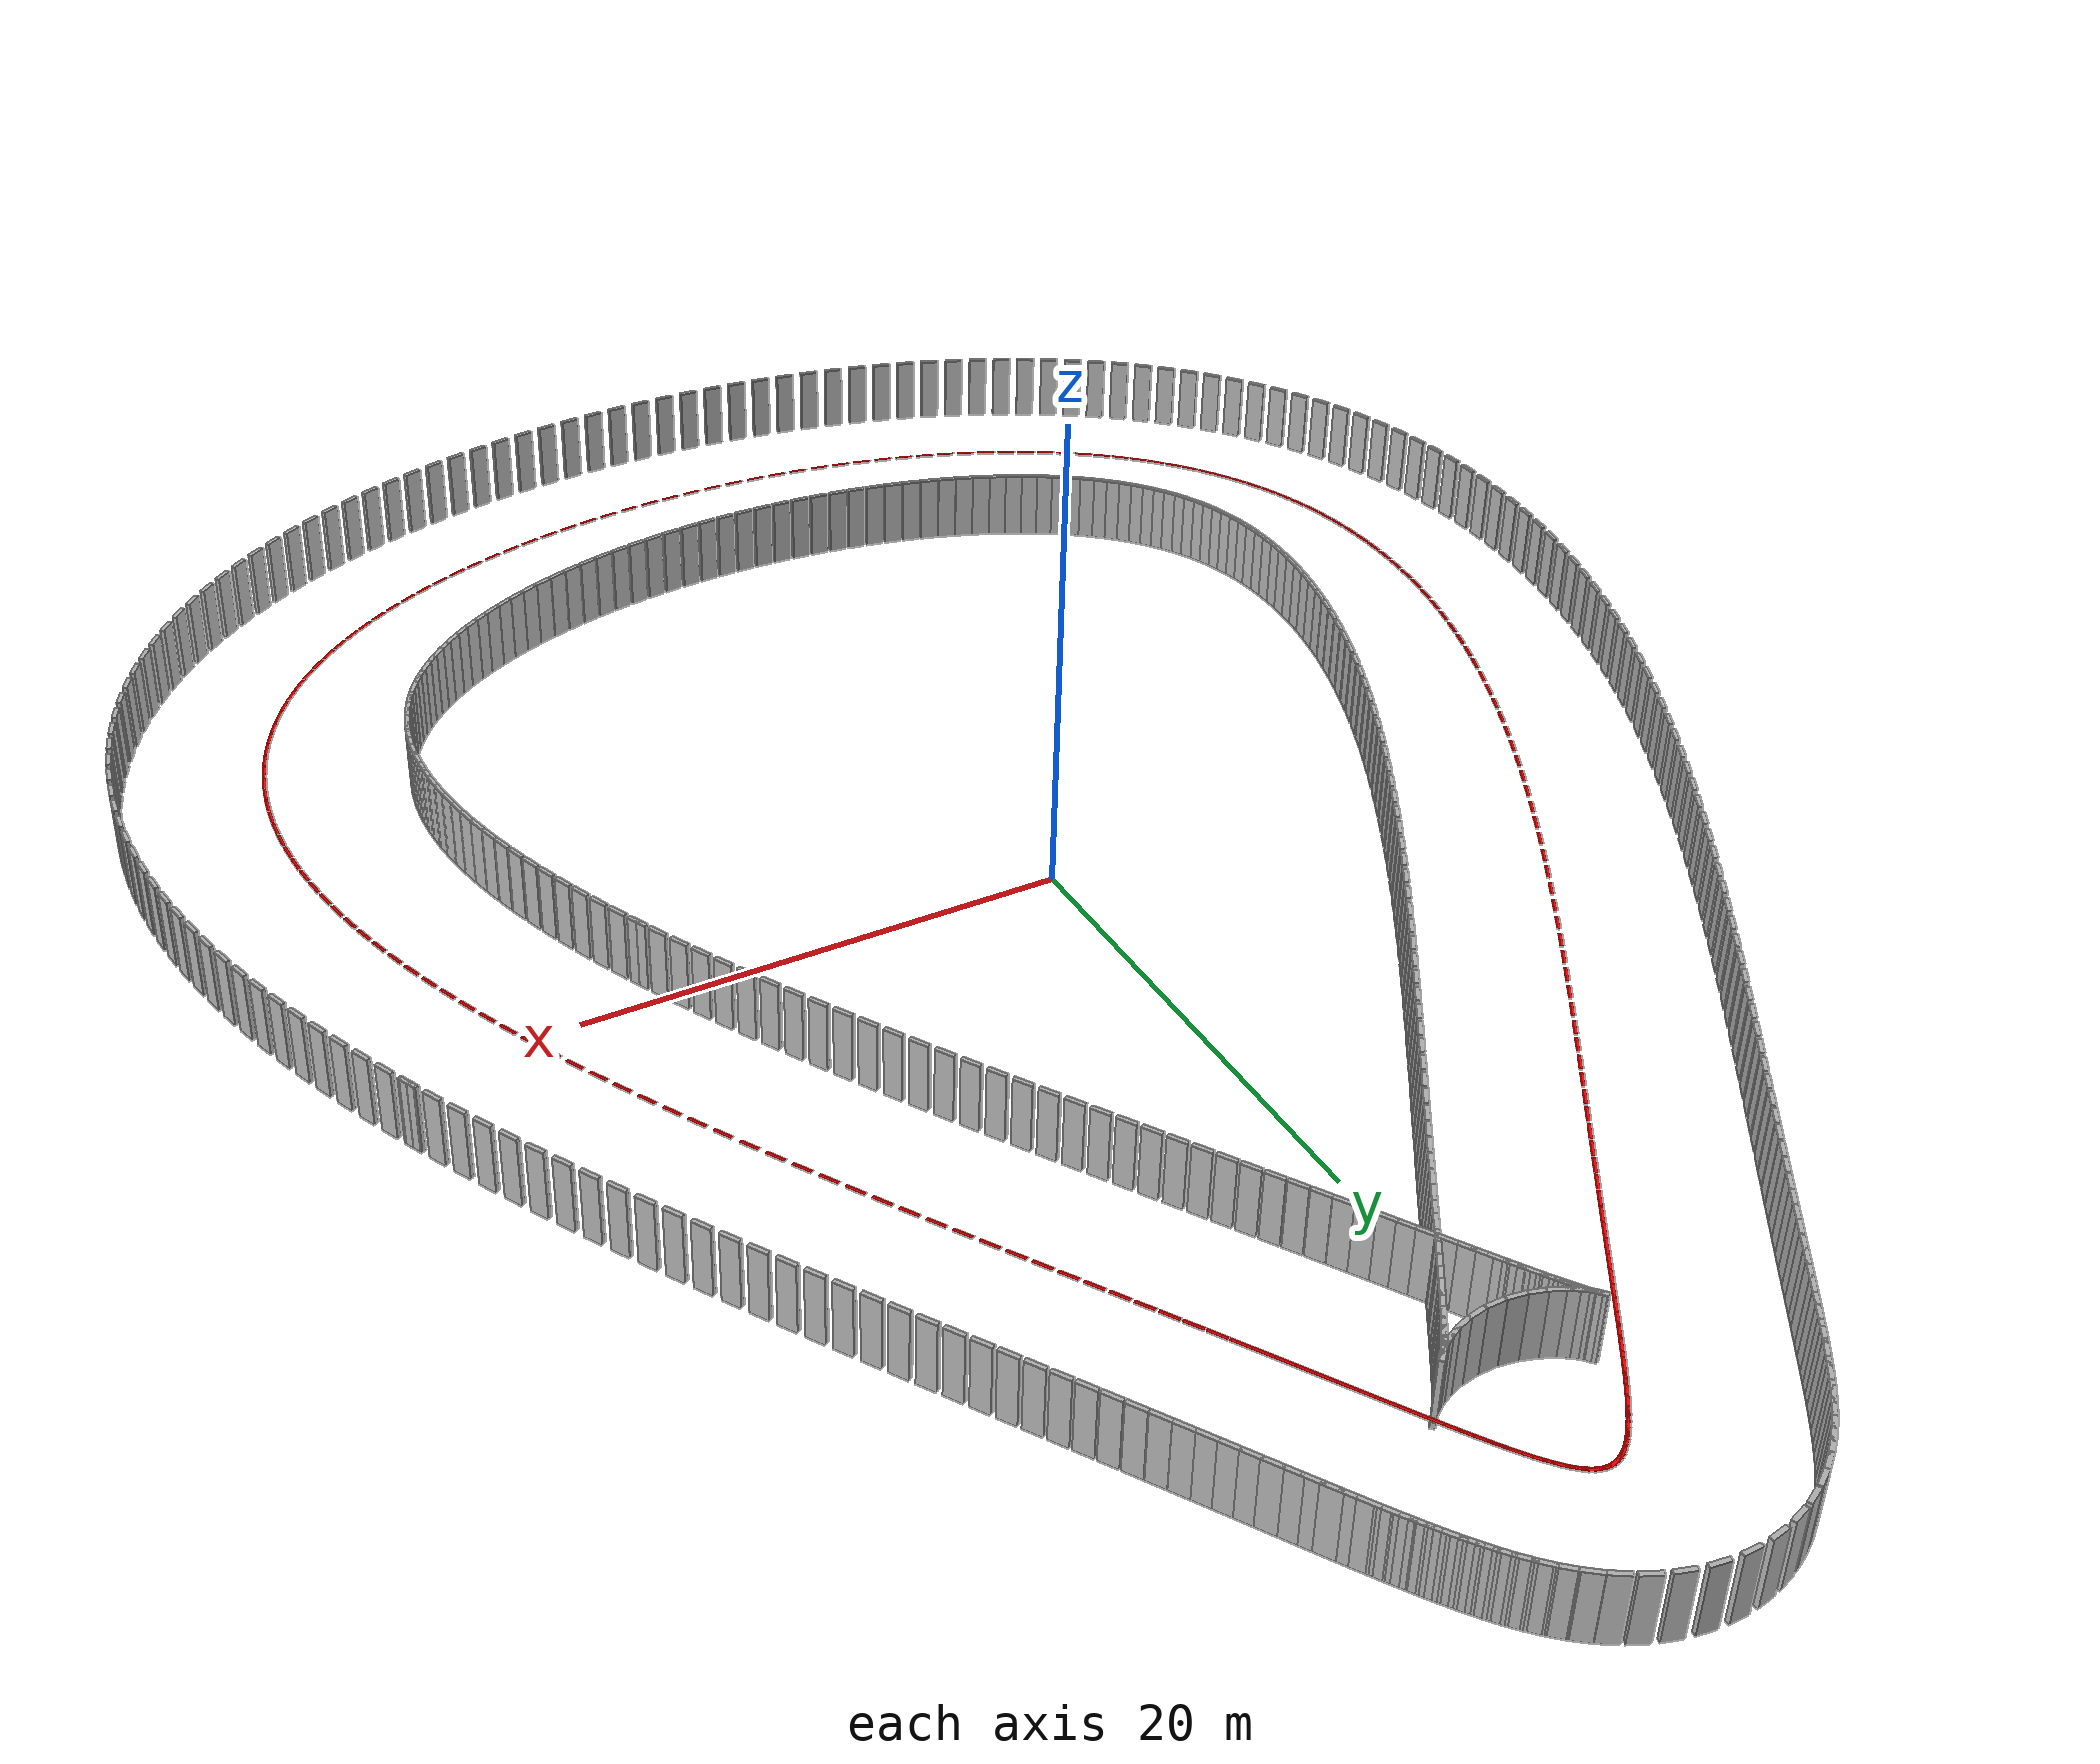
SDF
<?xml version="1.0" ?>
<sdf version="1.7">
<model name="track_walls">
<static>true</static>

    <link name="left_0">
      <pose>27.476 2.453 0.5 0 0 -1.150</pose>
      <collision name="c">
        <geometry>
          <box><size>0.8 0.2 3.0</size></box>
        </geometry>
      </collision>
      <visual name="v">
        <geometry>
          <box><size>0.8 0.2 3.0</size></box>
        </geometry>
      </visual>
    </link>

    <link name="right_0">
      <pose>16.524 -2.453 0.5 0 0 -1.150</pose>
      <collision name="c">
        <geometry>
          <box><size>0.8 0.2 3.0</size></box>
        </geometry>
      </collision>
      <visual name="v">
        <geometry>
          <box><size>0.8 0.2 3.0</size></box>
        </geometry>
      </visual>
    </link>

    <link name="center_0">
      <pose>22.000 -0.000 0.010 0 0 -1.150</pose>
      <visual name="v">
        <geometry>
          <box><size>0.8 0.15 0.02</size></box>
        </geometry>
        <material>
          <ambient>1 0 0 1</ambient>
          <diffuse>1 0 0 1</diffuse>
        </material>
      </visual>
    </link>

    <link name="left_1">
      <pose>27.945 1.405 0.5 0 0 -1.158</pose>
      <collision name="c">
        <geometry>
          <box><size>0.8 0.2 3.0</size></box>
        </geometry>
      </collision>
      <visual name="v">
        <geometry>
          <box><size>0.8 0.2 3.0</size></box>
        </geometry>
      </visual>
    </link>

    <link name="right_1">
      <pose>16.955 -3.413 0.5 0 0 -1.158</pose>
      <collision name="c">
        <geometry>
          <box><size>0.8 0.2 3.0</size></box>
        </geometry>
      </collision>
      <visual name="v">
        <geometry>
          <box><size>0.8 0.2 3.0</size></box>
        </geometry>
      </visual>
    </link>

    <link name="center_1">
      <pose>22.450 -1.004 0.010 0 0 -1.158</pose>
      <visual name="v">
        <geometry>
          <box><size>0.8 0.15 0.02</size></box>
        </geometry>
        <material>
          <ambient>1 0 0 1</ambient>
          <diffuse>1 0 0 1</diffuse>
        </material>
      </visual>
    </link>

    <link name="left_2">
      <pose>28.415 0.310 0.5 0 0 -1.174</pose>
      <collision name="c">
        <geometry>
          <box><size>0.8 0.2 3.0</size></box>
        </geometry>
      </collision>
      <visual name="v">
        <geometry>
          <box><size>0.8 0.2 3.0</size></box>
        </geometry>
      </visual>
    </link>

    <link name="right_2">
      <pose>17.345 -4.324 0.5 0 0 -1.174</pose>
      <collision name="c">
        <geometry>
          <box><size>0.8 0.2 3.0</size></box>
        </geometry>
      </collision>
      <visual name="v">
        <geometry>
          <box><size>0.8 0.2 3.0</size></box>
        </geometry>
      </visual>
    </link>

    <link name="center_2">
      <pose>22.880 -2.007 0.010 0 0 -1.174</pose>
      <visual name="v">
        <geometry>
          <box><size>0.8 0.15 0.02</size></box>
        </geometry>
        <material>
          <ambient>1 0 0 1</ambient>
          <diffuse>1 0 0 1</diffuse>
        </material>
      </visual>
    </link>

    <link name="left_3">
      <pose>28.864 -0.792 0.5 0 0 -1.192</pose>
      <collision name="c">
        <geometry>
          <box><size>0.8 0.2 3.0</size></box>
        </geometry>
      </collision>
      <visual name="v">
        <geometry>
          <box><size>0.8 0.2 3.0</size></box>
        </geometry>
      </visual>
    </link>

    <link name="right_3">
      <pose>17.714 -5.226 0.5 0 0 -1.192</pose>
      <collision name="c">
        <geometry>
          <box><size>0.8 0.2 3.0</size></box>
        </geometry>
      </collision>
      <visual name="v">
        <geometry>
          <box><size>0.8 0.2 3.0</size></box>
        </geometry>
      </visual>
    </link>

    <link name="center_3">
      <pose>23.289 -3.009 0.010 0 0 -1.192</pose>
      <visual name="v">
        <geometry>
          <box><size>0.8 0.15 0.02</size></box>
        </geometry>
        <material>
          <ambient>1 0 0 1</ambient>
          <diffuse>1 0 0 1</diffuse>
        </material>
      </visual>
    </link>

    <link name="left_4">
      <pose>29.293 -1.899 0.5 0 0 -1.212</pose>
      <collision name="c">
        <geometry>
          <box><size>0.8 0.2 3.0</size></box>
        </geometry>
      </collision>
      <visual name="v">
        <geometry>
          <box><size>0.8 0.2 3.0</size></box>
        </geometry>
      </visual>
    </link>

    <link name="right_4">
      <pose>18.058 -6.117 0.5 0 0 -1.212</pose>
      <collision name="c">
        <geometry>
          <box><size>0.8 0.2 3.0</size></box>
        </geometry>
      </collision>
      <visual name="v">
        <geometry>
          <box><size>0.8 0.2 3.0</size></box>
        </geometry>
      </visual>
    </link>

    <link name="center_4">
      <pose>23.675 -4.008 0.010 0 0 -1.212</pose>
      <visual name="v">
        <geometry>
          <box><size>0.8 0.15 0.02</size></box>
        </geometry>
        <material>
          <ambient>1 0 0 1</ambient>
          <diffuse>1 0 0 1</diffuse>
        </material>
      </visual>
    </link>

    <link name="left_5">
      <pose>29.697 -3.011 0.5 0 0 -1.232</pose>
      <collision name="c">
        <geometry>
          <box><size>0.8 0.2 3.0</size></box>
        </geometry>
      </collision>
      <visual name="v">
        <geometry>
          <box><size>0.8 0.2 3.0</size></box>
        </geometry>
      </visual>
    </link>

    <link name="right_5">
      <pose>18.378 -6.996 0.5 0 0 -1.232</pose>
      <collision name="c">
        <geometry>
          <box><size>0.8 0.2 3.0</size></box>
        </geometry>
      </collision>
      <visual name="v">
        <geometry>
          <box><size>0.8 0.2 3.0</size></box>
        </geometry>
      </visual>
    </link>

    <link name="center_5">
      <pose>24.038 -5.004 0.010 0 0 -1.232</pose>
      <visual name="v">
        <geometry>
          <box><size>0.8 0.15 0.02</size></box>
        </geometry>
        <material>
          <ambient>1 0 0 1</ambient>
          <diffuse>1 0 0 1</diffuse>
        </material>
      </visual>
    </link>

    <link name="left_6">
      <pose>30.077 -4.129 0.5 0 0 -1.254</pose>
      <collision name="c">
        <geometry>
          <box><size>0.8 0.2 3.0</size></box>
        </geometry>
      </collision>
      <visual name="v">
        <geometry>
          <box><size>0.8 0.2 3.0</size></box>
        </geometry>
      </visual>
    </link>

    <link name="right_6">
      <pose>18.673 -7.862 0.5 0 0 -1.254</pose>
      <collision name="c">
        <geometry>
          <box><size>0.8 0.2 3.0</size></box>
        </geometry>
      </collision>
      <visual name="v">
        <geometry>
          <box><size>0.8 0.2 3.0</size></box>
        </geometry>
      </visual>
    </link>

    <link name="center_6">
      <pose>24.375 -5.995 0.010 0 0 -1.254</pose>
      <visual name="v">
        <geometry>
          <box><size>0.8 0.15 0.02</size></box>
        </geometry>
        <material>
          <ambient>1 0 0 1</ambient>
          <diffuse>1 0 0 1</diffuse>
        </material>
      </visual>
    </link>

    <link name="left_7">
      <pose>30.430 -5.251 0.5 0 0 -1.278</pose>
      <collision name="c">
        <geometry>
          <box><size>0.8 0.2 3.0</size></box>
        </geometry>
      </collision>
      <visual name="v">
        <geometry>
          <box><size>0.8 0.2 3.0</size></box>
        </geometry>
      </visual>
    </link>

    <link name="right_7">
      <pose>18.940 -8.713 0.5 0 0 -1.278</pose>
      <collision name="c">
        <geometry>
          <box><size>0.8 0.2 3.0</size></box>
        </geometry>
      </collision>
      <visual name="v">
        <geometry>
          <box><size>0.8 0.2 3.0</size></box>
        </geometry>
      </visual>
    </link>

    <link name="center_7">
      <pose>24.685 -6.982 0.010 0 0 -1.278</pose>
      <visual name="v">
        <geometry>
          <box><size>0.8 0.15 0.02</size></box>
        </geometry>
        <material>
          <ambient>1 0 0 1</ambient>
          <diffuse>1 0 0 1</diffuse>
        </material>
      </visual>
    </link>

    <link name="left_8">
      <pose>30.755 -6.378 0.5 0 0 -1.304</pose>
      <collision name="c">
        <geometry>
          <box><size>0.8 0.2 3.0</size></box>
        </geometry>
      </collision>
      <visual name="v">
        <geometry>
          <box><size>0.8 0.2 3.0</size></box>
        </geometry>
      </visual>
    </link>

    <link name="right_8">
      <pose>19.181 -9.548 0.5 0 0 -1.304</pose>
      <collision name="c">
        <geometry>
          <box><size>0.8 0.2 3.0</size></box>
        </geometry>
      </collision>
      <visual name="v">
        <geometry>
          <box><size>0.8 0.2 3.0</size></box>
        </geometry>
      </visual>
    </link>

    <link name="center_8">
      <pose>24.968 -7.963 0.010 0 0 -1.304</pose>
      <visual name="v">
        <geometry>
          <box><size>0.8 0.15 0.02</size></box>
        </geometry>
        <material>
          <ambient>1 0 0 1</ambient>
          <diffuse>1 0 0 1</diffuse>
        </material>
      </visual>
    </link>

    <link name="left_9">
      <pose>31.049 -7.510 0.5 0 0 -1.331</pose>
      <collision name="c">
        <geometry>
          <box><size>0.8 0.2 3.0</size></box>
        </geometry>
      </collision>
      <visual name="v">
        <geometry>
          <box><size>0.8 0.2 3.0</size></box>
        </geometry>
      </visual>
    </link>

    <link name="right_9">
      <pose>19.393 -10.365 0.5 0 0 -1.331</pose>
      <collision name="c">
        <geometry>
          <box><size>0.8 0.2 3.0</size></box>
        </geometry>
      </collision>
      <visual name="v">
        <geometry>
          <box><size>0.8 0.2 3.0</size></box>
        </geometry>
      </visual>
    </link>

    <link name="center_9">
      <pose>25.221 -8.937 0.010 0 0 -1.331</pose>
      <visual name="v">
        <geometry>
          <box><size>0.8 0.15 0.02</size></box>
        </geometry>
        <material>
          <ambient>1 0 0 1</ambient>
          <diffuse>1 0 0 1</diffuse>
        </material>
      </visual>
    </link>

    <link name="left_10">
      <pose>31.310 -8.645 0.5 0 0 -1.359</pose>
      <collision name="c">
        <geometry>
          <box><size>0.8 0.2 3.0</size></box>
        </geometry>
      </collision>
      <visual name="v">
        <geometry>
          <box><size>0.8 0.2 3.0</size></box>
        </geometry>
      </visual>
    </link>

    <link name="right_10">
      <pose>19.577 -11.164 0.5 0 0 -1.359</pose>
      <collision name="c">
        <geometry>
          <box><size>0.8 0.2 3.0</size></box>
        </geometry>
      </collision>
      <visual name="v">
        <geometry>
          <box><size>0.8 0.2 3.0</size></box>
        </geometry>
      </visual>
    </link>

    <link name="center_10">
      <pose>25.443 -9.904 0.010 0 0 -1.359</pose>
      <visual name="v">
        <geometry>
          <box><size>0.8 0.15 0.02</size></box>
        </geometry>
        <material>
          <ambient>1 0 0 1</ambient>
          <diffuse>1 0 0 1</diffuse>
        </material>
      </visual>
    </link>

    <link name="left_11">
      <pose>31.536 -9.784 0.5 0 0 -1.390</pose>
      <collision name="c">
        <geometry>
          <box><size>0.8 0.2 3.0</size></box>
        </geometry>
      </collision>
      <visual name="v">
        <geometry>
          <box><size>0.8 0.2 3.0</size></box>
        </geometry>
      </visual>
    </link>

    <link name="right_11">
      <pose>19.732 -11.943 0.5 0 0 -1.390</pose>
      <collision name="c">
        <geometry>
          <box><size>0.8 0.2 3.0</size></box>
        </geometry>
      </collision>
      <visual name="v">
        <geometry>
          <box><size>0.8 0.2 3.0</size></box>
        </geometry>
      </visual>
    </link>

    <link name="center_11">
      <pose>25.634 -10.863 0.010 0 0 -1.390</pose>
      <visual name="v">
        <geometry>
          <box><size>0.8 0.15 0.02</size></box>
        </geometry>
        <material>
          <ambient>1 0 0 1</ambient>
          <diffuse>1 0 0 1</diffuse>
        </material>
      </visual>
    </link>

    <link name="left_12">
      <pose>31.727 -10.926 0.5 0 0 -1.422</pose>
      <collision name="c">
        <geometry>
          <box><size>0.8 0.2 3.0</size></box>
        </geometry>
      </collision>
      <visual name="v">
        <geometry>
          <box><size>0.8 0.2 3.0</size></box>
        </geometry>
      </visual>
    </link>

    <link name="right_12">
      <pose>19.858 -12.700 0.5 0 0 -1.422</pose>
      <collision name="c">
        <geometry>
          <box><size>0.8 0.2 3.0</size></box>
        </geometry>
      </collision>
      <visual name="v">
        <geometry>
          <box><size>0.8 0.2 3.0</size></box>
        </geometry>
      </visual>
    </link>

    <link name="center_12">
      <pose>25.792 -11.813 0.010 0 0 -1.422</pose>
      <visual name="v">
        <geometry>
          <box><size>0.8 0.15 0.02</size></box>
        </geometry>
        <material>
          <ambient>1 0 0 1</ambient>
          <diffuse>1 0 0 1</diffuse>
        </material>
      </visual>
    </link>

    <link name="left_13">
      <pose>31.878 -12.071 0.5 0 0 -1.457</pose>
      <collision name="c">
        <geometry>
          <box><size>0.8 0.2 3.0</size></box>
        </geometry>
      </collision>
      <visual name="v">
        <geometry>
          <box><size>0.8 0.2 3.0</size></box>
        </geometry>
      </visual>
    </link>

    <link name="right_13">
      <pose>19.956 -13.436 0.5 0 0 -1.457</pose>
      <collision name="c">
        <geometry>
          <box><size>0.8 0.2 3.0</size></box>
        </geometry>
      </collision>
      <visual name="v">
        <geometry>
          <box><size>0.8 0.2 3.0</size></box>
        </geometry>
      </visual>
    </link>

    <link name="center_13">
      <pose>25.917 -12.754 0.010 0 0 -1.457</pose>
      <visual name="v">
        <geometry>
          <box><size>0.8 0.15 0.02</size></box>
        </geometry>
        <material>
          <ambient>1 0 0 1</ambient>
          <diffuse>1 0 0 1</diffuse>
        </material>
      </visual>
    </link>

    <link name="left_14">
      <pose>31.988 -13.218 0.5 0 0 -1.493</pose>
      <collision name="c">
        <geometry>
          <box><size>0.8 0.2 3.0</size></box>
        </geometry>
      </collision>
      <visual name="v">
        <geometry>
          <box><size>0.8 0.2 3.0</size></box>
        </geometry>
      </visual>
    </link>

    <link name="right_14">
      <pose>20.024 -14.148 0.5 0 0 -1.493</pose>
      <collision name="c">
        <geometry>
          <box><size>0.8 0.2 3.0</size></box>
        </geometry>
      </collision>
      <visual name="v">
        <geometry>
          <box><size>0.8 0.2 3.0</size></box>
        </geometry>
      </visual>
    </link>

    <link name="center_14">
      <pose>26.006 -13.683 0.010 0 0 -1.493</pose>
      <visual name="v">
        <geometry>
          <box><size>0.8 0.15 0.02</size></box>
        </geometry>
        <material>
          <ambient>1 0 0 1</ambient>
          <diffuse>1 0 0 1</diffuse>
        </material>
      </visual>
    </link>

    <link name="left_15">
      <pose>32.056 -14.367 0.5 0 0 -1.532</pose>
      <collision name="c">
        <geometry>
          <box><size>0.8 0.2 3.0</size></box>
        </geometry>
      </collision>
      <visual name="v">
        <geometry>
          <box><size>0.8 0.2 3.0</size></box>
        </geometry>
      </visual>
    </link>

    <link name="right_15">
      <pose>20.065 -14.837 0.5 0 0 -1.532</pose>
      <collision name="c">
        <geometry>
          <box><size>0.8 0.2 3.0</size></box>
        </geometry>
      </collision>
      <visual name="v">
        <geometry>
          <box><size>0.8 0.2 3.0</size></box>
        </geometry>
      </visual>
    </link>

    <link name="center_15">
      <pose>26.060 -14.602 0.010 0 0 -1.532</pose>
      <visual name="v">
        <geometry>
          <box><size>0.8 0.15 0.02</size></box>
        </geometry>
        <material>
          <ambient>1 0 0 1</ambient>
          <diffuse>1 0 0 1</diffuse>
        </material>
      </visual>
    </link>

    <link name="left_16">
      <pose>32.078 -15.515 0.5 0 0 -1.572</pose>
      <collision name="c">
        <geometry>
          <box><size>0.8 0.2 3.0</size></box>
        </geometry>
      </collision>
      <visual name="v">
        <geometry>
          <box><size>0.8 0.2 3.0</size></box>
        </geometry>
      </visual>
    </link>

    <link name="right_16">
      <pose>20.078 -15.502 0.5 0 0 -1.572</pose>
      <collision name="c">
        <geometry>
          <box><size>0.8 0.2 3.0</size></box>
        </geometry>
      </collision>
      <visual name="v">
        <geometry>
          <box><size>0.8 0.2 3.0</size></box>
        </geometry>
      </visual>
    </link>

    <link name="center_16">
      <pose>26.078 -15.508 0.010 0 0 -1.572</pose>
      <visual name="v">
        <geometry>
          <box><size>0.8 0.15 0.02</size></box>
        </geometry>
        <material>
          <ambient>1 0 0 1</ambient>
          <diffuse>1 0 0 1</diffuse>
        </material>
      </visual>
    </link>

    <link name="left_17">
      <pose>32.053 -16.662 0.5 0 0 -1.614</pose>
      <collision name="c">
        <geometry>
          <box><size>0.8 0.2 3.0</size></box>
        </geometry>
      </collision>
      <visual name="v">
        <geometry>
          <box><size>0.8 0.2 3.0</size></box>
        </geometry>
      </visual>
    </link>

    <link name="right_17">
      <pose>20.064 -16.142 0.5 0 0 -1.614</pose>
      <collision name="c">
        <geometry>
          <box><size>0.8 0.2 3.0</size></box>
        </geometry>
      </collision>
      <visual name="v">
        <geometry>
          <box><size>0.8 0.2 3.0</size></box>
        </geometry>
      </visual>
    </link>

    <link name="center_17">
      <pose>26.058 -16.402 0.010 0 0 -1.614</pose>
      <visual name="v">
        <geometry>
          <box><size>0.8 0.15 0.02</size></box>
        </geometry>
        <material>
          <ambient>1 0 0 1</ambient>
          <diffuse>1 0 0 1</diffuse>
        </material>
      </visual>
    </link>

    <link name="left_18">
      <pose>31.978 -17.806 0.5 0 0 -1.658</pose>
      <collision name="c">
        <geometry>
          <box><size>0.8 0.2 3.0</size></box>
        </geometry>
      </collision>
      <visual name="v">
        <geometry>
          <box><size>0.8 0.2 3.0</size></box>
        </geometry>
      </visual>
    </link>

    <link name="right_18">
      <pose>20.024 -16.758 0.5 0 0 -1.658</pose>
      <collision name="c">
        <geometry>
          <box><size>0.8 0.2 3.0</size></box>
        </geometry>
      </collision>
      <visual name="v">
        <geometry>
          <box><size>0.8 0.2 3.0</size></box>
        </geometry>
      </visual>
    </link>

    <link name="center_18">
      <pose>26.001 -17.282 0.010 0 0 -1.658</pose>
      <visual name="v">
        <geometry>
          <box><size>0.8 0.15 0.02</size></box>
        </geometry>
        <material>
          <ambient>1 0 0 1</ambient>
          <diffuse>1 0 0 1</diffuse>
        </material>
      </visual>
    </link>

    <link name="left_19">
      <pose>31.852 -18.946 0.5 0 0 -1.704</pose>
      <collision name="c">
        <geometry>
          <box><size>0.8 0.2 3.0</size></box>
        </geometry>
      </collision>
      <visual name="v">
        <geometry>
          <box><size>0.8 0.2 3.0</size></box>
        </geometry>
      </visual>
    </link>

    <link name="right_19">
      <pose>19.959 -17.351 0.5 0 0 -1.704</pose>
      <collision name="c">
        <geometry>
          <box><size>0.8 0.2 3.0</size></box>
        </geometry>
      </collision>
      <visual name="v">
        <geometry>
          <box><size>0.8 0.2 3.0</size></box>
        </geometry>
      </visual>
    </link>

    <link name="center_19">
      <pose>25.905 -18.148 0.010 0 0 -1.704</pose>
      <visual name="v">
        <geometry>
          <box><size>0.8 0.15 0.02</size></box>
        </geometry>
        <material>
          <ambient>1 0 0 1</ambient>
          <diffuse>1 0 0 1</diffuse>
        </material>
      </visual>
    </link>

    <link name="left_20">
      <pose>31.673 -20.078 0.5 0 0 -1.752</pose>
      <collision name="c">
        <geometry>
          <box><size>0.8 0.2 3.0</size></box>
        </geometry>
      </collision>
      <visual name="v">
        <geometry>
          <box><size>0.8 0.2 3.0</size></box>
        </geometry>
      </visual>
    </link>

    <link name="right_20">
      <pose>19.869 -17.920 0.5 0 0 -1.752</pose>
      <collision name="c">
        <geometry>
          <box><size>0.8 0.2 3.0</size></box>
        </geometry>
      </collision>
      <visual name="v">
        <geometry>
          <box><size>0.8 0.2 3.0</size></box>
        </geometry>
      </visual>
    </link>

    <link name="center_20">
      <pose>25.771 -18.999 0.010 0 0 -1.752</pose>
      <visual name="v">
        <geometry>
          <box><size>0.8 0.15 0.02</size></box>
        </geometry>
        <material>
          <ambient>1 0 0 1</ambient>
          <diffuse>1 0 0 1</diffuse>
        </material>
      </visual>
    </link>

    <link name="left_21">
      <pose>31.439 -21.201 0.5 0 0 -1.801</pose>
      <collision name="c">
        <geometry>
          <box><size>0.8 0.2 3.0</size></box>
        </geometry>
      </collision>
      <visual name="v">
        <geometry>
          <box><size>0.8 0.2 3.0</size></box>
        </geometry>
      </visual>
    </link>

    <link name="right_21">
      <pose>19.755 -18.468 0.5 0 0 -1.801</pose>
      <collision name="c">
        <geometry>
          <box><size>0.8 0.2 3.0</size></box>
        </geometry>
      </collision>
      <visual name="v">
        <geometry>
          <box><size>0.8 0.2 3.0</size></box>
        </geometry>
      </visual>
    </link>

    <link name="center_21">
      <pose>25.597 -19.835 0.010 0 0 -1.801</pose>
      <visual name="v">
        <geometry>
          <box><size>0.8 0.15 0.02</size></box>
        </geometry>
        <material>
          <ambient>1 0 0 1</ambient>
          <diffuse>1 0 0 1</diffuse>
        </material>
      </visual>
    </link>

    <link name="left_22">
      <pose>31.150 -22.312 0.5 0 0 -1.851</pose>
      <collision name="c">
        <geometry>
          <box><size>0.8 0.2 3.0</size></box>
        </geometry>
      </collision>
      <visual name="v">
        <geometry>
          <box><size>0.8 0.2 3.0</size></box>
        </geometry>
      </visual>
    </link>

    <link name="right_22">
      <pose>19.617 -18.995 0.5 0 0 -1.851</pose>
      <collision name="c">
        <geometry>
          <box><size>0.8 0.2 3.0</size></box>
        </geometry>
      </collision>
      <visual name="v">
        <geometry>
          <box><size>0.8 0.2 3.0</size></box>
        </geometry>
      </visual>
    </link>

    <link name="center_22">
      <pose>25.384 -20.654 0.010 0 0 -1.851</pose>
      <visual name="v">
        <geometry>
          <box><size>0.8 0.15 0.02</size></box>
        </geometry>
        <material>
          <ambient>1 0 0 1</ambient>
          <diffuse>1 0 0 1</diffuse>
        </material>
      </visual>
    </link>

    <link name="left_23">
      <pose>30.804 -23.408 0.5 0 0 -1.902</pose>
      <collision name="c">
        <geometry>
          <box><size>0.8 0.2 3.0</size></box>
        </geometry>
      </collision>
      <visual name="v">
        <geometry>
          <box><size>0.8 0.2 3.0</size></box>
        </geometry>
      </visual>
    </link>

    <link name="right_23">
      <pose>19.457 -19.504 0.5 0 0 -1.902</pose>
      <collision name="c">
        <geometry>
          <box><size>0.8 0.2 3.0</size></box>
        </geometry>
      </collision>
      <visual name="v">
        <geometry>
          <box><size>0.8 0.2 3.0</size></box>
        </geometry>
      </visual>
    </link>

    <link name="center_23">
      <pose>25.131 -21.456 0.010 0 0 -1.902</pose>
      <visual name="v">
        <geometry>
          <box><size>0.8 0.15 0.02</size></box>
        </geometry>
        <material>
          <ambient>1 0 0 1</ambient>
          <diffuse>1 0 0 1</diffuse>
        </material>
      </visual>
    </link>

    <link name="left_24">
      <pose>30.402 -24.485 0.5 0 0 -1.954</pose>
      <collision name="c">
        <geometry>
          <box><size>0.8 0.2 3.0</size></box>
        </geometry>
      </collision>
      <visual name="v">
        <geometry>
          <box><size>0.8 0.2 3.0</size></box>
        </geometry>
      </visual>
    </link>

    <link name="right_24">
      <pose>19.274 -19.996 0.5 0 0 -1.954</pose>
      <collision name="c">
        <geometry>
          <box><size>0.8 0.2 3.0</size></box>
        </geometry>
      </collision>
      <visual name="v">
        <geometry>
          <box><size>0.8 0.2 3.0</size></box>
        </geometry>
      </visual>
    </link>

    <link name="center_24">
      <pose>24.838 -22.240 0.010 0 0 -1.954</pose>
      <visual name="v">
        <geometry>
          <box><size>0.8 0.15 0.02</size></box>
        </geometry>
        <material>
          <ambient>1 0 0 1</ambient>
          <diffuse>1 0 0 1</diffuse>
        </material>
      </visual>
    </link>

    <link name="left_25">
      <pose>29.944 -25.540 0.5 0 0 -2.007</pose>
      <collision name="c">
        <geometry>
          <box><size>0.8 0.2 3.0</size></box>
        </geometry>
      </collision>
      <visual name="v">
        <geometry>
          <box><size>0.8 0.2 3.0</size></box>
        </geometry>
      </visual>
    </link>

    <link name="right_25">
      <pose>19.067 -20.472 0.5 0 0 -2.007</pose>
      <collision name="c">
        <geometry>
          <box><size>0.8 0.2 3.0</size></box>
        </geometry>
      </collision>
      <visual name="v">
        <geometry>
          <box><size>0.8 0.2 3.0</size></box>
        </geometry>
      </visual>
    </link>

    <link name="center_25">
      <pose>24.505 -23.006 0.010 0 0 -2.007</pose>
      <visual name="v">
        <geometry>
          <box><size>0.8 0.15 0.02</size></box>
        </geometry>
        <material>
          <ambient>1 0 0 1</ambient>
          <diffuse>1 0 0 1</diffuse>
        </material>
      </visual>
    </link>

    <link name="left_26">
      <pose>29.430 -26.571 0.5 0 0 -2.060</pose>
      <collision name="c">
        <geometry>
          <box><size>0.8 0.2 3.0</size></box>
        </geometry>
      </collision>
      <visual name="v">
        <geometry>
          <box><size>0.8 0.2 3.0</size></box>
        </geometry>
      </visual>
    </link>

    <link name="right_26">
      <pose>18.835 -20.936 0.5 0 0 -2.060</pose>
      <collision name="c">
        <geometry>
          <box><size>0.8 0.2 3.0</size></box>
        </geometry>
      </collision>
      <visual name="v">
        <geometry>
          <box><size>0.8 0.2 3.0</size></box>
        </geometry>
      </visual>
    </link>

    <link name="center_26">
      <pose>24.133 -23.753 0.010 0 0 -2.060</pose>
      <visual name="v">
        <geometry>
          <box><size>0.8 0.15 0.02</size></box>
        </geometry>
        <material>
          <ambient>1 0 0 1</ambient>
          <diffuse>1 0 0 1</diffuse>
        </material>
      </visual>
    </link>

    <link name="left_27">
      <pose>28.863 -27.573 0.5 0 0 -2.112</pose>
      <collision name="c">
        <geometry>
          <box><size>0.8 0.2 3.0</size></box>
        </geometry>
      </collision>
      <visual name="v">
        <geometry>
          <box><size>0.8 0.2 3.0</size></box>
        </geometry>
      </visual>
    </link>

    <link name="right_27">
      <pose>18.579 -21.389 0.5 0 0 -2.112</pose>
      <collision name="c">
        <geometry>
          <box><size>0.8 0.2 3.0</size></box>
        </geometry>
      </collision>
      <visual name="v">
        <geometry>
          <box><size>0.8 0.2 3.0</size></box>
        </geometry>
      </visual>
    </link>

    <link name="center_27">
      <pose>23.721 -24.481 0.010 0 0 -2.112</pose>
      <visual name="v">
        <geometry>
          <box><size>0.8 0.15 0.02</size></box>
        </geometry>
        <material>
          <ambient>1 0 0 1</ambient>
          <diffuse>1 0 0 1</diffuse>
        </material>
      </visual>
    </link>

    <link name="left_28">
      <pose>28.243 -28.546 0.5 0 0 -2.165</pose>
      <collision name="c">
        <geometry>
          <box><size>0.8 0.2 3.0</size></box>
        </geometry>
      </collision>
      <visual name="v">
        <geometry>
          <box><size>0.8 0.2 3.0</size></box>
        </geometry>
      </visual>
    </link>

    <link name="right_28">
      <pose>18.297 -21.831 0.5 0 0 -2.165</pose>
      <collision name="c">
        <geometry>
          <box><size>0.8 0.2 3.0</size></box>
        </geometry>
      </collision>
      <visual name="v">
        <geometry>
          <box><size>0.8 0.2 3.0</size></box>
        </geometry>
      </visual>
    </link>

    <link name="center_28">
      <pose>23.270 -25.189 0.010 0 0 -2.165</pose>
      <visual name="v">
        <geometry>
          <box><size>0.8 0.15 0.02</size></box>
        </geometry>
        <material>
          <ambient>1 0 0 1</ambient>
          <diffuse>1 0 0 1</diffuse>
        </material>
      </visual>
    </link>

    <link name="left_29">
      <pose>27.572 -29.485 0.5 0 0 -2.216</pose>
      <collision name="c">
        <geometry>
          <box><size>0.8 0.2 3.0</size></box>
        </geometry>
      </collision>
      <visual name="v">
        <geometry>
          <box><size>0.8 0.2 3.0</size></box>
        </geometry>
      </visual>
    </link>

    <link name="right_29">
      <pose>17.987 -22.265 0.5 0 0 -2.216</pose>
      <collision name="c">
        <geometry>
          <box><size>0.8 0.2 3.0</size></box>
        </geometry>
      </collision>
      <visual name="v">
        <geometry>
          <box><size>0.8 0.2 3.0</size></box>
        </geometry>
      </visual>
    </link>

    <link name="center_29">
      <pose>22.780 -25.875 0.010 0 0 -2.216</pose>
      <visual name="v">
        <geometry>
          <box><size>0.8 0.15 0.02</size></box>
        </geometry>
        <material>
          <ambient>1 0 0 1</ambient>
          <diffuse>1 0 0 1</diffuse>
        </material>
      </visual>
    </link>

    <link name="left_30">
      <pose>26.854 -30.390 0.5 0 0 -2.267</pose>
      <collision name="c">
        <geometry>
          <box><size>0.8 0.2 3.0</size></box>
        </geometry>
      </collision>
      <visual name="v">
        <geometry>
          <box><size>0.8 0.2 3.0</size></box>
        </geometry>
      </visual>
    </link>

    <link name="right_30">
      <pose>17.649 -22.691 0.5 0 0 -2.267</pose>
      <collision name="c">
        <geometry>
          <box><size>0.8 0.2 3.0</size></box>
        </geometry>
      </collision>
      <visual name="v">
        <geometry>
          <box><size>0.8 0.2 3.0</size></box>
        </geometry>
      </visual>
    </link>

    <link name="center_30">
      <pose>22.251 -26.541 0.010 0 0 -2.267</pose>
      <visual name="v">
        <geometry>
          <box><size>0.8 0.15 0.02</size></box>
        </geometry>
        <material>
          <ambient>1 0 0 1</ambient>
          <diffuse>1 0 0 1</diffuse>
        </material>
      </visual>
    </link>

    <link name="left_31">
      <pose>26.090 -31.258 0.5 0 0 -2.317</pose>
      <collision name="c">
        <geometry>
          <box><size>0.8 0.2 3.0</size></box>
        </geometry>
      </collision>
      <visual name="v">
        <geometry>
          <box><size>0.8 0.2 3.0</size></box>
        </geometry>
      </visual>
    </link>

    <link name="right_31">
      <pose>17.280 -23.110 0.5 0 0 -2.317</pose>
      <collision name="c">
        <geometry>
          <box><size>0.8 0.2 3.0</size></box>
        </geometry>
      </collision>
      <visual name="v">
        <geometry>
          <box><size>0.8 0.2 3.0</size></box>
        </geometry>
      </visual>
    </link>

    <link name="center_31">
      <pose>21.685 -27.184 0.010 0 0 -2.317</pose>
      <visual name="v">
        <geometry>
          <box><size>0.8 0.15 0.02</size></box>
        </geometry>
        <material>
          <ambient>1 0 0 1</ambient>
          <diffuse>1 0 0 1</diffuse>
        </material>
      </visual>
    </link>

    <link name="left_32">
      <pose>25.283 -32.089 0.5 0 0 -2.366</pose>
      <collision name="c">
        <geometry>
          <box><size>0.8 0.2 3.0</size></box>
        </geometry>
      </collision>
      <visual name="v">
        <geometry>
          <box><size>0.8 0.2 3.0</size></box>
        </geometry>
      </visual>
    </link>

    <link name="right_32">
      <pose>16.880 -23.522 0.5 0 0 -2.366</pose>
      <collision name="c">
        <geometry>
          <box><size>0.8 0.2 3.0</size></box>
        </geometry>
      </collision>
      <visual name="v">
        <geometry>
          <box><size>0.8 0.2 3.0</size></box>
        </geometry>
      </visual>
    </link>

    <link name="center_32">
      <pose>21.081 -27.806 0.010 0 0 -2.366</pose>
      <visual name="v">
        <geometry>
          <box><size>0.8 0.15 0.02</size></box>
        </geometry>
        <material>
          <ambient>1 0 0 1</ambient>
          <diffuse>1 0 0 1</diffuse>
        </material>
      </visual>
    </link>

    <link name="left_33">
      <pose>24.435 -32.881 0.5 0 0 -2.413</pose>
      <collision name="c">
        <geometry>
          <box><size>0.8 0.2 3.0</size></box>
        </geometry>
      </collision>
      <visual name="v">
        <geometry>
          <box><size>0.8 0.2 3.0</size></box>
        </geometry>
      </visual>
    </link>

    <link name="right_33">
      <pose>16.448 -23.926 0.5 0 0 -2.413</pose>
      <collision name="c">
        <geometry>
          <box><size>0.8 0.2 3.0</size></box>
        </geometry>
      </collision>
      <visual name="v">
        <geometry>
          <box><size>0.8 0.2 3.0</size></box>
        </geometry>
      </visual>
    </link>

    <link name="center_33">
      <pose>20.441 -28.404 0.010 0 0 -2.413</pose>
      <visual name="v">
        <geometry>
          <box><size>0.8 0.15 0.02</size></box>
        </geometry>
        <material>
          <ambient>1 0 0 1</ambient>
          <diffuse>1 0 0 1</diffuse>
        </material>
      </visual>
    </link>

    <link name="left_34">
      <pose>23.550 -33.635 0.5 0 0 -2.459</pose>
      <collision name="c">
        <geometry>
          <box><size>0.8 0.2 3.0</size></box>
        </geometry>
      </collision>
      <visual name="v">
        <geometry>
          <box><size>0.8 0.2 3.0</size></box>
        </geometry>
      </visual>
    </link>

    <link name="right_34">
      <pose>15.982 -24.323 0.5 0 0 -2.459</pose>
      <collision name="c">
        <geometry>
          <box><size>0.8 0.2 3.0</size></box>
        </geometry>
      </collision>
      <visual name="v">
        <geometry>
          <box><size>0.8 0.2 3.0</size></box>
        </geometry>
      </visual>
    </link>

    <link name="center_34">
      <pose>19.766 -28.979 0.010 0 0 -2.459</pose>
      <visual name="v">
        <geometry>
          <box><size>0.8 0.15 0.02</size></box>
        </geometry>
        <material>
          <ambient>1 0 0 1</ambient>
          <diffuse>1 0 0 1</diffuse>
        </material>
      </visual>
    </link>

    <link name="left_35">
      <pose>22.630 -34.350 0.5 0 0 -2.504</pose>
      <collision name="c">
        <geometry>
          <box><size>0.8 0.2 3.0</size></box>
        </geometry>
      </collision>
      <visual name="v">
        <geometry>
          <box><size>0.8 0.2 3.0</size></box>
        </geometry>
      </visual>
    </link>

    <link name="right_35">
      <pose>15.482 -24.710 0.5 0 0 -2.504</pose>
      <collision name="c">
        <geometry>
          <box><size>0.8 0.2 3.0</size></box>
        </geometry>
      </collision>
      <visual name="v">
        <geometry>
          <box><size>0.8 0.2 3.0</size></box>
        </geometry>
      </visual>
    </link>

    <link name="center_35">
      <pose>19.056 -29.530 0.010 0 0 -2.504</pose>
      <visual name="v">
        <geometry>
          <box><size>0.8 0.15 0.02</size></box>
        </geometry>
        <material>
          <ambient>1 0 0 1</ambient>
          <diffuse>1 0 0 1</diffuse>
        </material>
      </visual>
    </link>

    <link name="left_36">
      <pose>21.676 -35.025 0.5 0 0 -2.546</pose>
      <collision name="c">
        <geometry>
          <box><size>0.8 0.2 3.0</size></box>
        </geometry>
      </collision>
      <visual name="v">
        <geometry>
          <box><size>0.8 0.2 3.0</size></box>
        </geometry>
      </visual>
    </link>

    <link name="right_36">
      <pose>14.949 -25.088 0.5 0 0 -2.546</pose>
      <collision name="c">
        <geometry>
          <box><size>0.8 0.2 3.0</size></box>
        </geometry>
      </collision>
      <visual name="v">
        <geometry>
          <box><size>0.8 0.2 3.0</size></box>
        </geometry>
      </visual>
    </link>

    <link name="center_36">
      <pose>18.312 -30.057 0.010 0 0 -2.546</pose>
      <visual name="v">
        <geometry>
          <box><size>0.8 0.15 0.02</size></box>
        </geometry>
        <material>
          <ambient>1 0 0 1</ambient>
          <diffuse>1 0 0 1</diffuse>
        </material>
      </visual>
    </link>

    <link name="left_37">
      <pose>20.691 -35.662 0.5 0 0 -2.588</pose>
      <collision name="c">
        <geometry>
          <box><size>0.8 0.2 3.0</size></box>
        </geometry>
      </collision>
      <visual name="v">
        <geometry>
          <box><size>0.8 0.2 3.0</size></box>
        </geometry>
      </visual>
    </link>

    <link name="right_37">
      <pose>14.381 -25.455 0.5 0 0 -2.588</pose>
      <collision name="c">
        <geometry>
          <box><size>0.8 0.2 3.0</size></box>
        </geometry>
      </collision>
      <visual name="v">
        <geometry>
          <box><size>0.8 0.2 3.0</size></box>
        </geometry>
      </visual>
    </link>

    <link name="center_37">
      <pose>17.536 -30.559 0.010 0 0 -2.588</pose>
      <visual name="v">
        <geometry>
          <box><size>0.8 0.15 0.02</size></box>
        </geometry>
        <material>
          <ambient>1 0 0 1</ambient>
          <diffuse>1 0 0 1</diffuse>
        </material>
      </visual>
    </link>

    <link name="left_38">
      <pose>19.678 -36.261 0.5 0 0 -2.628</pose>
      <collision name="c">
        <geometry>
          <box><size>0.8 0.2 3.0</size></box>
        </geometry>
      </collision>
      <visual name="v">
        <geometry>
          <box><size>0.8 0.2 3.0</size></box>
        </geometry>
      </visual>
    </link>

    <link name="right_38">
      <pose>13.780 -25.811 0.5 0 0 -2.628</pose>
      <collision name="c">
        <geometry>
          <box><size>0.8 0.2 3.0</size></box>
        </geometry>
      </collision>
      <visual name="v">
        <geometry>
          <box><size>0.8 0.2 3.0</size></box>
        </geometry>
      </visual>
    </link>

    <link name="center_38">
      <pose>16.729 -31.036 0.010 0 0 -2.628</pose>
      <visual name="v">
        <geometry>
          <box><size>0.8 0.15 0.02</size></box>
        </geometry>
        <material>
          <ambient>1 0 0 1</ambient>
          <diffuse>1 0 0 1</diffuse>
        </material>
      </visual>
    </link>

    <link name="left_39">
      <pose>18.638 -36.822 0.5 0 0 -2.666</pose>
      <collision name="c">
        <geometry>
          <box><size>0.8 0.2 3.0</size></box>
        </geometry>
      </collision>
      <visual name="v">
        <geometry>
          <box><size>0.8 0.2 3.0</size></box>
        </geometry>
      </visual>
    </link>

    <link name="right_39">
      <pose>13.145 -26.152 0.5 0 0 -2.666</pose>
      <collision name="c">
        <geometry>
          <box><size>0.8 0.2 3.0</size></box>
        </geometry>
      </collision>
      <visual name="v">
        <geometry>
          <box><size>0.8 0.2 3.0</size></box>
        </geometry>
      </visual>
    </link>

    <link name="center_39">
      <pose>15.892 -31.487 0.010 0 0 -2.666</pose>
      <visual name="v">
        <geometry>
          <box><size>0.8 0.15 0.02</size></box>
        </geometry>
        <material>
          <ambient>1 0 0 1</ambient>
          <diffuse>1 0 0 1</diffuse>
        </material>
      </visual>
    </link>

    <link name="left_40">
      <pose>17.573 -37.345 0.5 0 0 -2.703</pose>
      <collision name="c">
        <geometry>
          <box><size>0.8 0.2 3.0</size></box>
        </geometry>
      </collision>
      <visual name="v">
        <geometry>
          <box><size>0.8 0.2 3.0</size></box>
        </geometry>
      </visual>
    </link>

    <link name="right_40">
      <pose>12.479 -26.480 0.5 0 0 -2.703</pose>
      <collision name="c">
        <geometry>
          <box><size>0.8 0.2 3.0</size></box>
        </geometry>
      </collision>
      <visual name="v">
        <geometry>
          <box><size>0.8 0.2 3.0</size></box>
        </geometry>
      </visual>
    </link>

    <link name="center_40">
      <pose>15.026 -31.913 0.010 0 0 -2.703</pose>
      <visual name="v">
        <geometry>
          <box><size>0.8 0.15 0.02</size></box>
        </geometry>
        <material>
          <ambient>1 0 0 1</ambient>
          <diffuse>1 0 0 1</diffuse>
        </material>
      </visual>
    </link>

    <link name="left_41">
      <pose>16.484 -37.832 0.5 0 0 -2.739</pose>
      <collision name="c">
        <geometry>
          <box><size>0.8 0.2 3.0</size></box>
        </geometry>
      </collision>
      <visual name="v">
        <geometry>
          <box><size>0.8 0.2 3.0</size></box>
        </geometry>
      </visual>
    </link>

    <link name="right_41">
      <pose>11.781 -26.792 0.5 0 0 -2.739</pose>
      <collision name="c">
        <geometry>
          <box><size>0.8 0.2 3.0</size></box>
        </geometry>
      </collision>
      <visual name="v">
        <geometry>
          <box><size>0.8 0.2 3.0</size></box>
        </geometry>
      </visual>
    </link>

    <link name="center_41">
      <pose>14.133 -32.312 0.010 0 0 -2.739</pose>
      <visual name="v">
        <geometry>
          <box><size>0.8 0.15 0.02</size></box>
        </geometry>
        <material>
          <ambient>1 0 0 1</ambient>
          <diffuse>1 0 0 1</diffuse>
        </material>
      </visual>
    </link>

    <link name="left_42">
      <pose>15.374 -38.282 0.5 0 0 -2.773</pose>
      <collision name="c">
        <geometry>
          <box><size>0.8 0.2 3.0</size></box>
        </geometry>
      </collision>
      <visual name="v">
        <geometry>
          <box><size>0.8 0.2 3.0</size></box>
        </geometry>
      </visual>
    </link>

    <link name="right_42">
      <pose>11.054 -27.087 0.5 0 0 -2.773</pose>
      <collision name="c">
        <geometry>
          <box><size>0.8 0.2 3.0</size></box>
        </geometry>
      </collision>
      <visual name="v">
        <geometry>
          <box><size>0.8 0.2 3.0</size></box>
        </geometry>
      </visual>
    </link>

    <link name="center_42">
      <pose>13.214 -32.684 0.010 0 0 -2.773</pose>
      <visual name="v">
        <geometry>
          <box><size>0.8 0.15 0.02</size></box>
        </geometry>
        <material>
          <ambient>1 0 0 1</ambient>
          <diffuse>1 0 0 1</diffuse>
        </material>
      </visual>
    </link>

    <link name="left_43">
      <pose>14.244 -38.696 0.5 0 0 -2.807</pose>
      <collision name="c">
        <geometry>
          <box><size>0.8 0.2 3.0</size></box>
        </geometry>
      </collision>
      <visual name="v">
        <geometry>
          <box><size>0.8 0.2 3.0</size></box>
        </geometry>
      </visual>
    </link>

    <link name="right_43">
      <pose>10.299 -27.364 0.5 0 0 -2.807</pose>
      <collision name="c">
        <geometry>
          <box><size>0.8 0.2 3.0</size></box>
        </geometry>
      </collision>
      <visual name="v">
        <geometry>
          <box><size>0.8 0.2 3.0</size></box>
        </geometry>
      </visual>
    </link>

    <link name="center_43">
      <pose>12.271 -33.030 0.010 0 0 -2.807</pose>
      <visual name="v">
        <geometry>
          <box><size>0.8 0.15 0.02</size></box>
        </geometry>
        <material>
          <ambient>1 0 0 1</ambient>
          <diffuse>1 0 0 1</diffuse>
        </material>
      </visual>
    </link>

    <link name="left_44">
      <pose>13.095 -39.076 0.5 0 0 -2.839</pose>
      <collision name="c">
        <geometry>
          <box><size>0.8 0.2 3.0</size></box>
        </geometry>
      </collision>
      <visual name="v">
        <geometry>
          <box><size>0.8 0.2 3.0</size></box>
        </geometry>
      </visual>
    </link>

    <link name="right_44">
      <pose>9.517 -27.621 0.5 0 0 -2.839</pose>
      <collision name="c">
        <geometry>
          <box><size>0.8 0.2 3.0</size></box>
        </geometry>
      </collision>
      <visual name="v">
        <geometry>
          <box><size>0.8 0.2 3.0</size></box>
        </geometry>
      </visual>
    </link>

    <link name="center_44">
      <pose>11.306 -33.348 0.010 0 0 -2.839</pose>
      <visual name="v">
        <geometry>
          <box><size>0.8 0.15 0.02</size></box>
        </geometry>
        <material>
          <ambient>1 0 0 1</ambient>
          <diffuse>1 0 0 1</diffuse>
        </material>
      </visual>
    </link>

    <link name="left_45">
      <pose>11.930 -39.420 0.5 0 0 -2.870</pose>
      <collision name="c">
        <geometry>
          <box><size>0.8 0.2 3.0</size></box>
        </geometry>
      </collision>
      <visual name="v">
        <geometry>
          <box><size>0.8 0.2 3.0</size></box>
        </geometry>
      </visual>
    </link>

    <link name="right_45">
      <pose>8.710 -27.859 0.5 0 0 -2.870</pose>
      <collision name="c">
        <geometry>
          <box><size>0.8 0.2 3.0</size></box>
        </geometry>
      </collision>
      <visual name="v">
        <geometry>
          <box><size>0.8 0.2 3.0</size></box>
        </geometry>
      </visual>
    </link>

    <link name="center_45">
      <pose>10.320 -33.640 0.010 0 0 -2.870</pose>
      <visual name="v">
        <geometry>
          <box><size>0.8 0.15 0.02</size></box>
        </geometry>
        <material>
          <ambient>1 0 0 1</ambient>
          <diffuse>1 0 0 1</diffuse>
        </material>
      </visual>
    </link>

    <link name="left_46">
      <pose>10.749 -39.729 0.5 0 0 -2.900</pose>
      <collision name="c">
        <geometry>
          <box><size>0.8 0.2 3.0</size></box>
        </geometry>
      </collision>
      <visual name="v">
        <geometry>
          <box><size>0.8 0.2 3.0</size></box>
        </geometry>
      </visual>
    </link>

    <link name="right_46">
      <pose>7.881 -28.077 0.5 0 0 -2.900</pose>
      <collision name="c">
        <geometry>
          <box><size>0.8 0.2 3.0</size></box>
        </geometry>
      </collision>
      <visual name="v">
        <geometry>
          <box><size>0.8 0.2 3.0</size></box>
        </geometry>
      </visual>
    </link>

    <link name="center_46">
      <pose>9.315 -33.903 0.010 0 0 -2.900</pose>
      <visual name="v">
        <geometry>
          <box><size>0.8 0.15 0.02</size></box>
        </geometry>
        <material>
          <ambient>1 0 0 1</ambient>
          <diffuse>1 0 0 1</diffuse>
        </material>
      </visual>
    </link>

    <link name="left_47">
      <pose>9.554 -40.004 0.5 0 0 -2.930</pose>
      <collision name="c">
        <geometry>
          <box><size>0.8 0.2 3.0</size></box>
        </geometry>
      </collision>
      <visual name="v">
        <geometry>
          <box><size>0.8 0.2 3.0</size></box>
        </geometry>
      </visual>
    </link>

    <link name="right_47">
      <pose>7.032 -28.272 0.5 0 0 -2.930</pose>
      <collision name="c">
        <geometry>
          <box><size>0.8 0.2 3.0</size></box>
        </geometry>
      </collision>
      <visual name="v">
        <geometry>
          <box><size>0.8 0.2 3.0</size></box>
        </geometry>
      </visual>
    </link>

    <link name="center_47">
      <pose>8.293 -34.138 0.010 0 0 -2.930</pose>
      <visual name="v">
        <geometry>
          <box><size>0.8 0.15 0.02</size></box>
        </geometry>
        <material>
          <ambient>1 0 0 1</ambient>
          <diffuse>1 0 0 1</diffuse>
        </material>
      </visual>
    </link>

    <link name="left_48">
      <pose>8.347 -40.246 0.5 0 0 -2.959</pose>
      <collision name="c">
        <geometry>
          <box><size>0.8 0.2 3.0</size></box>
        </geometry>
      </collision>
      <visual name="v">
        <geometry>
          <box><size>0.8 0.2 3.0</size></box>
        </geometry>
      </visual>
    </link>

    <link name="right_48">
      <pose>6.164 -28.446 0.5 0 0 -2.959</pose>
      <collision name="c">
        <geometry>
          <box><size>0.8 0.2 3.0</size></box>
        </geometry>
      </collision>
      <visual name="v">
        <geometry>
          <box><size>0.8 0.2 3.0</size></box>
        </geometry>
      </visual>
    </link>

    <link name="center_48">
      <pose>7.256 -34.346 0.010 0 0 -2.959</pose>
      <visual name="v">
        <geometry>
          <box><size>0.8 0.15 0.02</size></box>
        </geometry>
        <material>
          <ambient>1 0 0 1</ambient>
          <diffuse>1 0 0 1</diffuse>
        </material>
      </visual>
    </link>

    <link name="left_49">
      <pose>7.130 -40.453 0.5 0 0 -2.987</pose>
      <collision name="c">
        <geometry>
          <box><size>0.8 0.2 3.0</size></box>
        </geometry>
      </collision>
      <visual name="v">
        <geometry>
          <box><size>0.8 0.2 3.0</size></box>
        </geometry>
      </visual>
    </link>

    <link name="right_49">
      <pose>5.280 -28.597 0.5 0 0 -2.987</pose>
      <collision name="c">
        <geometry>
          <box><size>0.8 0.2 3.0</size></box>
        </geometry>
      </collision>
      <visual name="v">
        <geometry>
          <box><size>0.8 0.2 3.0</size></box>
        </geometry>
      </visual>
    </link>

    <link name="center_49">
      <pose>6.205 -34.525 0.010 0 0 -2.987</pose>
      <visual name="v">
        <geometry>
          <box><size>0.8 0.15 0.02</size></box>
        </geometry>
        <material>
          <ambient>1 0 0 1</ambient>
          <diffuse>1 0 0 1</diffuse>
        </material>
      </visual>
    </link>

    <link name="left_50">
      <pose>5.903 -40.627 0.5 0 0 -3.014</pose>
      <collision name="c">
        <geometry>
          <box><size>0.8 0.2 3.0</size></box>
        </geometry>
      </collision>
      <visual name="v">
        <geometry>
          <box><size>0.8 0.2 3.0</size></box>
        </geometry>
      </visual>
    </link>

    <link name="right_50">
      <pose>4.382 -28.724 0.5 0 0 -3.014</pose>
      <collision name="c">
        <geometry>
          <box><size>0.8 0.2 3.0</size></box>
        </geometry>
      </collision>
      <visual name="v">
        <geometry>
          <box><size>0.8 0.2 3.0</size></box>
        </geometry>
      </visual>
    </link>

    <link name="center_50">
      <pose>5.142 -34.675 0.010 0 0 -3.014</pose>
      <visual name="v">
        <geometry>
          <box><size>0.8 0.15 0.02</size></box>
        </geometry>
        <material>
          <ambient>1 0 0 1</ambient>
          <diffuse>1 0 0 1</diffuse>
        </material>
      </visual>
    </link>

    <link name="left_51">
      <pose>4.669 -40.768 0.5 0 0 -3.042</pose>
      <collision name="c">
        <geometry>
          <box><size>0.8 0.2 3.0</size></box>
        </geometry>
      </collision>
      <visual name="v">
        <geometry>
          <box><size>0.8 0.2 3.0</size></box>
        </geometry>
      </visual>
    </link>

    <link name="right_51">
      <pose>3.472 -28.828 0.5 0 0 -3.042</pose>
      <collision name="c">
        <geometry>
          <box><size>0.8 0.2 3.0</size></box>
        </geometry>
      </collision>
      <visual name="v">
        <geometry>
          <box><size>0.8 0.2 3.0</size></box>
        </geometry>
      </visual>
    </link>

    <link name="center_51">
      <pose>4.071 -34.798 0.010 0 0 -3.042</pose>
      <visual name="v">
        <geometry>
          <box><size>0.8 0.15 0.02</size></box>
        </geometry>
        <material>
          <ambient>1 0 0 1</ambient>
          <diffuse>1 0 0 1</diffuse>
        </material>
      </visual>
    </link>

    <link name="left_52">
      <pose>3.429 -40.875 0.5 0 0 -3.069</pose>
      <collision name="c">
        <geometry>
          <box><size>0.8 0.2 3.0</size></box>
        </geometry>
      </collision>
      <visual name="v">
        <geometry>
          <box><size>0.8 0.2 3.0</size></box>
        </geometry>
      </visual>
    </link>

    <link name="right_52">
      <pose>2.554 -28.907 0.5 0 0 -3.069</pose>
      <collision name="c">
        <geometry>
          <box><size>0.8 0.2 3.0</size></box>
        </geometry>
      </collision>
      <visual name="v">
        <geometry>
          <box><size>0.8 0.2 3.0</size></box>
        </geometry>
      </visual>
    </link>

    <link name="center_52">
      <pose>2.991 -34.891 0.010 0 0 -3.069</pose>
      <visual name="v">
        <geometry>
          <box><size>0.8 0.15 0.02</size></box>
        </geometry>
        <material>
          <ambient>1 0 0 1</ambient>
          <diffuse>1 0 0 1</diffuse>
        </material>
      </visual>
    </link>

    <link name="left_53">
      <pose>2.184 -40.949 0.5 0 0 -3.095</pose>
      <collision name="c">
        <geometry>
          <box><size>0.8 0.2 3.0</size></box>
        </geometry>
      </collision>
      <visual name="v">
        <geometry>
          <box><size>0.8 0.2 3.0</size></box>
        </geometry>
      </visual>
    </link>

    <link name="right_53">
      <pose>1.628 -28.962 0.5 0 0 -3.095</pose>
      <collision name="c">
        <geometry>
          <box><size>0.8 0.2 3.0</size></box>
        </geometry>
      </collision>
      <visual name="v">
        <geometry>
          <box><size>0.8 0.2 3.0</size></box>
        </geometry>
      </visual>
    </link>

    <link name="center_53">
      <pose>1.906 -34.956 0.010 0 0 -3.095</pose>
      <visual name="v">
        <geometry>
          <box><size>0.8 0.15 0.02</size></box>
        </geometry>
        <material>
          <ambient>1 0 0 1</ambient>
          <diffuse>1 0 0 1</diffuse>
        </material>
      </visual>
    </link>

    <link name="left_54">
      <pose>0.936 -40.991 0.5 0 0 -3.122</pose>
      <collision name="c">
        <geometry>
          <box><size>0.8 0.2 3.0</size></box>
        </geometry>
      </collision>
      <visual name="v">
        <geometry>
          <box><size>0.8 0.2 3.0</size></box>
        </geometry>
      </visual>
    </link>

    <link name="right_54">
      <pose>0.699 -28.993 0.5 0 0 -3.122</pose>
      <collision name="c">
        <geometry>
          <box><size>0.8 0.2 3.0</size></box>
        </geometry>
      </collision>
      <visual name="v">
        <geometry>
          <box><size>0.8 0.2 3.0</size></box>
        </geometry>
      </visual>
    </link>

    <link name="center_54">
      <pose>0.818 -34.992 0.010 0 0 -3.122</pose>
      <visual name="v">
        <geometry>
          <box><size>0.8 0.15 0.02</size></box>
        </geometry>
        <material>
          <ambient>1 0 0 1</ambient>
          <diffuse>1 0 0 1</diffuse>
        </material>
      </visual>
    </link>

    <link name="left_55">
      <pose>-0.312 -40.999 0.5 0 0 3.135</pose>
      <collision name="c">
        <geometry>
          <box><size>0.8 0.2 3.0</size></box>
        </geometry>
      </collision>
      <visual name="v">
        <geometry>
          <box><size>0.8 0.2 3.0</size></box>
        </geometry>
      </visual>
    </link>

    <link name="right_55">
      <pose>-0.233 -28.999 0.5 0 0 3.135</pose>
      <collision name="c">
        <geometry>
          <box><size>0.8 0.2 3.0</size></box>
        </geometry>
      </collision>
      <visual name="v">
        <geometry>
          <box><size>0.8 0.2 3.0</size></box>
        </geometry>
      </visual>
    </link>

    <link name="center_55">
      <pose>-0.273 -34.999 0.010 0 0 3.135</pose>
      <visual name="v">
        <geometry>
          <box><size>0.8 0.15 0.02</size></box>
        </geometry>
        <material>
          <ambient>1 0 0 1</ambient>
          <diffuse>1 0 0 1</diffuse>
        </material>
      </visual>
    </link>

    <link name="left_56">
      <pose>-1.560 -40.974 0.5 0 0 3.109</pose>
      <collision name="c">
        <geometry>
          <box><size>0.8 0.2 3.0</size></box>
        </geometry>
      </collision>
      <visual name="v">
        <geometry>
          <box><size>0.8 0.2 3.0</size></box>
        </geometry>
      </visual>
    </link>

    <link name="right_56">
      <pose>-1.164 -28.981 0.5 0 0 3.109</pose>
      <collision name="c">
        <geometry>
          <box><size>0.8 0.2 3.0</size></box>
        </geometry>
      </collision>
      <visual name="v">
        <geometry>
          <box><size>0.8 0.2 3.0</size></box>
        </geometry>
      </visual>
    </link>

    <link name="center_56">
      <pose>-1.362 -34.977 0.010 0 0 3.109</pose>
      <visual name="v">
        <geometry>
          <box><size>0.8 0.15 0.02</size></box>
        </geometry>
        <material>
          <ambient>1 0 0 1</ambient>
          <diffuse>1 0 0 1</diffuse>
        </material>
      </visual>
    </link>

    <link name="left_57">
      <pose>-2.807 -40.916 0.5 0 0 3.082</pose>
      <collision name="c">
        <geometry>
          <box><size>0.8 0.2 3.0</size></box>
        </geometry>
      </collision>
      <visual name="v">
        <geometry>
          <box><size>0.8 0.2 3.0</size></box>
        </geometry>
      </visual>
    </link>

    <link name="right_57">
      <pose>-2.092 -28.938 0.5 0 0 3.082</pose>
      <collision name="c">
        <geometry>
          <box><size>0.8 0.2 3.0</size></box>
        </geometry>
      </collision>
      <visual name="v">
        <geometry>
          <box><size>0.8 0.2 3.0</size></box>
        </geometry>
      </visual>
    </link>

    <link name="center_57">
      <pose>-2.449 -34.927 0.010 0 0 3.082</pose>
      <visual name="v">
        <geometry>
          <box><size>0.8 0.15 0.02</size></box>
        </geometry>
        <material>
          <ambient>1 0 0 1</ambient>
          <diffuse>1 0 0 1</diffuse>
        </material>
      </visual>
    </link>

    <link name="left_58">
      <pose>-4.049 -40.826 0.5 0 0 3.055</pose>
      <collision name="c">
        <geometry>
          <box><size>0.8 0.2 3.0</size></box>
        </geometry>
      </collision>
      <visual name="v">
        <geometry>
          <box><size>0.8 0.2 3.0</size></box>
        </geometry>
      </visual>
    </link>

    <link name="right_58">
      <pose>-3.014 -28.870 0.5 0 0 3.055</pose>
      <collision name="c">
        <geometry>
          <box><size>0.8 0.2 3.0</size></box>
        </geometry>
      </collision>
      <visual name="v">
        <geometry>
          <box><size>0.8 0.2 3.0</size></box>
        </geometry>
      </visual>
    </link>

    <link name="center_58">
      <pose>-3.532 -34.848 0.010 0 0 3.055</pose>
      <visual name="v">
        <geometry>
          <box><size>0.8 0.15 0.02</size></box>
        </geometry>
        <material>
          <ambient>1 0 0 1</ambient>
          <diffuse>1 0 0 1</diffuse>
        </material>
      </visual>
    </link>

    <link name="left_59">
      <pose>-5.287 -40.702 0.5 0 0 3.028</pose>
      <collision name="c">
        <geometry>
          <box><size>0.8 0.2 3.0</size></box>
        </geometry>
      </collision>
      <visual name="v">
        <geometry>
          <box><size>0.8 0.2 3.0</size></box>
        </geometry>
      </visual>
    </link>

    <link name="right_59">
      <pose>-3.928 -28.779 0.5 0 0 3.028</pose>
      <collision name="c">
        <geometry>
          <box><size>0.8 0.2 3.0</size></box>
        </geometry>
      </collision>
      <visual name="v">
        <geometry>
          <box><size>0.8 0.2 3.0</size></box>
        </geometry>
      </visual>
    </link>

    <link name="center_59">
      <pose>-4.608 -34.740 0.010 0 0 3.028</pose>
      <visual name="v">
        <geometry>
          <box><size>0.8 0.15 0.02</size></box>
        </geometry>
        <material>
          <ambient>1 0 0 1</ambient>
          <diffuse>1 0 0 1</diffuse>
        </material>
      </visual>
    </link>

    <link name="left_60">
      <pose>-6.518 -40.544 0.5 0 0 3.001</pose>
      <collision name="c">
        <geometry>
          <box><size>0.8 0.2 3.0</size></box>
        </geometry>
      </collision>
      <visual name="v">
        <geometry>
          <box><size>0.8 0.2 3.0</size></box>
        </geometry>
      </visual>
    </link>

    <link name="right_60">
      <pose>-4.832 -28.663 0.5 0 0 3.001</pose>
      <collision name="c">
        <geometry>
          <box><size>0.8 0.2 3.0</size></box>
        </geometry>
      </collision>
      <visual name="v">
        <geometry>
          <box><size>0.8 0.2 3.0</size></box>
        </geometry>
      </visual>
    </link>

    <link name="center_60">
      <pose>-5.675 -34.604 0.010 0 0 3.001</pose>
      <visual name="v">
        <geometry>
          <box><size>0.8 0.15 0.02</size></box>
        </geometry>
        <material>
          <ambient>1 0 0 1</ambient>
          <diffuse>1 0 0 1</diffuse>
        </material>
      </visual>
    </link>

    <link name="left_61">
      <pose>-7.740 -40.354 0.5 0 0 2.973</pose>
      <collision name="c">
        <geometry>
          <box><size>0.8 0.2 3.0</size></box>
        </geometry>
      </collision>
      <visual name="v">
        <geometry>
          <box><size>0.8 0.2 3.0</size></box>
        </geometry>
      </visual>
    </link>

    <link name="right_61">
      <pose>-5.724 -28.524 0.5 0 0 2.973</pose>
      <collision name="c">
        <geometry>
          <box><size>0.8 0.2 3.0</size></box>
        </geometry>
      </collision>
      <visual name="v">
        <geometry>
          <box><size>0.8 0.2 3.0</size></box>
        </geometry>
      </visual>
    </link>

    <link name="center_61">
      <pose>-6.732 -34.439 0.010 0 0 2.973</pose>
      <visual name="v">
        <geometry>
          <box><size>0.8 0.15 0.02</size></box>
        </geometry>
        <material>
          <ambient>1 0 0 1</ambient>
          <diffuse>1 0 0 1</diffuse>
        </material>
      </visual>
    </link>

    <link name="left_62">
      <pose>-8.952 -40.129 0.5 0 0 2.944</pose>
      <collision name="c">
        <geometry>
          <box><size>0.8 0.2 3.0</size></box>
        </geometry>
      </collision>
      <visual name="v">
        <geometry>
          <box><size>0.8 0.2 3.0</size></box>
        </geometry>
      </visual>
    </link>

    <link name="right_62">
      <pose>-6.600 -28.362 0.5 0 0 2.944</pose>
      <collision name="c">
        <geometry>
          <box><size>0.8 0.2 3.0</size></box>
        </geometry>
      </collision>
      <visual name="v">
        <geometry>
          <box><size>0.8 0.2 3.0</size></box>
        </geometry>
      </visual>
    </link>

    <link name="center_62">
      <pose>-7.776 -34.246 0.010 0 0 2.944</pose>
      <visual name="v">
        <geometry>
          <box><size>0.8 0.15 0.02</size></box>
        </geometry>
        <material>
          <ambient>1 0 0 1</ambient>
          <diffuse>1 0 0 1</diffuse>
        </material>
      </visual>
    </link>

    <link name="left_63">
      <pose>-10.153 -39.871 0.5 0 0 2.915</pose>
      <collision name="c">
        <geometry>
          <box><size>0.8 0.2 3.0</size></box>
        </geometry>
      </collision>
      <visual name="v">
        <geometry>
          <box><size>0.8 0.2 3.0</size></box>
        </geometry>
      </visual>
    </link>

    <link name="right_63">
      <pose>-7.459 -28.177 0.5 0 0 2.915</pose>
      <collision name="c">
        <geometry>
          <box><size>0.8 0.2 3.0</size></box>
        </geometry>
      </collision>
      <visual name="v">
        <geometry>
          <box><size>0.8 0.2 3.0</size></box>
        </geometry>
      </visual>
    </link>

    <link name="center_63">
      <pose>-8.806 -34.024 0.010 0 0 2.915</pose>
      <visual name="v">
        <geometry>
          <box><size>0.8 0.15 0.02</size></box>
        </geometry>
        <material>
          <ambient>1 0 0 1</ambient>
          <diffuse>1 0 0 1</diffuse>
        </material>
      </visual>
    </link>

    <link name="left_64">
      <pose>-11.341 -39.579 0.5 0 0 2.885</pose>
      <collision name="c">
        <geometry>
          <box><size>0.8 0.2 3.0</size></box>
        </geometry>
      </collision>
      <visual name="v">
        <geometry>
          <box><size>0.8 0.2 3.0</size></box>
        </geometry>
      </visual>
    </link>

    <link name="right_64">
      <pose>-8.299 -27.971 0.5 0 0 2.885</pose>
      <collision name="c">
        <geometry>
          <box><size>0.8 0.2 3.0</size></box>
        </geometry>
      </collision>
      <visual name="v">
        <geometry>
          <box><size>0.8 0.2 3.0</size></box>
        </geometry>
      </visual>
    </link>

    <link name="center_64">
      <pose>-9.820 -33.775 0.010 0 0 2.885</pose>
      <visual name="v">
        <geometry>
          <box><size>0.8 0.15 0.02</size></box>
        </geometry>
        <material>
          <ambient>1 0 0 1</ambient>
          <diffuse>1 0 0 1</diffuse>
        </material>
      </visual>
    </link>

    <link name="left_65">
      <pose>-12.514 -39.252 0.5 0 0 2.855</pose>
      <collision name="c">
        <geometry>
          <box><size>0.8 0.2 3.0</size></box>
        </geometry>
      </collision>
      <visual name="v">
        <geometry>
          <box><size>0.8 0.2 3.0</size></box>
        </geometry>
      </visual>
    </link>

    <link name="right_65">
      <pose>-9.116 -27.743 0.5 0 0 2.855</pose>
      <collision name="c">
        <geometry>
          <box><size>0.8 0.2 3.0</size></box>
        </geometry>
      </collision>
      <visual name="v">
        <geometry>
          <box><size>0.8 0.2 3.0</size></box>
        </geometry>
      </visual>
    </link>

    <link name="center_65">
      <pose>-10.815 -33.497 0.010 0 0 2.855</pose>
      <visual name="v">
        <geometry>
          <box><size>0.8 0.15 0.02</size></box>
        </geometry>
        <material>
          <ambient>1 0 0 1</ambient>
          <diffuse>1 0 0 1</diffuse>
        </material>
      </visual>
    </link>

    <link name="left_66">
      <pose>-13.672 -38.890 0.5 0 0 2.823</pose>
      <collision name="c">
        <geometry>
          <box><size>0.8 0.2 3.0</size></box>
        </geometry>
      </collision>
      <visual name="v">
        <geometry>
          <box><size>0.8 0.2 3.0</size></box>
        </geometry>
      </visual>
    </link>

    <link name="right_66">
      <pose>-9.911 -27.495 0.5 0 0 2.823</pose>
      <collision name="c">
        <geometry>
          <box><size>0.8 0.2 3.0</size></box>
        </geometry>
      </collision>
      <visual name="v">
        <geometry>
          <box><size>0.8 0.2 3.0</size></box>
        </geometry>
      </visual>
    </link>

    <link name="center_66">
      <pose>-11.791 -33.193 0.010 0 0 2.823</pose>
      <visual name="v">
        <geometry>
          <box><size>0.8 0.15 0.02</size></box>
        </geometry>
        <material>
          <ambient>1 0 0 1</ambient>
          <diffuse>1 0 0 1</diffuse>
        </material>
      </visual>
    </link>

    <link name="left_67">
      <pose>-14.811 -38.494 0.5 0 0 2.790</pose>
      <collision name="c">
        <geometry>
          <box><size>0.8 0.2 3.0</size></box>
        </geometry>
      </collision>
      <visual name="v">
        <geometry>
          <box><size>0.8 0.2 3.0</size></box>
        </geometry>
      </visual>
    </link>

    <link name="right_67">
      <pose>-10.680 -27.227 0.5 0 0 2.790</pose>
      <collision name="c">
        <geometry>
          <box><size>0.8 0.2 3.0</size></box>
        </geometry>
      </collision>
      <visual name="v">
        <geometry>
          <box><size>0.8 0.2 3.0</size></box>
        </geometry>
      </visual>
    </link>

    <link name="center_67">
      <pose>-12.745 -32.861 0.010 0 0 2.790</pose>
      <visual name="v">
        <geometry>
          <box><size>0.8 0.15 0.02</size></box>
        </geometry>
        <material>
          <ambient>1 0 0 1</ambient>
          <diffuse>1 0 0 1</diffuse>
        </material>
      </visual>
    </link>

    <link name="left_68">
      <pose>-15.932 -38.061 0.5 0 0 2.756</pose>
      <collision name="c">
        <geometry>
          <box><size>0.8 0.2 3.0</size></box>
        </geometry>
      </collision>
      <visual name="v">
        <geometry>
          <box><size>0.8 0.2 3.0</size></box>
        </geometry>
      </visual>
    </link>

    <link name="right_68">
      <pose>-11.421 -26.941 0.5 0 0 2.756</pose>
      <collision name="c">
        <geometry>
          <box><size>0.8 0.2 3.0</size></box>
        </geometry>
      </collision>
      <visual name="v">
        <geometry>
          <box><size>0.8 0.2 3.0</size></box>
        </geometry>
      </visual>
    </link>

    <link name="center_68">
      <pose>-13.676 -32.501 0.010 0 0 2.756</pose>
      <visual name="v">
        <geometry>
          <box><size>0.8 0.15 0.02</size></box>
        </geometry>
        <material>
          <ambient>1 0 0 1</ambient>
          <diffuse>1 0 0 1</diffuse>
        </material>
      </visual>
    </link>

    <link name="left_69">
      <pose>-17.031 -37.593 0.5 0 0 2.721</pose>
      <collision name="c">
        <geometry>
          <box><size>0.8 0.2 3.0</size></box>
        </geometry>
      </collision>
      <visual name="v">
        <geometry>
          <box><size>0.8 0.2 3.0</size></box>
        </geometry>
      </visual>
    </link>

    <link name="right_69">
      <pose>-12.134 -26.638 0.5 0 0 2.721</pose>
      <collision name="c">
        <geometry>
          <box><size>0.8 0.2 3.0</size></box>
        </geometry>
      </collision>
      <visual name="v">
        <geometry>
          <box><size>0.8 0.2 3.0</size></box>
        </geometry>
      </visual>
    </link>

    <link name="center_69">
      <pose>-14.582 -32.115 0.010 0 0 2.721</pose>
      <visual name="v">
        <geometry>
          <box><size>0.8 0.15 0.02</size></box>
        </geometry>
        <material>
          <ambient>1 0 0 1</ambient>
          <diffuse>1 0 0 1</diffuse>
        </material>
      </visual>
    </link>

    <link name="left_70">
      <pose>-18.108 -37.088 0.5 0 0 2.685</pose>
      <collision name="c">
        <geometry>
          <box><size>0.8 0.2 3.0</size></box>
        </geometry>
      </collision>
      <visual name="v">
        <geometry>
          <box><size>0.8 0.2 3.0</size></box>
        </geometry>
      </visual>
    </link>

    <link name="right_70">
      <pose>-12.816 -26.318 0.5 0 0 2.685</pose>
      <collision name="c">
        <geometry>
          <box><size>0.8 0.2 3.0</size></box>
        </geometry>
      </collision>
      <visual name="v">
        <geometry>
          <box><size>0.8 0.2 3.0</size></box>
        </geometry>
      </visual>
    </link>

    <link name="center_70">
      <pose>-15.462 -31.703 0.010 0 0 2.685</pose>
      <visual name="v">
        <geometry>
          <box><size>0.8 0.15 0.02</size></box>
        </geometry>
        <material>
          <ambient>1 0 0 1</ambient>
          <diffuse>1 0 0 1</diffuse>
        </material>
      </visual>
    </link>

    <link name="left_71">
      <pose>-19.161 -36.546 0.5 0 0 2.647</pose>
      <collision name="c">
        <geometry>
          <box><size>0.8 0.2 3.0</size></box>
        </geometry>
      </collision>
      <visual name="v">
        <geometry>
          <box><size>0.8 0.2 3.0</size></box>
        </geometry>
      </visual>
    </link>

    <link name="right_71">
      <pose>-13.467 -25.983 0.5 0 0 2.647</pose>
      <collision name="c">
        <geometry>
          <box><size>0.8 0.2 3.0</size></box>
        </geometry>
      </collision>
      <visual name="v">
        <geometry>
          <box><size>0.8 0.2 3.0</size></box>
        </geometry>
      </visual>
    </link>

    <link name="center_71">
      <pose>-16.314 -31.265 0.010 0 0 2.647</pose>
      <visual name="v">
        <geometry>
          <box><size>0.8 0.15 0.02</size></box>
        </geometry>
        <material>
          <ambient>1 0 0 1</ambient>
          <diffuse>1 0 0 1</diffuse>
        </material>
      </visual>
    </link>

    <link name="left_72">
      <pose>-20.188 -35.966 0.5 0 0 2.608</pose>
      <collision name="c">
        <geometry>
          <box><size>0.8 0.2 3.0</size></box>
        </geometry>
      </collision>
      <visual name="v">
        <geometry>
          <box><size>0.8 0.2 3.0</size></box>
        </geometry>
      </visual>
    </link>

    <link name="right_72">
      <pose>-14.084 -25.635 0.5 0 0 2.608</pose>
      <collision name="c">
        <geometry>
          <box><size>0.8 0.2 3.0</size></box>
        </geometry>
      </collision>
      <visual name="v">
        <geometry>
          <box><size>0.8 0.2 3.0</size></box>
        </geometry>
      </visual>
    </link>

    <link name="center_72">
      <pose>-17.136 -30.800 0.010 0 0 2.608</pose>
      <visual name="v">
        <geometry>
          <box><size>0.8 0.15 0.02</size></box>
        </geometry>
        <material>
          <ambient>1 0 0 1</ambient>
          <diffuse>1 0 0 1</diffuse>
        </material>
      </visual>
    </link>

    <link name="left_73">
      <pose>-21.187 -35.349 0.5 0 0 2.567</pose>
      <collision name="c">
        <geometry>
          <box><size>0.8 0.2 3.0</size></box>
        </geometry>
      </collision>
      <visual name="v">
        <geometry>
          <box><size>0.8 0.2 3.0</size></box>
        </geometry>
      </visual>
    </link>

    <link name="right_73">
      <pose>-14.669 -25.273 0.5 0 0 2.567</pose>
      <collision name="c">
        <geometry>
          <box><size>0.8 0.2 3.0</size></box>
        </geometry>
      </collision>
      <visual name="v">
        <geometry>
          <box><size>0.8 0.2 3.0</size></box>
        </geometry>
      </visual>
    </link>

    <link name="center_73">
      <pose>-17.928 -30.311 0.010 0 0 2.567</pose>
      <visual name="v">
        <geometry>
          <box><size>0.8 0.15 0.02</size></box>
        </geometry>
        <material>
          <ambient>1 0 0 1</ambient>
          <diffuse>1 0 0 1</diffuse>
        </material>
      </visual>
    </link>

    <link name="left_74">
      <pose>-22.157 -34.692 0.5 0 0 2.525</pose>
      <collision name="c">
        <geometry>
          <box><size>0.8 0.2 3.0</size></box>
        </geometry>
      </collision>
      <visual name="v">
        <geometry>
          <box><size>0.8 0.2 3.0</size></box>
        </geometry>
      </visual>
    </link>

    <link name="right_74">
      <pose>-15.220 -24.901 0.5 0 0 2.525</pose>
      <collision name="c">
        <geometry>
          <box><size>0.8 0.2 3.0</size></box>
        </geometry>
      </collision>
      <visual name="v">
        <geometry>
          <box><size>0.8 0.2 3.0</size></box>
        </geometry>
      </visual>
    </link>

    <link name="center_74">
      <pose>-18.688 -29.796 0.010 0 0 2.525</pose>
      <visual name="v">
        <geometry>
          <box><size>0.8 0.15 0.02</size></box>
        </geometry>
        <material>
          <ambient>1 0 0 1</ambient>
          <diffuse>1 0 0 1</diffuse>
        </material>
      </visual>
    </link>

    <link name="left_75">
      <pose>-23.094 -33.997 0.5 0 0 2.482</pose>
      <collision name="c">
        <geometry>
          <box><size>0.8 0.2 3.0</size></box>
        </geometry>
      </collision>
      <visual name="v">
        <geometry>
          <box><size>0.8 0.2 3.0</size></box>
        </geometry>
      </visual>
    </link>

    <link name="right_75">
      <pose>-15.736 -24.518 0.5 0 0 2.482</pose>
      <collision name="c">
        <geometry>
          <box><size>0.8 0.2 3.0</size></box>
        </geometry>
      </collision>
      <visual name="v">
        <geometry>
          <box><size>0.8 0.2 3.0</size></box>
        </geometry>
      </visual>
    </link>

    <link name="center_75">
      <pose>-19.415 -29.257 0.010 0 0 2.482</pose>
      <visual name="v">
        <geometry>
          <box><size>0.8 0.15 0.02</size></box>
        </geometry>
        <material>
          <ambient>1 0 0 1</ambient>
          <diffuse>1 0 0 1</diffuse>
        </material>
      </visual>
    </link>

    <link name="left_76">
      <pose>-23.997 -33.263 0.5 0 0 2.436</pose>
      <collision name="c">
        <geometry>
          <box><size>0.8 0.2 3.0</size></box>
        </geometry>
      </collision>
      <visual name="v">
        <geometry>
          <box><size>0.8 0.2 3.0</size></box>
        </geometry>
      </visual>
    </link>

    <link name="right_76">
      <pose>-16.219 -24.126 0.5 0 0 2.436</pose>
      <collision name="c">
        <geometry>
          <box><size>0.8 0.2 3.0</size></box>
        </geometry>
      </collision>
      <visual name="v">
        <geometry>
          <box><size>0.8 0.2 3.0</size></box>
        </geometry>
      </visual>
    </link>

    <link name="center_76">
      <pose>-20.108 -28.694 0.010 0 0 2.436</pose>
      <visual name="v">
        <geometry>
          <box><size>0.8 0.15 0.02</size></box>
        </geometry>
        <material>
          <ambient>1 0 0 1</ambient>
          <diffuse>1 0 0 1</diffuse>
        </material>
      </visual>
    </link>

    <link name="left_77">
      <pose>-24.864 -32.490 0.5 0 0 2.390</pose>
      <collision name="c">
        <geometry>
          <box><size>0.8 0.2 3.0</size></box>
        </geometry>
      </collision>
      <visual name="v">
        <geometry>
          <box><size>0.8 0.2 3.0</size></box>
        </geometry>
      </visual>
    </link>

    <link name="right_77">
      <pose>-16.668 -23.725 0.5 0 0 2.390</pose>
      <collision name="c">
        <geometry>
          <box><size>0.8 0.2 3.0</size></box>
        </geometry>
      </collision>
      <visual name="v">
        <geometry>
          <box><size>0.8 0.2 3.0</size></box>
        </geometry>
      </visual>
    </link>

    <link name="center_77">
      <pose>-20.766 -28.108 0.010 0 0 2.390</pose>
      <visual name="v">
        <geometry>
          <box><size>0.8 0.15 0.02</size></box>
        </geometry>
        <material>
          <ambient>1 0 0 1</ambient>
          <diffuse>1 0 0 1</diffuse>
        </material>
      </visual>
    </link>

    <link name="left_78">
      <pose>-25.691 -31.678 0.5 0 0 2.342</pose>
      <collision name="c">
        <geometry>
          <box><size>0.8 0.2 3.0</size></box>
        </geometry>
      </collision>
      <visual name="v">
        <geometry>
          <box><size>0.8 0.2 3.0</size></box>
        </geometry>
      </visual>
    </link>

    <link name="right_78">
      <pose>-17.084 -23.317 0.5 0 0 2.342</pose>
      <collision name="c">
        <geometry>
          <box><size>0.8 0.2 3.0</size></box>
        </geometry>
      </collision>
      <visual name="v">
        <geometry>
          <box><size>0.8 0.2 3.0</size></box>
        </geometry>
      </visual>
    </link>

    <link name="center_78">
      <pose>-21.388 -27.498 0.010 0 0 2.342</pose>
      <visual name="v">
        <geometry>
          <box><size>0.8 0.15 0.02</size></box>
        </geometry>
        <material>
          <ambient>1 0 0 1</ambient>
          <diffuse>1 0 0 1</diffuse>
        </material>
      </visual>
    </link>

    <link name="left_79">
      <pose>-26.477 -30.829 0.5 0 0 2.292</pose>
      <collision name="c">
        <geometry>
          <box><size>0.8 0.2 3.0</size></box>
        </geometry>
      </collision>
      <visual name="v">
        <geometry>
          <box><size>0.8 0.2 3.0</size></box>
        </geometry>
      </visual>
    </link>

    <link name="right_79">
      <pose>-17.468 -22.902 0.5 0 0 2.292</pose>
      <collision name="c">
        <geometry>
          <box><size>0.8 0.2 3.0</size></box>
        </geometry>
      </collision>
      <visual name="v">
        <geometry>
          <box><size>0.8 0.2 3.0</size></box>
        </geometry>
      </visual>
    </link>

    <link name="center_79">
      <pose>-21.973 -26.865 0.010 0 0 2.292</pose>
      <visual name="v">
        <geometry>
          <box><size>0.8 0.15 0.02</size></box>
        </geometry>
        <material>
          <ambient>1 0 0 1</ambient>
          <diffuse>1 0 0 1</diffuse>
        </material>
      </visual>
    </link>

    <link name="left_80">
      <pose>-27.219 -29.942 0.5 0 0 2.242</pose>
      <collision name="c">
        <geometry>
          <box><size>0.8 0.2 3.0</size></box>
        </geometry>
      </collision>
      <visual name="v">
        <geometry>
          <box><size>0.8 0.2 3.0</size></box>
        </geometry>
      </visual>
    </link>

    <link name="right_80">
      <pose>-17.822 -22.479 0.5 0 0 2.242</pose>
      <collision name="c">
        <geometry>
          <box><size>0.8 0.2 3.0</size></box>
        </geometry>
      </collision>
      <visual name="v">
        <geometry>
          <box><size>0.8 0.2 3.0</size></box>
        </geometry>
      </visual>
    </link>

    <link name="center_80">
      <pose>-22.520 -26.211 0.010 0 0 2.242</pose>
      <visual name="v">
        <geometry>
          <box><size>0.8 0.15 0.02</size></box>
        </geometry>
        <material>
          <ambient>1 0 0 1</ambient>
          <diffuse>1 0 0 1</diffuse>
        </material>
      </visual>
    </link>

    <link name="left_81">
      <pose>-27.914 -29.020 0.5 0 0 2.191</pose>
      <collision name="c">
        <geometry>
          <box><size>0.8 0.2 3.0</size></box>
        </geometry>
      </collision>
      <visual name="v">
        <geometry>
          <box><size>0.8 0.2 3.0</size></box>
        </geometry>
      </visual>
    </link>

    <link name="right_81">
      <pose>-18.146 -22.049 0.5 0 0 2.191</pose>
      <collision name="c">
        <geometry>
          <box><size>0.8 0.2 3.0</size></box>
        </geometry>
      </collision>
      <visual name="v">
        <geometry>
          <box><size>0.8 0.2 3.0</size></box>
        </geometry>
      </visual>
    </link>

    <link name="center_81">
      <pose>-23.030 -25.535 0.010 0 0 2.191</pose>
      <visual name="v">
        <geometry>
          <box><size>0.8 0.15 0.02</size></box>
        </geometry>
        <material>
          <ambient>1 0 0 1</ambient>
          <diffuse>1 0 0 1</diffuse>
        </material>
      </visual>
    </link>

    <link name="left_82">
      <pose>-28.559 -28.064 0.5 0 0 2.139</pose>
      <collision name="c">
        <geometry>
          <box><size>0.8 0.2 3.0</size></box>
        </geometry>
      </collision>
      <visual name="v">
        <geometry>
          <box><size>0.8 0.2 3.0</size></box>
        </geometry>
      </visual>
    </link>

    <link name="right_82">
      <pose>-18.441 -21.611 0.5 0 0 2.139</pose>
      <collision name="c">
        <geometry>
          <box><size>0.8 0.2 3.0</size></box>
        </geometry>
      </collision>
      <visual name="v">
        <geometry>
          <box><size>0.8 0.2 3.0</size></box>
        </geometry>
      </visual>
    </link>

    <link name="center_82">
      <pose>-23.500 -24.837 0.010 0 0 2.139</pose>
      <visual name="v">
        <geometry>
          <box><size>0.8 0.15 0.02</size></box>
        </geometry>
        <material>
          <ambient>1 0 0 1</ambient>
          <diffuse>1 0 0 1</diffuse>
        </material>
      </visual>
    </link>

    <link name="left_83">
      <pose>-29.153 -27.076 0.5 0 0 2.086</pose>
      <collision name="c">
        <geometry>
          <box><size>0.8 0.2 3.0</size></box>
        </geometry>
      </collision>
      <visual name="v">
        <geometry>
          <box><size>0.8 0.2 3.0</size></box>
        </geometry>
      </visual>
    </link>

    <link name="right_83">
      <pose>-18.711 -21.164 0.5 0 0 2.086</pose>
      <collision name="c">
        <geometry>
          <box><size>0.8 0.2 3.0</size></box>
        </geometry>
      </collision>
      <visual name="v">
        <geometry>
          <box><size>0.8 0.2 3.0</size></box>
        </geometry>
      </visual>
    </link>

    <link name="center_83">
      <pose>-23.932 -24.120 0.010 0 0 2.086</pose>
      <visual name="v">
        <geometry>
          <box><size>0.8 0.15 0.02</size></box>
        </geometry>
        <material>
          <ambient>1 0 0 1</ambient>
          <diffuse>1 0 0 1</diffuse>
        </material>
      </visual>
    </link>

    <link name="left_84">
      <pose>-29.694 -26.059 0.5 0 0 2.033</pose>
      <collision name="c">
        <geometry>
          <box><size>0.8 0.2 3.0</size></box>
        </geometry>
      </collision>
      <visual name="v">
        <geometry>
          <box><size>0.8 0.2 3.0</size></box>
        </geometry>
      </visual>
    </link>

    <link name="right_84">
      <pose>-18.954 -20.706 0.5 0 0 2.033</pose>
      <collision name="c">
        <geometry>
          <box><size>0.8 0.2 3.0</size></box>
        </geometry>
      </collision>
      <visual name="v">
        <geometry>
          <box><size>0.8 0.2 3.0</size></box>
        </geometry>
      </visual>
    </link>

    <link name="center_84">
      <pose>-24.324 -23.382 0.010 0 0 2.033</pose>
      <visual name="v">
        <geometry>
          <box><size>0.8 0.15 0.02</size></box>
        </geometry>
        <material>
          <ambient>1 0 0 1</ambient>
          <diffuse>1 0 0 1</diffuse>
        </material>
      </visual>
    </link>

    <link name="left_85">
      <pose>-30.180 -25.015 0.5 0 0 1.980</pose>
      <collision name="c">
        <geometry>
          <box><size>0.8 0.2 3.0</size></box>
        </geometry>
      </collision>
      <visual name="v">
        <geometry>
          <box><size>0.8 0.2 3.0</size></box>
        </geometry>
      </visual>
    </link>

    <link name="right_85">
      <pose>-19.173 -20.236 0.5 0 0 1.980</pose>
      <collision name="c">
        <geometry>
          <box><size>0.8 0.2 3.0</size></box>
        </geometry>
      </collision>
      <visual name="v">
        <geometry>
          <box><size>0.8 0.2 3.0</size></box>
        </geometry>
      </visual>
    </link>

    <link name="center_85">
      <pose>-24.677 -22.626 0.010 0 0 1.980</pose>
      <visual name="v">
        <geometry>
          <box><size>0.8 0.15 0.02</size></box>
        </geometry>
        <material>
          <ambient>1 0 0 1</ambient>
          <diffuse>1 0 0 1</diffuse>
        </material>
      </visual>
    </link>

    <link name="left_86">
      <pose>-30.610 -23.949 0.5 0 0 1.928</pose>
      <collision name="c">
        <geometry>
          <box><size>0.8 0.2 3.0</size></box>
        </geometry>
      </collision>
      <visual name="v">
        <geometry>
          <box><size>0.8 0.2 3.0</size></box>
        </geometry>
      </visual>
    </link>

    <link name="right_86">
      <pose>-19.368 -19.752 0.5 0 0 1.928</pose>
      <collision name="c">
        <geometry>
          <box><size>0.8 0.2 3.0</size></box>
        </geometry>
      </collision>
      <visual name="v">
        <geometry>
          <box><size>0.8 0.2 3.0</size></box>
        </geometry>
      </visual>
    </link>

    <link name="center_86">
      <pose>-24.989 -21.850 0.010 0 0 1.928</pose>
      <visual name="v">
        <geometry>
          <box><size>0.8 0.15 0.02</size></box>
        </geometry>
        <material>
          <ambient>1 0 0 1</ambient>
          <diffuse>1 0 0 1</diffuse>
        </material>
      </visual>
    </link>

    <link name="left_87">
      <pose>-30.984 -22.862 0.5 0 0 1.876</pose>
      <collision name="c">
        <geometry>
          <box><size>0.8 0.2 3.0</size></box>
        </geometry>
      </collision>
      <visual name="v">
        <geometry>
          <box><size>0.8 0.2 3.0</size></box>
        </geometry>
      </visual>
    </link>

    <link name="right_87">
      <pose>-19.540 -19.252 0.5 0 0 1.876</pose>
      <collision name="c">
        <geometry>
          <box><size>0.8 0.2 3.0</size></box>
        </geometry>
      </collision>
      <visual name="v">
        <geometry>
          <box><size>0.8 0.2 3.0</size></box>
        </geometry>
      </visual>
    </link>

    <link name="center_87">
      <pose>-25.262 -21.057 0.010 0 0 1.876</pose>
      <visual name="v">
        <geometry>
          <box><size>0.8 0.15 0.02</size></box>
        </geometry>
        <material>
          <ambient>1 0 0 1</ambient>
          <diffuse>1 0 0 1</diffuse>
        </material>
      </visual>
    </link>

    <link name="left_88">
      <pose>-31.302 -21.758 0.5 0 0 1.826</pose>
      <collision name="c">
        <geometry>
          <box><size>0.8 0.2 3.0</size></box>
        </geometry>
      </collision>
      <visual name="v">
        <geometry>
          <box><size>0.8 0.2 3.0</size></box>
        </geometry>
      </visual>
    </link>

    <link name="right_88">
      <pose>-19.689 -18.734 0.5 0 0 1.826</pose>
      <collision name="c">
        <geometry>
          <box><size>0.8 0.2 3.0</size></box>
        </geometry>
      </collision>
      <visual name="v">
        <geometry>
          <box><size>0.8 0.2 3.0</size></box>
        </geometry>
      </visual>
    </link>

    <link name="center_88">
      <pose>-25.495 -20.246 0.010 0 0 1.826</pose>
      <visual name="v">
        <geometry>
          <box><size>0.8 0.15 0.02</size></box>
        </geometry>
        <material>
          <ambient>1 0 0 1</ambient>
          <diffuse>1 0 0 1</diffuse>
        </material>
      </visual>
    </link>

    <link name="left_89">
      <pose>-31.563 -20.641 0.5 0 0 1.776</pose>
      <collision name="c">
        <geometry>
          <box><size>0.8 0.2 3.0</size></box>
        </geometry>
      </collision>
      <visual name="v">
        <geometry>
          <box><size>0.8 0.2 3.0</size></box>
        </geometry>
      </visual>
    </link>

    <link name="right_89">
      <pose>-19.815 -18.197 0.5 0 0 1.776</pose>
      <collision name="c">
        <geometry>
          <box><size>0.8 0.2 3.0</size></box>
        </geometry>
      </collision>
      <visual name="v">
        <geometry>
          <box><size>0.8 0.2 3.0</size></box>
        </geometry>
      </visual>
    </link>

    <link name="center_89">
      <pose>-25.689 -19.419 0.010 0 0 1.776</pose>
      <visual name="v">
        <geometry>
          <box><size>0.8 0.15 0.02</size></box>
        </geometry>
        <material>
          <ambient>1 0 0 1</ambient>
          <diffuse>1 0 0 1</diffuse>
        </material>
      </visual>
    </link>

    <link name="left_90">
      <pose>-31.769 -19.513 0.5 0 0 1.728</pose>
      <collision name="c">
        <geometry>
          <box><size>0.8 0.2 3.0</size></box>
        </geometry>
      </collision>
      <visual name="v">
        <geometry>
          <box><size>0.8 0.2 3.0</size></box>
        </geometry>
      </visual>
    </link>

    <link name="right_90">
      <pose>-19.917 -17.638 0.5 0 0 1.728</pose>
      <collision name="c">
        <geometry>
          <box><size>0.8 0.2 3.0</size></box>
        </geometry>
      </collision>
      <visual name="v">
        <geometry>
          <box><size>0.8 0.2 3.0</size></box>
        </geometry>
      </visual>
    </link>

    <link name="center_90">
      <pose>-25.843 -18.576 0.010 0 0 1.728</pose>
      <visual name="v">
        <geometry>
          <box><size>0.8 0.15 0.02</size></box>
        </geometry>
        <material>
          <ambient>1 0 0 1</ambient>
          <diffuse>1 0 0 1</diffuse>
        </material>
      </visual>
    </link>

    <link name="left_91">
      <pose>-31.922 -18.377 0.5 0 0 1.681</pose>
      <collision name="c">
        <geometry>
          <box><size>0.8 0.2 3.0</size></box>
        </geometry>
      </collision>
      <visual name="v">
        <geometry>
          <box><size>0.8 0.2 3.0</size></box>
        </geometry>
      </visual>
    </link>

    <link name="right_91">
      <pose>-19.994 -17.057 0.5 0 0 1.681</pose>
      <collision name="c">
        <geometry>
          <box><size>0.8 0.2 3.0</size></box>
        </geometry>
      </collision>
      <visual name="v">
        <geometry>
          <box><size>0.8 0.2 3.0</size></box>
        </geometry>
      </visual>
    </link>

    <link name="center_91">
      <pose>-25.958 -17.717 0.010 0 0 1.681</pose>
      <visual name="v">
        <geometry>
          <box><size>0.8 0.15 0.02</size></box>
        </geometry>
        <material>
          <ambient>1 0 0 1</ambient>
          <diffuse>1 0 0 1</diffuse>
        </material>
      </visual>
    </link>

    <link name="left_92">
      <pose>-32.022 -17.235 0.5 0 0 1.636</pose>
      <collision name="c">
        <geometry>
          <box><size>0.8 0.2 3.0</size></box>
        </geometry>
      </collision>
      <visual name="v">
        <geometry>
          <box><size>0.8 0.2 3.0</size></box>
        </geometry>
      </visual>
    </link>

    <link name="right_92">
      <pose>-20.047 -16.453 0.5 0 0 1.636</pose>
      <collision name="c">
        <geometry>
          <box><size>0.8 0.2 3.0</size></box>
        </geometry>
      </collision>
      <visual name="v">
        <geometry>
          <box><size>0.8 0.2 3.0</size></box>
        </geometry>
      </visual>
    </link>

    <link name="center_92">
      <pose>-26.035 -16.844 0.010 0 0 1.636</pose>
      <visual name="v">
        <geometry>
          <box><size>0.8 0.15 0.02</size></box>
        </geometry>
        <material>
          <ambient>1 0 0 1</ambient>
          <diffuse>1 0 0 1</diffuse>
        </material>
      </visual>
    </link>

    <link name="left_93">
      <pose>-32.071 -16.089 0.5 0 0 1.593</pose>
      <collision name="c">
        <geometry>
          <box><size>0.8 0.2 3.0</size></box>
        </geometry>
      </collision>
      <visual name="v">
        <geometry>
          <box><size>0.8 0.2 3.0</size></box>
        </geometry>
      </visual>
    </link>

    <link name="right_93">
      <pose>-20.074 -15.825 0.5 0 0 1.593</pose>
      <collision name="c">
        <geometry>
          <box><size>0.8 0.2 3.0</size></box>
        </geometry>
      </collision>
      <visual name="v">
        <geometry>
          <box><size>0.8 0.2 3.0</size></box>
        </geometry>
      </visual>
    </link>

    <link name="center_93">
      <pose>-26.073 -15.957 0.010 0 0 1.593</pose>
      <visual name="v">
        <geometry>
          <box><size>0.8 0.15 0.02</size></box>
        </geometry>
        <material>
          <ambient>1 0 0 1</ambient>
          <diffuse>1 0 0 1</diffuse>
        </material>
      </visual>
    </link>

    <link name="left_94">
      <pose>-32.073 -14.941 0.5 0 0 1.551</pose>
      <collision name="c">
        <geometry>
          <box><size>0.8 0.2 3.0</size></box>
        </geometry>
      </collision>
      <visual name="v">
        <geometry>
          <box><size>0.8 0.2 3.0</size></box>
        </geometry>
      </visual>
    </link>

    <link name="right_94">
      <pose>-20.075 -15.172 0.5 0 0 1.551</pose>
      <collision name="c">
        <geometry>
          <box><size>0.8 0.2 3.0</size></box>
        </geometry>
      </collision>
      <visual name="v">
        <geometry>
          <box><size>0.8 0.2 3.0</size></box>
        </geometry>
      </visual>
    </link>

    <link name="center_94">
      <pose>-26.074 -15.057 0.010 0 0 1.551</pose>
      <visual name="v">
        <geometry>
          <box><size>0.8 0.15 0.02</size></box>
        </geometry>
        <material>
          <ambient>1 0 0 1</ambient>
          <diffuse>1 0 0 1</diffuse>
        </material>
      </visual>
    </link>

    <link name="left_95">
      <pose>-32.028 -13.792 0.5 0 0 1.512</pose>
      <collision name="c">
        <geometry>
          <box><size>0.8 0.2 3.0</size></box>
        </geometry>
      </collision>
      <visual name="v">
        <geometry>
          <box><size>0.8 0.2 3.0</size></box>
        </geometry>
      </visual>
    </link>

    <link name="right_95">
      <pose>-20.048 -14.496 0.5 0 0 1.512</pose>
      <collision name="c">
        <geometry>
          <box><size>0.8 0.2 3.0</size></box>
        </geometry>
      </collision>
      <visual name="v">
        <geometry>
          <box><size>0.8 0.2 3.0</size></box>
        </geometry>
      </visual>
    </link>

    <link name="center_95">
      <pose>-26.038 -14.144 0.010 0 0 1.512</pose>
      <visual name="v">
        <geometry>
          <box><size>0.8 0.15 0.02</size></box>
        </geometry>
        <material>
          <ambient>1 0 0 1</ambient>
          <diffuse>1 0 0 1</diffuse>
        </material>
      </visual>
    </link>

    <link name="left_96">
      <pose>-31.938 -12.645 0.5 0 0 1.475</pose>
      <collision name="c">
        <geometry>
          <box><size>0.8 0.2 3.0</size></box>
        </geometry>
      </collision>
      <visual name="v">
        <geometry>
          <box><size>0.8 0.2 3.0</size></box>
        </geometry>
      </visual>
    </link>

    <link name="right_96">
      <pose>-19.994 -13.795 0.5 0 0 1.475</pose>
      <collision name="c">
        <geometry>
          <box><size>0.8 0.2 3.0</size></box>
        </geometry>
      </collision>
      <visual name="v">
        <geometry>
          <box><size>0.8 0.2 3.0</size></box>
        </geometry>
      </visual>
    </link>

    <link name="center_96">
      <pose>-25.966 -13.220 0.010 0 0 1.475</pose>
      <visual name="v">
        <geometry>
          <box><size>0.8 0.15 0.02</size></box>
        </geometry>
        <material>
          <ambient>1 0 0 1</ambient>
          <diffuse>1 0 0 1</diffuse>
        </material>
      </visual>
    </link>

    <link name="left_97">
      <pose>-31.807 -11.499 0.5 0 0 1.439</pose>
      <collision name="c">
        <geometry>
          <box><size>0.8 0.2 3.0</size></box>
        </geometry>
      </collision>
      <visual name="v">
        <geometry>
          <box><size>0.8 0.2 3.0</size></box>
        </geometry>
      </visual>
    </link>

    <link name="right_97">
      <pose>-19.911 -13.071 0.5 0 0 1.439</pose>
      <collision name="c">
        <geometry>
          <box><size>0.8 0.2 3.0</size></box>
        </geometry>
      </collision>
      <visual name="v">
        <geometry>
          <box><size>0.8 0.2 3.0</size></box>
        </geometry>
      </visual>
    </link>

    <link name="center_97">
      <pose>-25.859 -12.285 0.010 0 0 1.439</pose>
      <visual name="v">
        <geometry>
          <box><size>0.8 0.15 0.02</size></box>
        </geometry>
        <material>
          <ambient>1 0 0 1</ambient>
          <diffuse>1 0 0 1</diffuse>
        </material>
      </visual>
    </link>

    <link name="left_98">
      <pose>-31.636 -10.355 0.5 0 0 1.406</pose>
      <collision name="c">
        <geometry>
          <box><size>0.8 0.2 3.0</size></box>
        </geometry>
      </collision>
      <visual name="v">
        <geometry>
          <box><size>0.8 0.2 3.0</size></box>
        </geometry>
      </visual>
    </link>

    <link name="right_98">
      <pose>-19.799 -12.324 0.5 0 0 1.406</pose>
      <collision name="c">
        <geometry>
          <box><size>0.8 0.2 3.0</size></box>
        </geometry>
      </collision>
      <visual name="v">
        <geometry>
          <box><size>0.8 0.2 3.0</size></box>
        </geometry>
      </visual>
    </link>

    <link name="center_98">
      <pose>-25.718 -11.339 0.010 0 0 1.406</pose>
      <visual name="v">
        <geometry>
          <box><size>0.8 0.15 0.02</size></box>
        </geometry>
        <material>
          <ambient>1 0 0 1</ambient>
          <diffuse>1 0 0 1</diffuse>
        </material>
      </visual>
    </link>

    <link name="left_99">
      <pose>-31.428 -9.214 0.5 0 0 1.374</pose>
      <collision name="c">
        <geometry>
          <box><size>0.8 0.2 3.0</size></box>
        </geometry>
      </collision>
      <visual name="v">
        <geometry>
          <box><size>0.8 0.2 3.0</size></box>
        </geometry>
      </visual>
    </link>

    <link name="right_99">
      <pose>-19.658 -11.556 0.5 0 0 1.374</pose>
      <collision name="c">
        <geometry>
          <box><size>0.8 0.2 3.0</size></box>
        </geometry>
      </collision>
      <visual name="v">
        <geometry>
          <box><size>0.8 0.2 3.0</size></box>
        </geometry>
      </visual>
    </link>

    <link name="center_99">
      <pose>-25.543 -10.385 0.010 0 0 1.374</pose>
      <visual name="v">
        <geometry>
          <box><size>0.8 0.15 0.02</size></box>
        </geometry>
        <material>
          <ambient>1 0 0 1</ambient>
          <diffuse>1 0 0 1</diffuse>
        </material>
      </visual>
    </link>

    <link name="left_100">
      <pose>-31.183 -8.077 0.5 0 0 1.345</pose>
      <collision name="c">
        <geometry>
          <box><size>0.8 0.2 3.0</size></box>
        </geometry>
      </collision>
      <visual name="v">
        <geometry>
          <box><size>0.8 0.2 3.0</size></box>
        </geometry>
      </visual>
    </link>

    <link name="right_100">
      <pose>-19.489 -10.767 0.5 0 0 1.345</pose>
      <collision name="c">
        <geometry>
          <box><size>0.8 0.2 3.0</size></box>
        </geometry>
      </collision>
      <visual name="v">
        <geometry>
          <box><size>0.8 0.2 3.0</size></box>
        </geometry>
      </visual>
    </link>

    <link name="center_100">
      <pose>-25.336 -9.422 0.010 0 0 1.345</pose>
      <visual name="v">
        <geometry>
          <box><size>0.8 0.15 0.02</size></box>
        </geometry>
        <material>
          <ambient>1 0 0 1</ambient>
          <diffuse>1 0 0 1</diffuse>
        </material>
      </visual>
    </link>

    <link name="left_101">
      <pose>-30.906 -6.944 0.5 0 0 1.317</pose>
      <collision name="c">
        <geometry>
          <box><size>0.8 0.2 3.0</size></box>
        </geometry>
      </collision>
      <visual name="v">
        <geometry>
          <box><size>0.8 0.2 3.0</size></box>
        </geometry>
      </visual>
    </link>

    <link name="right_101">
      <pose>-19.291 -9.959 0.5 0 0 1.317</pose>
      <collision name="c">
        <geometry>
          <box><size>0.8 0.2 3.0</size></box>
        </geometry>
      </collision>
      <visual name="v">
        <geometry>
          <box><size>0.8 0.2 3.0</size></box>
        </geometry>
      </visual>
    </link>

    <link name="center_101">
      <pose>-25.098 -8.451 0.010 0 0 1.317</pose>
      <visual name="v">
        <geometry>
          <box><size>0.8 0.15 0.02</size></box>
        </geometry>
        <material>
          <ambient>1 0 0 1</ambient>
          <diffuse>1 0 0 1</diffuse>
        </material>
      </visual>
    </link>

    <link name="left_102">
      <pose>-30.596 -5.814 0.5 0 0 1.291</pose>
      <collision name="c">
        <geometry>
          <box><size>0.8 0.2 3.0</size></box>
        </geometry>
      </collision>
      <visual name="v">
        <geometry>
          <box><size>0.8 0.2 3.0</size></box>
        </geometry>
      </visual>
    </link>

    <link name="right_102">
      <pose>-19.064 -9.132 0.5 0 0 1.291</pose>
      <collision name="c">
        <geometry>
          <box><size>0.8 0.2 3.0</size></box>
        </geometry>
      </collision>
      <visual name="v">
        <geometry>
          <box><size>0.8 0.2 3.0</size></box>
        </geometry>
      </visual>
    </link>

    <link name="center_102">
      <pose>-24.830 -7.473 0.010 0 0 1.291</pose>
      <visual name="v">
        <geometry>
          <box><size>0.8 0.15 0.02</size></box>
        </geometry>
        <material>
          <ambient>1 0 0 1</ambient>
          <diffuse>1 0 0 1</diffuse>
        </material>
      </visual>
    </link>

    <link name="left_103">
      <pose>-30.257 -4.689 0.5 0 0 1.266</pose>
      <collision name="c">
        <geometry>
          <box><size>0.8 0.2 3.0</size></box>
        </geometry>
      </collision>
      <visual name="v">
        <geometry>
          <box><size>0.8 0.2 3.0</size></box>
        </geometry>
      </visual>
    </link>

    <link name="right_103">
      <pose>-18.810 -8.289 0.5 0 0 1.266</pose>
      <collision name="c">
        <geometry>
          <box><size>0.8 0.2 3.0</size></box>
        </geometry>
      </collision>
      <visual name="v">
        <geometry>
          <box><size>0.8 0.2 3.0</size></box>
        </geometry>
      </visual>
    </link>

    <link name="center_103">
      <pose>-24.534 -6.489 0.010 0 0 1.266</pose>
      <visual name="v">
        <geometry>
          <box><size>0.8 0.15 0.02</size></box>
        </geometry>
        <material>
          <ambient>1 0 0 1</ambient>
          <diffuse>1 0 0 1</diffuse>
        </material>
      </visual>
    </link>

    <link name="left_104">
      <pose>-29.891 -3.569 0.5 0 0 1.243</pose>
      <collision name="c">
        <geometry>
          <box><size>0.8 0.2 3.0</size></box>
        </geometry>
      </collision>
      <visual name="v">
        <geometry>
          <box><size>0.8 0.2 3.0</size></box>
        </geometry>
      </visual>
    </link>

    <link name="right_104">
      <pose>-18.529 -7.431 0.5 0 0 1.243</pose>
      <collision name="c">
        <geometry>
          <box><size>0.8 0.2 3.0</size></box>
        </geometry>
      </collision>
      <visual name="v">
        <geometry>
          <box><size>0.8 0.2 3.0</size></box>
        </geometry>
      </visual>
    </link>

    <link name="center_104">
      <pose>-24.210 -5.500 0.010 0 0 1.243</pose>
      <visual name="v">
        <geometry>
          <box><size>0.8 0.15 0.02</size></box>
        </geometry>
        <material>
          <ambient>1 0 0 1</ambient>
          <diffuse>1 0 0 1</diffuse>
        </material>
      </visual>
    </link>

    <link name="left_105">
      <pose>-29.498 -2.454 0.5 0 0 1.222</pose>
      <collision name="c">
        <geometry>
          <box><size>0.8 0.2 3.0</size></box>
        </geometry>
      </collision>
      <visual name="v">
        <geometry>
          <box><size>0.8 0.2 3.0</size></box>
        </geometry>
      </visual>
    </link>

    <link name="right_105">
      <pose>-18.221 -6.558 0.5 0 0 1.222</pose>
      <collision name="c">
        <geometry>
          <box><size>0.8 0.2 3.0</size></box>
        </geometry>
      </collision>
      <visual name="v">
        <geometry>
          <box><size>0.8 0.2 3.0</size></box>
        </geometry>
      </visual>
    </link>

    <link name="center_105">
      <pose>-23.860 -4.506 0.010 0 0 1.222</pose>
      <visual name="v">
        <geometry>
          <box><size>0.8 0.15 0.02</size></box>
        </geometry>
        <material>
          <ambient>1 0 0 1</ambient>
          <diffuse>1 0 0 1</diffuse>
        </material>
      </visual>
    </link>

    <link name="left_106">
      <pose>-29.081 -1.345 0.5 0 0 1.202</pose>
      <collision name="c">
        <geometry>
          <box><size>0.8 0.2 3.0</size></box>
        </geometry>
      </collision>
      <visual name="v">
        <geometry>
          <box><size>0.8 0.2 3.0</size></box>
        </geometry>
      </visual>
    </link>

    <link name="right_106">
      <pose>-17.889 -5.673 0.5 0 0 1.202</pose>
      <collision name="c">
        <geometry>
          <box><size>0.8 0.2 3.0</size></box>
        </geometry>
      </collision>
      <visual name="v">
        <geometry>
          <box><size>0.8 0.2 3.0</size></box>
        </geometry>
      </visual>
    </link>

    <link name="center_106">
      <pose>-23.485 -3.509 0.010 0 0 1.202</pose>
      <visual name="v">
        <geometry>
          <box><size>0.8 0.15 0.02</size></box>
        </geometry>
        <material>
          <ambient>1 0 0 1</ambient>
          <diffuse>1 0 0 1</diffuse>
        </material>
      </visual>
    </link>

    <link name="left_107">
      <pose>-28.642 -0.240 0.5 0 0 1.183</pose>
      <collision name="c">
        <geometry>
          <box><size>0.8 0.2 3.0</size></box>
        </geometry>
      </collision>
      <visual name="v">
        <geometry>
          <box><size>0.8 0.2 3.0</size></box>
        </geometry>
      </visual>
    </link>

    <link name="right_107">
      <pose>-17.532 -4.776 0.5 0 0 1.183</pose>
      <collision name="c">
        <geometry>
          <box><size>0.8 0.2 3.0</size></box>
        </geometry>
      </collision>
      <visual name="v">
        <geometry>
          <box><size>0.8 0.2 3.0</size></box>
        </geometry>
      </visual>
    </link>

    <link name="center_107">
      <pose>-23.087 -2.508 0.010 0 0 1.183</pose>
      <visual name="v">
        <geometry>
          <box><size>0.8 0.15 0.02</size></box>
        </geometry>
        <material>
          <ambient>1 0 0 1</ambient>
          <diffuse>1 0 0 1</diffuse>
        </material>
      </visual>
    </link>

    <link name="left_108">
      <pose>-28.182 0.858 0.5 0 0 1.166</pose>
      <collision name="c">
        <geometry>
          <box><size>0.8 0.2 3.0</size></box>
        </geometry>
      </collision>
      <visual name="v">
        <geometry>
          <box><size>0.8 0.2 3.0</size></box>
        </geometry>
      </visual>
    </link>

    <link name="right_108">
      <pose>-17.153 -3.870 0.5 0 0 1.166</pose>
      <collision name="c">
        <geometry>
          <box><size>0.8 0.2 3.0</size></box>
        </geometry>
      </collision>
      <visual name="v">
        <geometry>
          <box><size>0.8 0.2 3.0</size></box>
        </geometry>
      </visual>
    </link>

    <link name="center_108">
      <pose>-22.667 -1.506 0.010 0 0 1.166</pose>
      <visual name="v">
        <geometry>
          <box><size>0.8 0.15 0.02</size></box>
        </geometry>
        <material>
          <ambient>1 0 0 1</ambient>
          <diffuse>1 0 0 1</diffuse>
        </material>
      </visual>
    </link>

    <link name="left_109">
      <pose>-27.703 1.950 0.5 0 0 1.150</pose>
      <collision name="c">
        <geometry>
          <box><size>0.8 0.2 3.0</size></box>
        </geometry>
      </collision>
      <visual name="v">
        <geometry>
          <box><size>0.8 0.2 3.0</size></box>
        </geometry>
      </visual>
    </link>

    <link name="right_109">
      <pose>-16.751 -2.954 0.5 0 0 1.150</pose>
      <collision name="c">
        <geometry>
          <box><size>0.8 0.2 3.0</size></box>
        </geometry>
      </collision>
      <visual name="v">
        <geometry>
          <box><size>0.8 0.2 3.0</size></box>
        </geometry>
      </visual>
    </link>

    <link name="center_109">
      <pose>-22.227 -0.502 0.010 0 0 1.150</pose>
      <visual name="v">
        <geometry>
          <box><size>0.8 0.15 0.02</size></box>
        </geometry>
        <material>
          <ambient>1 0 0 1</ambient>
          <diffuse>1 0 0 1</diffuse>
        </material>
      </visual>
    </link>

    <link name="left_110">
      <pose>-27.207 3.036 0.5 0 0 1.135</pose>
      <collision name="c">
        <geometry>
          <box><size>0.8 0.2 3.0</size></box>
        </geometry>
      </collision>
      <visual name="v">
        <geometry>
          <box><size>0.8 0.2 3.0</size></box>
        </geometry>
      </visual>
    </link>

    <link name="right_110">
      <pose>-16.329 -2.032 0.5 0 0 1.135</pose>
      <collision name="c">
        <geometry>
          <box><size>0.8 0.2 3.0</size></box>
        </geometry>
      </collision>
      <visual name="v">
        <geometry>
          <box><size>0.8 0.2 3.0</size></box>
        </geometry>
      </visual>
    </link>

    <link name="center_110">
      <pose>-21.768 0.502 0.010 0 0 1.135</pose>
      <visual name="v">
        <geometry>
          <box><size>0.8 0.15 0.02</size></box>
        </geometry>
        <material>
          <ambient>1 0 0 1</ambient>
          <diffuse>1 0 0 1</diffuse>
        </material>
      </visual>
    </link>

    <link name="left_111">
      <pose>-26.695 4.114 0.5 0 0 1.121</pose>
      <collision name="c">
        <geometry>
          <box><size>0.8 0.2 3.0</size></box>
        </geometry>
      </collision>
      <visual name="v">
        <geometry>
          <box><size>0.8 0.2 3.0</size></box>
        </geometry>
      </visual>
    </link>

    <link name="right_111">
      <pose>-15.889 -1.103 0.5 0 0 1.121</pose>
      <collision name="c">
        <geometry>
          <box><size>0.8 0.2 3.0</size></box>
        </geometry>
      </collision>
      <visual name="v">
        <geometry>
          <box><size>0.8 0.2 3.0</size></box>
        </geometry>
      </visual>
    </link>

    <link name="center_111">
      <pose>-21.292 1.506 0.010 0 0 1.121</pose>
      <visual name="v">
        <geometry>
          <box><size>0.8 0.15 0.02</size></box>
        </geometry>
        <material>
          <ambient>1 0 0 1</ambient>
          <diffuse>1 0 0 1</diffuse>
        </material>
      </visual>
    </link>

    <link name="left_112">
      <pose>-26.169 5.185 0.5 0 0 1.108</pose>
      <collision name="c">
        <geometry>
          <box><size>0.8 0.2 3.0</size></box>
        </geometry>
      </collision>
      <visual name="v">
        <geometry>
          <box><size>0.8 0.2 3.0</size></box>
        </geometry>
      </visual>
    </link>

    <link name="right_112">
      <pose>-15.430 -0.169 0.5 0 0 1.108</pose>
      <collision name="c">
        <geometry>
          <box><size>0.8 0.2 3.0</size></box>
        </geometry>
      </collision>
      <visual name="v">
        <geometry>
          <box><size>0.8 0.2 3.0</size></box>
        </geometry>
      </visual>
    </link>

    <link name="center_112">
      <pose>-20.800 2.508 0.010 0 0 1.108</pose>
      <visual name="v">
        <geometry>
          <box><size>0.8 0.15 0.02</size></box>
        </geometry>
        <material>
          <ambient>1 0 0 1</ambient>
          <diffuse>1 0 0 1</diffuse>
        </material>
      </visual>
    </link>

    <link name="left_113">
      <pose>-25.631 6.249 0.5 0 0 1.097</pose>
      <collision name="c">
        <geometry>
          <box><size>0.8 0.2 3.0</size></box>
        </geometry>
      </collision>
      <visual name="v">
        <geometry>
          <box><size>0.8 0.2 3.0</size></box>
        </geometry>
      </visual>
    </link>

    <link name="right_113">
      <pose>-14.956 0.768 0.5 0 0 1.097</pose>
      <collision name="c">
        <geometry>
          <box><size>0.8 0.2 3.0</size></box>
        </geometry>
      </collision>
      <visual name="v">
        <geometry>
          <box><size>0.8 0.2 3.0</size></box>
        </geometry>
      </visual>
    </link>

    <link name="center_113">
      <pose>-20.293 3.509 0.010 0 0 1.097</pose>
      <visual name="v">
        <geometry>
          <box><size>0.8 0.15 0.02</size></box>
        </geometry>
        <material>
          <ambient>1 0 0 1</ambient>
          <diffuse>1 0 0 1</diffuse>
        </material>
      </visual>
    </link>

    <link name="left_114">
      <pose>-25.082 7.304 0.5 0 0 1.086</pose>
      <collision name="c">
        <geometry>
          <box><size>0.8 0.2 3.0</size></box>
        </geometry>
      </collision>
      <visual name="v">
        <geometry>
          <box><size>0.8 0.2 3.0</size></box>
        </geometry>
      </visual>
    </link>

    <link name="right_114">
      <pose>-14.466 1.708 0.5 0 0 1.086</pose>
      <collision name="c">
        <geometry>
          <box><size>0.8 0.2 3.0</size></box>
        </geometry>
      </collision>
      <visual name="v">
        <geometry>
          <box><size>0.8 0.2 3.0</size></box>
        </geometry>
      </visual>
    </link>

    <link name="center_114">
      <pose>-19.774 4.506 0.010 0 0 1.086</pose>
      <visual name="v">
        <geometry>
          <box><size>0.8 0.15 0.02</size></box>
        </geometry>
        <material>
          <ambient>1 0 0 1</ambient>
          <diffuse>1 0 0 1</diffuse>
        </material>
      </visual>
    </link>

    <link name="left_115">
      <pose>-24.523 8.350 0.5 0 0 1.076</pose>
      <collision name="c">
        <geometry>
          <box><size>0.8 0.2 3.0</size></box>
        </geometry>
      </collision>
      <visual name="v">
        <geometry>
          <box><size>0.8 0.2 3.0</size></box>
        </geometry>
      </visual>
    </link>

    <link name="right_115">
      <pose>-13.964 2.650 0.5 0 0 1.076</pose>
      <collision name="c">
        <geometry>
          <box><size>0.8 0.2 3.0</size></box>
        </geometry>
      </collision>
      <visual name="v">
        <geometry>
          <box><size>0.8 0.2 3.0</size></box>
        </geometry>
      </visual>
    </link>

    <link name="center_115">
      <pose>-19.244 5.500 0.010 0 0 1.076</pose>
      <visual name="v">
        <geometry>
          <box><size>0.8 0.15 0.02</size></box>
        </geometry>
        <material>
          <ambient>1 0 0 1</ambient>
          <diffuse>1 0 0 1</diffuse>
        </material>
      </visual>
    </link>

    <link name="left_116">
      <pose>-23.957 9.387 0.5 0 0 1.067</pose>
      <collision name="c">
        <geometry>
          <box><size>0.8 0.2 3.0</size></box>
        </geometry>
      </collision>
      <visual name="v">
        <geometry>
          <box><size>0.8 0.2 3.0</size></box>
        </geometry>
      </visual>
    </link>

    <link name="right_116">
      <pose>-13.450 3.591 0.5 0 0 1.067</pose>
      <collision name="c">
        <geometry>
          <box><size>0.8 0.2 3.0</size></box>
        </geometry>
      </collision>
      <visual name="v">
        <geometry>
          <box><size>0.8 0.2 3.0</size></box>
        </geometry>
      </visual>
    </link>

    <link name="center_116">
      <pose>-18.703 6.489 0.010 0 0 1.067</pose>
      <visual name="v">
        <geometry>
          <box><size>0.8 0.15 0.02</size></box>
        </geometry>
        <material>
          <ambient>1 0 0 1</ambient>
          <diffuse>1 0 0 1</diffuse>
        </material>
      </visual>
    </link>

    <link name="left_117">
      <pose>-23.385 10.415 0.5 0 0 1.058</pose>
      <collision name="c">
        <geometry>
          <box><size>0.8 0.2 3.0</size></box>
        </geometry>
      </collision>
      <visual name="v">
        <geometry>
          <box><size>0.8 0.2 3.0</size></box>
        </geometry>
      </visual>
    </link>

    <link name="right_117">
      <pose>-12.926 4.532 0.5 0 0 1.058</pose>
      <collision name="c">
        <geometry>
          <box><size>0.8 0.2 3.0</size></box>
        </geometry>
      </collision>
      <visual name="v">
        <geometry>
          <box><size>0.8 0.2 3.0</size></box>
        </geometry>
      </visual>
    </link>

    <link name="center_117">
      <pose>-18.155 7.473 0.010 0 0 1.058</pose>
      <visual name="v">
        <geometry>
          <box><size>0.8 0.15 0.02</size></box>
        </geometry>
        <material>
          <ambient>1 0 0 1</ambient>
          <diffuse>1 0 0 1</diffuse>
        </material>
      </visual>
    </link>

    <link name="left_118">
      <pose>-22.807 11.432 0.5 0 0 1.051</pose>
      <collision name="c">
        <geometry>
          <box><size>0.8 0.2 3.0</size></box>
        </geometry>
      </collision>
      <visual name="v">
        <geometry>
          <box><size>0.8 0.2 3.0</size></box>
        </geometry>
      </visual>
    </link>

    <link name="right_118">
      <pose>-12.393 5.470 0.5 0 0 1.051</pose>
      <collision name="c">
        <geometry>
          <box><size>0.8 0.2 3.0</size></box>
        </geometry>
      </collision>
      <visual name="v">
        <geometry>
          <box><size>0.8 0.2 3.0</size></box>
        </geometry>
      </visual>
    </link>

    <link name="center_118">
      <pose>-17.600 8.451 0.010 0 0 1.051</pose>
      <visual name="v">
        <geometry>
          <box><size>0.8 0.15 0.02</size></box>
        </geometry>
        <material>
          <ambient>1 0 0 1</ambient>
          <diffuse>1 0 0 1</diffuse>
        </material>
      </visual>
    </link>

    <link name="left_119">
      <pose>-22.227 12.438 0.5 0 0 1.044</pose>
      <collision name="c">
        <geometry>
          <box><size>0.8 0.2 3.0</size></box>
        </geometry>
      </collision>
      <visual name="v">
        <geometry>
          <box><size>0.8 0.2 3.0</size></box>
        </geometry>
      </visual>
    </link>

    <link name="right_119">
      <pose>-11.853 6.406 0.5 0 0 1.044</pose>
      <collision name="c">
        <geometry>
          <box><size>0.8 0.2 3.0</size></box>
        </geometry>
      </collision>
      <visual name="v">
        <geometry>
          <box><size>0.8 0.2 3.0</size></box>
        </geometry>
      </visual>
    </link>

    <link name="center_119">
      <pose>-17.040 9.422 0.010 0 0 1.044</pose>
      <visual name="v">
        <geometry>
          <box><size>0.8 0.15 0.02</size></box>
        </geometry>
        <material>
          <ambient>1 0 0 1</ambient>
          <diffuse>1 0 0 1</diffuse>
        </material>
      </visual>
    </link>

    <link name="left_120">
      <pose>-21.644 13.432 0.5 0 0 1.038</pose>
      <collision name="c">
        <geometry>
          <box><size>0.8 0.2 3.0</size></box>
        </geometry>
      </collision>
      <visual name="v">
        <geometry>
          <box><size>0.8 0.2 3.0</size></box>
        </geometry>
      </visual>
    </link>

    <link name="right_120">
      <pose>-11.307 7.338 0.5 0 0 1.038</pose>
      <collision name="c">
        <geometry>
          <box><size>0.8 0.2 3.0</size></box>
        </geometry>
      </collision>
      <visual name="v">
        <geometry>
          <box><size>0.8 0.2 3.0</size></box>
        </geometry>
      </visual>
    </link>

    <link name="center_120">
      <pose>-16.476 10.385 0.010 0 0 1.038</pose>
      <visual name="v">
        <geometry>
          <box><size>0.8 0.15 0.02</size></box>
        </geometry>
        <material>
          <ambient>1 0 0 1</ambient>
          <diffuse>1 0 0 1</diffuse>
        </material>
      </visual>
    </link>

    <link name="left_121">
      <pose>-21.061 14.415 0.5 0 0 1.033</pose>
      <collision name="c">
        <geometry>
          <box><size>0.8 0.2 3.0</size></box>
        </geometry>
      </collision>
      <visual name="v">
        <geometry>
          <box><size>0.8 0.2 3.0</size></box>
        </geometry>
      </visual>
    </link>

    <link name="right_121">
      <pose>-10.757 8.264 0.5 0 0 1.033</pose>
      <collision name="c">
        <geometry>
          <box><size>0.8 0.2 3.0</size></box>
        </geometry>
      </collision>
      <visual name="v">
        <geometry>
          <box><size>0.8 0.2 3.0</size></box>
        </geometry>
      </visual>
    </link>

    <link name="center_121">
      <pose>-15.909 11.339 0.010 0 0 1.033</pose>
      <visual name="v">
        <geometry>
          <box><size>0.8 0.15 0.02</size></box>
        </geometry>
        <material>
          <ambient>1 0 0 1</ambient>
          <diffuse>1 0 0 1</diffuse>
        </material>
      </visual>
    </link>

    <link name="left_122">
      <pose>-20.479 15.384 0.5 0 0 1.028</pose>
      <collision name="c">
        <geometry>
          <box><size>0.8 0.2 3.0</size></box>
        </geometry>
      </collision>
      <visual name="v">
        <geometry>
          <box><size>0.8 0.2 3.0</size></box>
        </geometry>
      </visual>
    </link>

    <link name="right_122">
      <pose>-10.204 9.185 0.5 0 0 1.028</pose>
      <collision name="c">
        <geometry>
          <box><size>0.8 0.2 3.0</size></box>
        </geometry>
      </collision>
      <visual name="v">
        <geometry>
          <box><size>0.8 0.2 3.0</size></box>
        </geometry>
      </visual>
    </link>

    <link name="center_122">
      <pose>-15.342 12.285 0.010 0 0 1.028</pose>
      <visual name="v">
        <geometry>
          <box><size>0.8 0.15 0.02</size></box>
        </geometry>
        <material>
          <ambient>1 0 0 1</ambient>
          <diffuse>1 0 0 1</diffuse>
        </material>
      </visual>
    </link>

    <link name="left_123">
      <pose>-19.899 16.341 0.5 0 0 1.024</pose>
      <collision name="c">
        <geometry>
          <box><size>0.8 0.2 3.0</size></box>
        </geometry>
      </collision>
      <visual name="v">
        <geometry>
          <box><size>0.8 0.2 3.0</size></box>
        </geometry>
      </visual>
    </link>

    <link name="right_123">
      <pose>-9.650 10.099 0.5 0 0 1.024</pose>
      <collision name="c">
        <geometry>
          <box><size>0.8 0.2 3.0</size></box>
        </geometry>
      </collision>
      <visual name="v">
        <geometry>
          <box><size>0.8 0.2 3.0</size></box>
        </geometry>
      </visual>
    </link>

    <link name="center_123">
      <pose>-14.775 13.220 0.010 0 0 1.024</pose>
      <visual name="v">
        <geometry>
          <box><size>0.8 0.15 0.02</size></box>
        </geometry>
        <material>
          <ambient>1 0 0 1</ambient>
          <diffuse>1 0 0 1</diffuse>
        </material>
      </visual>
    </link>

    <link name="left_124">
      <pose>-19.322 17.284 0.5 0 0 1.020</pose>
      <collision name="c">
        <geometry>
          <box><size>0.8 0.2 3.0</size></box>
        </geometry>
      </collision>
      <visual name="v">
        <geometry>
          <box><size>0.8 0.2 3.0</size></box>
        </geometry>
      </visual>
    </link>

    <link name="right_124">
      <pose>-9.096 11.004 0.5 0 0 1.020</pose>
      <collision name="c">
        <geometry>
          <box><size>0.8 0.2 3.0</size></box>
        </geometry>
      </collision>
      <visual name="v">
        <geometry>
          <box><size>0.8 0.2 3.0</size></box>
        </geometry>
      </visual>
    </link>

    <link name="center_124">
      <pose>-14.209 14.144 0.010 0 0 1.020</pose>
      <visual name="v">
        <geometry>
          <box><size>0.8 0.15 0.02</size></box>
        </geometry>
        <material>
          <ambient>1 0 0 1</ambient>
          <diffuse>1 0 0 1</diffuse>
        </material>
      </visual>
    </link>

    <link name="left_125">
      <pose>-18.750 18.212 0.5 0 0 1.017</pose>
      <collision name="c">
        <geometry>
          <box><size>0.8 0.2 3.0</size></box>
        </geometry>
      </collision>
      <visual name="v">
        <geometry>
          <box><size>0.8 0.2 3.0</size></box>
        </geometry>
      </visual>
    </link>

    <link name="right_125">
      <pose>-8.544 11.901 0.5 0 0 1.017</pose>
      <collision name="c">
        <geometry>
          <box><size>0.8 0.2 3.0</size></box>
        </geometry>
      </collision>
      <visual name="v">
        <geometry>
          <box><size>0.8 0.2 3.0</size></box>
        </geometry>
      </visual>
    </link>

    <link name="center_125">
      <pose>-13.647 15.057 0.010 0 0 1.017</pose>
      <visual name="v">
        <geometry>
          <box><size>0.8 0.15 0.02</size></box>
        </geometry>
        <material>
          <ambient>1 0 0 1</ambient>
          <diffuse>1 0 0 1</diffuse>
        </material>
      </visual>
    </link>

    <link name="left_126">
      <pose>-18.183 19.126 0.5 0 0 1.014</pose>
      <collision name="c">
        <geometry>
          <box><size>0.8 0.2 3.0</size></box>
        </geometry>
      </collision>
      <visual name="v">
        <geometry>
          <box><size>0.8 0.2 3.0</size></box>
        </geometry>
      </visual>
    </link>

    <link name="right_126">
      <pose>-7.993 12.788 0.5 0 0 1.014</pose>
      <collision name="c">
        <geometry>
          <box><size>0.8 0.2 3.0</size></box>
        </geometry>
      </collision>
      <visual name="v">
        <geometry>
          <box><size>0.8 0.2 3.0</size></box>
        </geometry>
      </visual>
    </link>

    <link name="center_126">
      <pose>-13.088 15.957 0.010 0 0 1.014</pose>
      <visual name="v">
        <geometry>
          <box><size>0.8 0.15 0.02</size></box>
        </geometry>
        <material>
          <ambient>1 0 0 1</ambient>
          <diffuse>1 0 0 1</diffuse>
        </material>
      </visual>
    </link>

    <link name="left_127">
      <pose>-17.623 20.023 0.5 0 0 1.012</pose>
      <collision name="c">
        <geometry>
          <box><size>0.8 0.2 3.0</size></box>
        </geometry>
      </collision>
      <visual name="v">
        <geometry>
          <box><size>0.8 0.2 3.0</size></box>
        </geometry>
      </visual>
    </link>

    <link name="right_127">
      <pose>-7.447 13.664 0.5 0 0 1.012</pose>
      <collision name="c">
        <geometry>
          <box><size>0.8 0.2 3.0</size></box>
        </geometry>
      </collision>
      <visual name="v">
        <geometry>
          <box><size>0.8 0.2 3.0</size></box>
        </geometry>
      </visual>
    </link>

    <link name="center_127">
      <pose>-12.535 16.844 0.010 0 0 1.012</pose>
      <visual name="v">
        <geometry>
          <box><size>0.8 0.15 0.02</size></box>
        </geometry>
        <material>
          <ambient>1 0 0 1</ambient>
          <diffuse>1 0 0 1</diffuse>
        </material>
      </visual>
    </link>

    <link name="left_128">
      <pose>-17.071 20.905 0.5 0 0 1.011</pose>
      <collision name="c">
        <geometry>
          <box><size>0.8 0.2 3.0</size></box>
        </geometry>
      </collision>
      <visual name="v">
        <geometry>
          <box><size>0.8 0.2 3.0</size></box>
        </geometry>
      </visual>
    </link>

    <link name="right_128">
      <pose>-6.905 14.529 0.5 0 0 1.011</pose>
      <collision name="c">
        <geometry>
          <box><size>0.8 0.2 3.0</size></box>
        </geometry>
      </collision>
      <visual name="v">
        <geometry>
          <box><size>0.8 0.2 3.0</size></box>
        </geometry>
      </visual>
    </link>

    <link name="center_128">
      <pose>-11.988 17.717 0.010 0 0 1.011</pose>
      <visual name="v">
        <geometry>
          <box><size>0.8 0.15 0.02</size></box>
        </geometry>
        <material>
          <ambient>1 0 0 1</ambient>
          <diffuse>1 0 0 1</diffuse>
        </material>
      </visual>
    </link>

    <link name="left_129">
      <pose>-16.528 21.770 0.5 0 0 1.009</pose>
      <collision name="c">
        <geometry>
          <box><size>0.8 0.2 3.0</size></box>
        </geometry>
      </collision>
      <visual name="v">
        <geometry>
          <box><size>0.8 0.2 3.0</size></box>
        </geometry>
      </visual>
    </link>

    <link name="right_129">
      <pose>-6.370 15.381 0.5 0 0 1.009</pose>
      <collision name="c">
        <geometry>
          <box><size>0.8 0.2 3.0</size></box>
        </geometry>
      </collision>
      <visual name="v">
        <geometry>
          <box><size>0.8 0.2 3.0</size></box>
        </geometry>
      </visual>
    </link>

    <link name="center_129">
      <pose>-11.449 18.576 0.010 0 0 1.009</pose>
      <visual name="v">
        <geometry>
          <box><size>0.8 0.15 0.02</size></box>
        </geometry>
        <material>
          <ambient>1 0 0 1</ambient>
          <diffuse>1 0 0 1</diffuse>
        </material>
      </visual>
    </link>

    <link name="left_130">
      <pose>-15.994 22.618 0.5 0 0 1.008</pose>
      <collision name="c">
        <geometry>
          <box><size>0.8 0.2 3.0</size></box>
        </geometry>
      </collision>
      <visual name="v">
        <geometry>
          <box><size>0.8 0.2 3.0</size></box>
        </geometry>
      </visual>
    </link>

    <link name="right_130">
      <pose>-5.842 16.220 0.5 0 0 1.008</pose>
      <collision name="c">
        <geometry>
          <box><size>0.8 0.2 3.0</size></box>
        </geometry>
      </collision>
      <visual name="v">
        <geometry>
          <box><size>0.8 0.2 3.0</size></box>
        </geometry>
      </visual>
    </link>

    <link name="center_130">
      <pose>-10.918 19.419 0.010 0 0 1.008</pose>
      <visual name="v">
        <geometry>
          <box><size>0.8 0.15 0.02</size></box>
        </geometry>
        <material>
          <ambient>1 0 0 1</ambient>
          <diffuse>1 0 0 1</diffuse>
        </material>
      </visual>
    </link>

    <link name="left_131">
      <pose>-15.470 23.448 0.5 0 0 1.008</pose>
      <collision name="c">
        <geometry>
          <box><size>0.8 0.2 3.0</size></box>
        </geometry>
      </collision>
      <visual name="v">
        <geometry>
          <box><size>0.8 0.2 3.0</size></box>
        </geometry>
      </visual>
    </link>

    <link name="right_131">
      <pose>-5.322 17.044 0.5 0 0 1.008</pose>
      <collision name="c">
        <geometry>
          <box><size>0.8 0.2 3.0</size></box>
        </geometry>
      </collision>
      <visual name="v">
        <geometry>
          <box><size>0.8 0.2 3.0</size></box>
        </geometry>
      </visual>
    </link>

    <link name="center_131">
      <pose>-10.396 20.246 0.010 0 0 1.008</pose>
      <visual name="v">
        <geometry>
          <box><size>0.8 0.15 0.02</size></box>
        </geometry>
        <material>
          <ambient>1 0 0 1</ambient>
          <diffuse>1 0 0 1</diffuse>
        </material>
      </visual>
    </link>

    <link name="left_132">
      <pose>-14.958 24.260 0.5 0 0 1.008</pose>
      <collision name="c">
        <geometry>
          <box><size>0.8 0.2 3.0</size></box>
        </geometry>
      </collision>
      <visual name="v">
        <geometry>
          <box><size>0.8 0.2 3.0</size></box>
        </geometry>
      </visual>
    </link>

    <link name="right_132">
      <pose>-4.811 17.854 0.5 0 0 1.008</pose>
      <collision name="c">
        <geometry>
          <box><size>0.8 0.2 3.0</size></box>
        </geometry>
      </collision>
      <visual name="v">
        <geometry>
          <box><size>0.8 0.2 3.0</size></box>
        </geometry>
      </visual>
    </link>

    <link name="center_132">
      <pose>-9.884 21.057 0.010 0 0 1.008</pose>
      <visual name="v">
        <geometry>
          <box><size>0.8 0.15 0.02</size></box>
        </geometry>
        <material>
          <ambient>1 0 0 1</ambient>
          <diffuse>1 0 0 1</diffuse>
        </material>
      </visual>
    </link>

    <link name="left_133">
      <pose>-14.457 25.053 0.5 0 0 1.008</pose>
      <collision name="c">
        <geometry>
          <box><size>0.8 0.2 3.0</size></box>
        </geometry>
      </collision>
      <visual name="v">
        <geometry>
          <box><size>0.8 0.2 3.0</size></box>
        </geometry>
      </visual>
    </link>

    <link name="right_133">
      <pose>-4.310 18.647 0.5 0 0 1.008</pose>
      <collision name="c">
        <geometry>
          <box><size>0.8 0.2 3.0</size></box>
        </geometry>
      </collision>
      <visual name="v">
        <geometry>
          <box><size>0.8 0.2 3.0</size></box>
        </geometry>
      </visual>
    </link>

    <link name="center_133">
      <pose>-9.383 21.850 0.010 0 0 1.008</pose>
      <visual name="v">
        <geometry>
          <box><size>0.8 0.15 0.02</size></box>
        </geometry>
        <material>
          <ambient>1 0 0 1</ambient>
          <diffuse>1 0 0 1</diffuse>
        </material>
      </visual>
    </link>

    <link name="left_134">
      <pose>-13.968 25.827 0.5 0 0 1.008</pose>
      <collision name="c">
        <geometry>
          <box><size>0.8 0.2 3.0</size></box>
        </geometry>
      </collision>
      <visual name="v">
        <geometry>
          <box><size>0.8 0.2 3.0</size></box>
        </geometry>
      </visual>
    </link>

    <link name="right_134">
      <pose>-3.819 19.424 0.5 0 0 1.008</pose>
      <collision name="c">
        <geometry>
          <box><size>0.8 0.2 3.0</size></box>
        </geometry>
      </collision>
      <visual name="v">
        <geometry>
          <box><size>0.8 0.2 3.0</size></box>
        </geometry>
      </visual>
    </link>

    <link name="center_134">
      <pose>-8.894 22.626 0.010 0 0 1.008</pose>
      <visual name="v">
        <geometry>
          <box><size>0.8 0.15 0.02</size></box>
        </geometry>
        <material>
          <ambient>1 0 0 1</ambient>
          <diffuse>1 0 0 1</diffuse>
        </material>
      </visual>
    </link>

    <link name="left_135">
      <pose>-13.492 26.581 0.5 0 0 1.008</pose>
      <collision name="c">
        <geometry>
          <box><size>0.8 0.2 3.0</size></box>
        </geometry>
      </collision>
      <visual name="v">
        <geometry>
          <box><size>0.8 0.2 3.0</size></box>
        </geometry>
      </visual>
    </link>

    <link name="right_135">
      <pose>-3.341 20.183 0.5 0 0 1.008</pose>
      <collision name="c">
        <geometry>
          <box><size>0.8 0.2 3.0</size></box>
        </geometry>
      </collision>
      <visual name="v">
        <geometry>
          <box><size>0.8 0.2 3.0</size></box>
        </geometry>
      </visual>
    </link>

    <link name="center_135">
      <pose>-8.417 23.382 0.010 0 0 1.008</pose>
      <visual name="v">
        <geometry>
          <box><size>0.8 0.15 0.02</size></box>
        </geometry>
        <material>
          <ambient>1 0 0 1</ambient>
          <diffuse>1 0 0 1</diffuse>
        </material>
      </visual>
    </link>

    <link name="left_136">
      <pose>-13.030 27.316 0.5 0 0 1.009</pose>
      <collision name="c">
        <geometry>
          <box><size>0.8 0.2 3.0</size></box>
        </geometry>
      </collision>
      <visual name="v">
        <geometry>
          <box><size>0.8 0.2 3.0</size></box>
        </geometry>
      </visual>
    </link>

    <link name="right_136">
      <pose>-2.874 20.924 0.5 0 0 1.009</pose>
      <collision name="c">
        <geometry>
          <box><size>0.8 0.2 3.0</size></box>
        </geometry>
      </collision>
      <visual name="v">
        <geometry>
          <box><size>0.8 0.2 3.0</size></box>
        </geometry>
      </visual>
    </link>

    <link name="center_136">
      <pose>-7.952 24.120 0.010 0 0 1.009</pose>
      <visual name="v">
        <geometry>
          <box><size>0.8 0.15 0.02</size></box>
        </geometry>
        <material>
          <ambient>1 0 0 1</ambient>
          <diffuse>1 0 0 1</diffuse>
        </material>
      </visual>
    </link>

    <link name="left_137">
      <pose>-12.581 28.030 0.5 0 0 1.010</pose>
      <collision name="c">
        <geometry>
          <box><size>0.8 0.2 3.0</size></box>
        </geometry>
      </collision>
      <visual name="v">
        <geometry>
          <box><size>0.8 0.2 3.0</size></box>
        </geometry>
      </visual>
    </link>

    <link name="right_137">
      <pose>-2.421 21.645 0.5 0 0 1.010</pose>
      <collision name="c">
        <geometry>
          <box><size>0.8 0.2 3.0</size></box>
        </geometry>
      </collision>
      <visual name="v">
        <geometry>
          <box><size>0.8 0.2 3.0</size></box>
        </geometry>
      </visual>
    </link>

    <link name="center_137">
      <pose>-7.501 24.837 0.010 0 0 1.010</pose>
      <visual name="v">
        <geometry>
          <box><size>0.8 0.15 0.02</size></box>
        </geometry>
        <material>
          <ambient>1 0 0 1</ambient>
          <diffuse>1 0 0 1</diffuse>
        </material>
      </visual>
    </link>

    <link name="left_138">
      <pose>-12.145 28.723 0.5 0 0 1.010</pose>
      <collision name="c">
        <geometry>
          <box><size>0.8 0.2 3.0</size></box>
        </geometry>
      </collision>
      <visual name="v">
        <geometry>
          <box><size>0.8 0.2 3.0</size></box>
        </geometry>
      </visual>
    </link>

    <link name="right_138">
      <pose>-1.980 22.346 0.5 0 0 1.010</pose>
      <collision name="c">
        <geometry>
          <box><size>0.8 0.2 3.0</size></box>
        </geometry>
      </collision>
      <visual name="v">
        <geometry>
          <box><size>0.8 0.2 3.0</size></box>
        </geometry>
      </visual>
    </link>

    <link name="center_138">
      <pose>-7.063 25.535 0.010 0 0 1.010</pose>
      <visual name="v">
        <geometry>
          <box><size>0.8 0.15 0.02</size></box>
        </geometry>
        <material>
          <ambient>1 0 0 1</ambient>
          <diffuse>1 0 0 1</diffuse>
        </material>
      </visual>
    </link>

    <link name="left_139">
      <pose>-11.724 29.396 0.5 0 0 1.011</pose>
      <collision name="c">
        <geometry>
          <box><size>0.8 0.2 3.0</size></box>
        </geometry>
      </collision>
      <visual name="v">
        <geometry>
          <box><size>0.8 0.2 3.0</size></box>
        </geometry>
      </visual>
    </link>

    <link name="right_139">
      <pose>-1.554 23.025 0.5 0 0 1.011</pose>
      <collision name="c">
        <geometry>
          <box><size>0.8 0.2 3.0</size></box>
        </geometry>
      </collision>
      <visual name="v">
        <geometry>
          <box><size>0.8 0.2 3.0</size></box>
        </geometry>
      </visual>
    </link>

    <link name="center_139">
      <pose>-6.639 26.211 0.010 0 0 1.011</pose>
      <visual name="v">
        <geometry>
          <box><size>0.8 0.15 0.02</size></box>
        </geometry>
        <material>
          <ambient>1 0 0 1</ambient>
          <diffuse>1 0 0 1</diffuse>
        </material>
      </visual>
    </link>

    <link name="left_140">
      <pose>-11.316 30.047 0.5 0 0 1.012</pose>
      <collision name="c">
        <geometry>
          <box><size>0.8 0.2 3.0</size></box>
        </geometry>
      </collision>
      <visual name="v">
        <geometry>
          <box><size>0.8 0.2 3.0</size></box>
        </geometry>
      </visual>
    </link>

    <link name="right_140">
      <pose>-1.143 23.683 0.5 0 0 1.012</pose>
      <collision name="c">
        <geometry>
          <box><size>0.8 0.2 3.0</size></box>
        </geometry>
      </collision>
      <visual name="v">
        <geometry>
          <box><size>0.8 0.2 3.0</size></box>
        </geometry>
      </visual>
    </link>

    <link name="center_140">
      <pose>-6.229 26.865 0.010 0 0 1.012</pose>
      <visual name="v">
        <geometry>
          <box><size>0.8 0.15 0.02</size></box>
        </geometry>
        <material>
          <ambient>1 0 0 1</ambient>
          <diffuse>1 0 0 1</diffuse>
        </material>
      </visual>
    </link>

    <link name="left_141">
      <pose>-10.922 30.678 0.5 0 0 1.012</pose>
      <collision name="c">
        <geometry>
          <box><size>0.8 0.2 3.0</size></box>
        </geometry>
      </collision>
      <visual name="v">
        <geometry>
          <box><size>0.8 0.2 3.0</size></box>
        </geometry>
      </visual>
    </link>

    <link name="right_141">
      <pose>-0.746 24.318 0.5 0 0 1.012</pose>
      <collision name="c">
        <geometry>
          <box><size>0.8 0.2 3.0</size></box>
        </geometry>
      </collision>
      <visual name="v">
        <geometry>
          <box><size>0.8 0.2 3.0</size></box>
        </geometry>
      </visual>
    </link>

    <link name="center_141">
      <pose>-5.834 27.498 0.010 0 0 1.012</pose>
      <visual name="v">
        <geometry>
          <box><size>0.8 0.15 0.02</size></box>
        </geometry>
        <material>
          <ambient>1 0 0 1</ambient>
          <diffuse>1 0 0 1</diffuse>
        </material>
      </visual>
    </link>

    <link name="left_142">
      <pose>-10.541 31.287 0.5 0 0 1.012</pose>
      <collision name="c">
        <geometry>
          <box><size>0.8 0.2 3.0</size></box>
        </geometry>
      </collision>
      <visual name="v">
        <geometry>
          <box><size>0.8 0.2 3.0</size></box>
        </geometry>
      </visual>
    </link>

    <link name="right_142">
      <pose>-0.364 24.928 0.5 0 0 1.012</pose>
      <collision name="c">
        <geometry>
          <box><size>0.8 0.2 3.0</size></box>
        </geometry>
      </collision>
      <visual name="v">
        <geometry>
          <box><size>0.8 0.2 3.0</size></box>
        </geometry>
      </visual>
    </link>

    <link name="center_142">
      <pose>-5.453 28.108 0.010 0 0 1.012</pose>
      <visual name="v">
        <geometry>
          <box><size>0.8 0.15 0.02</size></box>
        </geometry>
        <material>
          <ambient>1 0 0 1</ambient>
          <diffuse>1 0 0 1</diffuse>
        </material>
      </visual>
    </link>

    <link name="left_143">
      <pose>-10.174 31.875 0.5 0 0 1.012</pose>
      <collision name="c">
        <geometry>
          <box><size>0.8 0.2 3.0</size></box>
        </geometry>
      </collision>
      <visual name="v">
        <geometry>
          <box><size>0.8 0.2 3.0</size></box>
        </geometry>
      </visual>
    </link>

    <link name="right_143">
      <pose>0.001 25.513 0.5 0 0 1.012</pose>
      <collision name="c">
        <geometry>
          <box><size>0.8 0.2 3.0</size></box>
        </geometry>
      </collision>
      <visual name="v">
        <geometry>
          <box><size>0.8 0.2 3.0</size></box>
        </geometry>
      </visual>
    </link>

    <link name="center_143">
      <pose>-5.086 28.694 0.010 0 0 1.012</pose>
      <visual name="v">
        <geometry>
          <box><size>0.8 0.15 0.02</size></box>
        </geometry>
        <material>
          <ambient>1 0 0 1</ambient>
          <diffuse>1 0 0 1</diffuse>
        </material>
      </visual>
    </link>

    <link name="left_144">
      <pose>-9.819 32.442 0.5 0 0 1.011</pose>
      <collision name="c">
        <geometry>
          <box><size>0.8 0.2 3.0</size></box>
        </geometry>
      </collision>
      <visual name="v">
        <geometry>
          <box><size>0.8 0.2 3.0</size></box>
        </geometry>
      </visual>
    </link>

    <link name="right_144">
      <pose>0.351 26.072 0.5 0 0 1.011</pose>
      <collision name="c">
        <geometry>
          <box><size>0.8 0.2 3.0</size></box>
        </geometry>
      </collision>
      <visual name="v">
        <geometry>
          <box><size>0.8 0.2 3.0</size></box>
        </geometry>
      </visual>
    </link>

    <link name="center_144">
      <pose>-4.734 29.257 0.010 0 0 1.011</pose>
      <visual name="v">
        <geometry>
          <box><size>0.8 0.15 0.02</size></box>
        </geometry>
        <material>
          <ambient>1 0 0 1</ambient>
          <diffuse>1 0 0 1</diffuse>
        </material>
      </visual>
    </link>

    <link name="left_145">
      <pose>-9.476 32.989 0.5 0 0 1.010</pose>
      <collision name="c">
        <geometry>
          <box><size>0.8 0.2 3.0</size></box>
        </geometry>
      </collision>
      <visual name="v">
        <geometry>
          <box><size>0.8 0.2 3.0</size></box>
        </geometry>
      </visual>
    </link>

    <link name="right_145">
      <pose>0.684 26.604 0.5 0 0 1.010</pose>
      <collision name="c">
        <geometry>
          <box><size>0.8 0.2 3.0</size></box>
        </geometry>
      </collision>
      <visual name="v">
        <geometry>
          <box><size>0.8 0.2 3.0</size></box>
        </geometry>
      </visual>
    </link>

    <link name="center_145">
      <pose>-4.396 29.796 0.010 0 0 1.010</pose>
      <visual name="v">
        <geometry>
          <box><size>0.8 0.15 0.02</size></box>
        </geometry>
        <material>
          <ambient>1 0 0 1</ambient>
          <diffuse>1 0 0 1</diffuse>
        </material>
      </visual>
    </link>

    <link name="left_146">
      <pose>-9.144 33.516 0.5 0 0 1.007</pose>
      <collision name="c">
        <geometry>
          <box><size>0.8 0.2 3.0</size></box>
        </geometry>
      </collision>
      <visual name="v">
        <geometry>
          <box><size>0.8 0.2 3.0</size></box>
        </geometry>
      </visual>
    </link>

    <link name="right_146">
      <pose>1.001 27.106 0.5 0 0 1.007</pose>
      <collision name="c">
        <geometry>
          <box><size>0.8 0.2 3.0</size></box>
        </geometry>
      </collision>
      <visual name="v">
        <geometry>
          <box><size>0.8 0.2 3.0</size></box>
        </geometry>
      </visual>
    </link>

    <link name="center_146">
      <pose>-4.072 30.311 0.010 0 0 1.007</pose>
      <visual name="v">
        <geometry>
          <box><size>0.8 0.15 0.02</size></box>
        </geometry>
        <material>
          <ambient>1 0 0 1</ambient>
          <diffuse>1 0 0 1</diffuse>
        </material>
      </visual>
    </link>

    <link name="left_147">
      <pose>-8.823 34.023 0.5 0 0 1.004</pose>
      <collision name="c">
        <geometry>
          <box><size>0.8 0.2 3.0</size></box>
        </geometry>
      </collision>
      <visual name="v">
        <geometry>
          <box><size>0.8 0.2 3.0</size></box>
        </geometry>
      </visual>
    </link>

    <link name="right_147">
      <pose>1.300 27.578 0.5 0 0 1.004</pose>
      <collision name="c">
        <geometry>
          <box><size>0.8 0.2 3.0</size></box>
        </geometry>
      </collision>
      <visual name="v">
        <geometry>
          <box><size>0.8 0.2 3.0</size></box>
        </geometry>
      </visual>
    </link>

    <link name="center_147">
      <pose>-3.762 30.800 0.010 0 0 1.004</pose>
      <visual name="v">
        <geometry>
          <box><size>0.8 0.15 0.02</size></box>
        </geometry>
        <material>
          <ambient>1 0 0 1</ambient>
          <diffuse>1 0 0 1</diffuse>
        </material>
      </visual>
    </link>

    <link name="left_148">
      <pose>-8.511 34.511 0.5 0 0 0.999</pose>
      <collision name="c">
        <geometry>
          <box><size>0.8 0.2 3.0</size></box>
        </geometry>
      </collision>
      <visual name="v">
        <geometry>
          <box><size>0.8 0.2 3.0</size></box>
        </geometry>
      </visual>
    </link>

    <link name="right_148">
      <pose>1.581 28.018 0.5 0 0 0.999</pose>
      <collision name="c">
        <geometry>
          <box><size>0.8 0.2 3.0</size></box>
        </geometry>
      </collision>
      <visual name="v">
        <geometry>
          <box><size>0.8 0.2 3.0</size></box>
        </geometry>
      </visual>
    </link>

    <link name="center_148">
      <pose>-3.465 31.265 0.010 0 0 0.999</pose>
      <visual name="v">
        <geometry>
          <box><size>0.8 0.15 0.02</size></box>
        </geometry>
        <material>
          <ambient>1 0 0 1</ambient>
          <diffuse>1 0 0 1</diffuse>
        </material>
      </visual>
    </link>

    <link name="left_149">
      <pose>-8.206 34.982 0.5 0 0 0.993</pose>
      <collision name="c">
        <geometry>
          <box><size>0.8 0.2 3.0</size></box>
        </geometry>
      </collision>
      <visual name="v">
        <geometry>
          <box><size>0.8 0.2 3.0</size></box>
        </geometry>
      </visual>
    </link>

    <link name="right_149">
      <pose>1.844 28.424 0.5 0 0 0.993</pose>
      <collision name="c">
        <geometry>
          <box><size>0.8 0.2 3.0</size></box>
        </geometry>
      </collision>
      <visual name="v">
        <geometry>
          <box><size>0.8 0.2 3.0</size></box>
        </geometry>
      </visual>
    </link>

    <link name="center_149">
      <pose>-3.181 31.703 0.010 0 0 0.993</pose>
      <visual name="v">
        <geometry>
          <box><size>0.8 0.15 0.02</size></box>
        </geometry>
        <material>
          <ambient>1 0 0 1</ambient>
          <diffuse>1 0 0 1</diffuse>
        </material>
      </visual>
    </link>

    <link name="left_150">
      <pose>-7.906 35.437 0.5 0 0 0.984</pose>
      <collision name="c">
        <geometry>
          <box><size>0.8 0.2 3.0</size></box>
        </geometry>
      </collision>
      <visual name="v">
        <geometry>
          <box><size>0.8 0.2 3.0</size></box>
        </geometry>
      </visual>
    </link>

    <link name="right_150">
      <pose>2.087 28.794 0.5 0 0 0.984</pose>
      <collision name="c">
        <geometry>
          <box><size>0.8 0.2 3.0</size></box>
        </geometry>
      </collision>
      <visual name="v">
        <geometry>
          <box><size>0.8 0.2 3.0</size></box>
        </geometry>
      </visual>
    </link>

    <link name="center_150">
      <pose>-2.909 32.115 0.010 0 0 0.984</pose>
      <visual name="v">
        <geometry>
          <box><size>0.8 0.15 0.02</size></box>
        </geometry>
        <material>
          <ambient>1 0 0 1</ambient>
          <diffuse>1 0 0 1</diffuse>
        </material>
      </visual>
    </link>

    <link name="left_151">
      <pose>-7.610 35.878 0.5 0 0 0.973</pose>
      <collision name="c">
        <geometry>
          <box><size>0.8 0.2 3.0</size></box>
        </geometry>
      </collision>
      <visual name="v">
        <geometry>
          <box><size>0.8 0.2 3.0</size></box>
        </geometry>
      </visual>
    </link>

    <link name="right_151">
      <pose>2.310 29.125 0.5 0 0 0.973</pose>
      <collision name="c">
        <geometry>
          <box><size>0.8 0.2 3.0</size></box>
        </geometry>
      </collision>
      <visual name="v">
        <geometry>
          <box><size>0.8 0.2 3.0</size></box>
        </geometry>
      </visual>
    </link>

    <link name="center_151">
      <pose>-2.650 32.501 0.010 0 0 0.973</pose>
      <visual name="v">
        <geometry>
          <box><size>0.8 0.15 0.02</size></box>
        </geometry>
        <material>
          <ambient>1 0 0 1</ambient>
          <diffuse>1 0 0 1</diffuse>
        </material>
      </visual>
    </link>

    <link name="left_152">
      <pose>-7.314 36.306 0.5 0 0 0.959</pose>
      <collision name="c">
        <geometry>
          <box><size>0.8 0.2 3.0</size></box>
        </geometry>
      </collision>
      <visual name="v">
        <geometry>
          <box><size>0.8 0.2 3.0</size></box>
        </geometry>
      </visual>
    </link>

    <link name="right_152">
      <pose>2.510 29.415 0.5 0 0 0.959</pose>
      <collision name="c">
        <geometry>
          <box><size>0.8 0.2 3.0</size></box>
        </geometry>
      </collision>
      <visual name="v">
        <geometry>
          <box><size>0.8 0.2 3.0</size></box>
        </geometry>
      </visual>
    </link>

    <link name="center_152">
      <pose>-2.402 32.861 0.010 0 0 0.959</pose>
      <visual name="v">
        <geometry>
          <box><size>0.8 0.15 0.02</size></box>
        </geometry>
        <material>
          <ambient>1 0 0 1</ambient>
          <diffuse>1 0 0 1</diffuse>
        </material>
      </visual>
    </link>

    <link name="left_153">
      <pose>-7.015 36.726 0.5 0 0 0.941</pose>
      <collision name="c">
        <geometry>
          <box><size>0.8 0.2 3.0</size></box>
        </geometry>
      </collision>
      <visual name="v">
        <geometry>
          <box><size>0.8 0.2 3.0</size></box>
        </geometry>
      </visual>
    </link>

    <link name="right_153">
      <pose>2.684 29.659 0.5 0 0 0.941</pose>
      <collision name="c">
        <geometry>
          <box><size>0.8 0.2 3.0</size></box>
        </geometry>
      </collision>
      <visual name="v">
        <geometry>
          <box><size>0.8 0.2 3.0</size></box>
        </geometry>
      </visual>
    </link>

    <link name="center_153">
      <pose>-2.165 33.193 0.010 0 0 0.941</pose>
      <visual name="v">
        <geometry>
          <box><size>0.8 0.15 0.02</size></box>
        </geometry>
        <material>
          <ambient>1 0 0 1</ambient>
          <diffuse>1 0 0 1</diffuse>
        </material>
      </visual>
    </link>

    <link name="left_154">
      <pose>-6.706 37.140 0.5 0 0 0.918</pose>
      <collision name="c">
        <geometry>
          <box><size>0.8 0.2 3.0</size></box>
        </geometry>
      </collision>
      <visual name="v">
        <geometry>
          <box><size>0.8 0.2 3.0</size></box>
        </geometry>
      </visual>
    </link>

    <link name="right_154">
      <pose>2.830 29.855 0.5 0 0 0.918</pose>
      <collision name="c">
        <geometry>
          <box><size>0.8 0.2 3.0</size></box>
        </geometry>
      </collision>
      <visual name="v">
        <geometry>
          <box><size>0.8 0.2 3.0</size></box>
        </geometry>
      </visual>
    </link>

    <link name="center_154">
      <pose>-1.938 33.497 0.010 0 0 0.918</pose>
      <visual name="v">
        <geometry>
          <box><size>0.8 0.15 0.02</size></box>
        </geometry>
        <material>
          <ambient>1 0 0 1</ambient>
          <diffuse>1 0 0 1</diffuse>
        </material>
      </visual>
    </link>

    <link name="left_155">
      <pose>-6.383 37.552 0.5 0 0 0.890</pose>
      <collision name="c">
        <geometry>
          <box><size>0.8 0.2 3.0</size></box>
        </geometry>
      </collision>
      <visual name="v">
        <geometry>
          <box><size>0.8 0.2 3.0</size></box>
        </geometry>
      </visual>
    </link>

    <link name="right_155">
      <pose>2.941 29.998 0.5 0 0 0.890</pose>
      <collision name="c">
        <geometry>
          <box><size>0.8 0.2 3.0</size></box>
        </geometry>
      </collision>
      <visual name="v">
        <geometry>
          <box><size>0.8 0.2 3.0</size></box>
        </geometry>
      </visual>
    </link>

    <link name="center_155">
      <pose>-1.721 33.775 0.010 0 0 0.890</pose>
      <visual name="v">
        <geometry>
          <box><size>0.8 0.15 0.02</size></box>
        </geometry>
        <material>
          <ambient>1 0 0 1</ambient>
          <diffuse>1 0 0 1</diffuse>
        </material>
      </visual>
    </link>

    <link name="left_156">
      <pose>-6.035 37.966 0.5 0 0 0.854</pose>
      <collision name="c">
        <geometry>
          <box><size>0.8 0.2 3.0</size></box>
        </geometry>
      </collision>
      <visual name="v">
        <geometry>
          <box><size>0.8 0.2 3.0</size></box>
        </geometry>
      </visual>
    </link>

    <link name="right_156">
      <pose>3.012 30.082 0.5 0 0 0.854</pose>
      <collision name="c">
        <geometry>
          <box><size>0.8 0.2 3.0</size></box>
        </geometry>
      </collision>
      <visual name="v">
        <geometry>
          <box><size>0.8 0.2 3.0</size></box>
        </geometry>
      </visual>
    </link>

    <link name="center_156">
      <pose>-1.512 34.024 0.010 0 0 0.854</pose>
      <visual name="v">
        <geometry>
          <box><size>0.8 0.15 0.02</size></box>
        </geometry>
        <material>
          <ambient>1 0 0 1</ambient>
          <diffuse>1 0 0 1</diffuse>
        </material>
      </visual>
    </link>

    <link name="left_157">
      <pose>-5.651 38.388 0.5 0 0 0.809</pose>
      <collision name="c">
        <geometry>
          <box><size>0.8 0.2 3.0</size></box>
        </geometry>
      </collision>
      <visual name="v">
        <geometry>
          <box><size>0.8 0.2 3.0</size></box>
        </geometry>
      </visual>
    </link>

    <link name="right_157">
      <pose>3.031 30.104 0.5 0 0 0.809</pose>
      <collision name="c">
        <geometry>
          <box><size>0.8 0.2 3.0</size></box>
        </geometry>
      </collision>
      <visual name="v">
        <geometry>
          <box><size>0.8 0.2 3.0</size></box>
        </geometry>
      </visual>
    </link>

    <link name="center_157">
      <pose>-1.310 34.246 0.010 0 0 0.809</pose>
      <visual name="v">
        <geometry>
          <box><size>0.8 0.15 0.02</size></box>
        </geometry>
        <material>
          <ambient>1 0 0 1</ambient>
          <diffuse>1 0 0 1</diffuse>
        </material>
      </visual>
    </link>

    <link name="left_158">
      <pose>-5.215 38.820 0.5 0 0 0.752</pose>
      <collision name="c">
        <geometry>
          <box><size>0.8 0.2 3.0</size></box>
        </geometry>
      </collision>
      <visual name="v">
        <geometry>
          <box><size>0.8 0.2 3.0</size></box>
        </geometry>
      </visual>
    </link>

    <link name="right_158">
      <pose>2.984 30.058 0.5 0 0 0.752</pose>
      <collision name="c">
        <geometry>
          <box><size>0.8 0.2 3.0</size></box>
        </geometry>
      </collision>
      <visual name="v">
        <geometry>
          <box><size>0.8 0.2 3.0</size></box>
        </geometry>
      </visual>
    </link>

    <link name="center_158">
      <pose>-1.116 34.439 0.010 0 0 0.752</pose>
      <visual name="v">
        <geometry>
          <box><size>0.8 0.15 0.02</size></box>
        </geometry>
        <material>
          <ambient>1 0 0 1</ambient>
          <diffuse>1 0 0 1</diffuse>
        </material>
      </visual>
    </link>

    <link name="left_159">
      <pose>-4.706 39.264 0.5 0 0 0.681</pose>
      <collision name="c">
        <geometry>
          <box><size>0.8 0.2 3.0</size></box>
        </geometry>
      </collision>
      <visual name="v">
        <geometry>
          <box><size>0.8 0.2 3.0</size></box>
        </geometry>
      </visual>
    </link>

    <link name="right_159">
      <pose>2.851 29.943 0.5 0 0 0.681</pose>
      <collision name="c">
        <geometry>
          <box><size>0.8 0.2 3.0</size></box>
        </geometry>
      </collision>
      <visual name="v">
        <geometry>
          <box><size>0.8 0.2 3.0</size></box>
        </geometry>
      </visual>
    </link>

    <link name="center_159">
      <pose>-0.928 34.604 0.010 0 0 0.681</pose>
      <visual name="v">
        <geometry>
          <box><size>0.8 0.15 0.02</size></box>
        </geometry>
        <material>
          <ambient>1 0 0 1</ambient>
          <diffuse>1 0 0 1</diffuse>
        </material>
      </visual>
    </link>

    <link name="left_160">
      <pose>-4.098 39.716 0.5 0 0 0.593</pose>
      <collision name="c">
        <geometry>
          <box><size>0.8 0.2 3.0</size></box>
        </geometry>
      </collision>
      <visual name="v">
        <geometry>
          <box><size>0.8 0.2 3.0</size></box>
        </geometry>
      </visual>
    </link>

    <link name="right_160">
      <pose>2.609 29.765 0.5 0 0 0.593</pose>
      <collision name="c">
        <geometry>
          <box><size>0.8 0.2 3.0</size></box>
        </geometry>
      </collision>
      <visual name="v">
        <geometry>
          <box><size>0.8 0.2 3.0</size></box>
        </geometry>
      </visual>
    </link>

    <link name="center_160">
      <pose>-0.744 34.740 0.010 0 0 0.593</pose>
      <visual name="v">
        <geometry>
          <box><size>0.8 0.15 0.02</size></box>
        </geometry>
        <material>
          <ambient>1 0 0 1</ambient>
          <diffuse>1 0 0 1</diffuse>
        </material>
      </visual>
    </link>

    <link name="left_161">
      <pose>-3.361 40.157 0.5 0 0 0.485</pose>
      <collision name="c">
        <geometry>
          <box><size>0.8 0.2 3.0</size></box>
        </geometry>
      </collision>
      <visual name="v">
        <geometry>
          <box><size>0.8 0.2 3.0</size></box>
        </geometry>
      </visual>
    </link>

    <link name="right_161">
      <pose>2.231 29.539 0.5 0 0 0.485</pose>
      <collision name="c">
        <geometry>
          <box><size>0.8 0.2 3.0</size></box>
        </geometry>
      </collision>
      <visual name="v">
        <geometry>
          <box><size>0.8 0.2 3.0</size></box>
        </geometry>
      </visual>
    </link>

    <link name="center_161">
      <pose>-0.565 34.848 0.010 0 0 0.485</pose>
      <visual name="v">
        <geometry>
          <box><size>0.8 0.15 0.02</size></box>
        </geometry>
        <material>
          <ambient>1 0 0 1</ambient>
          <diffuse>1 0 0 1</diffuse>
        </material>
      </visual>
    </link>

    <link name="left_162">
      <pose>-2.474 40.553 0.5 0 0 0.355</pose>
      <collision name="c">
        <geometry>
          <box><size>0.8 0.2 3.0</size></box>
        </geometry>
      </collision>
      <visual name="v">
        <geometry>
          <box><size>0.8 0.2 3.0</size></box>
        </geometry>
      </visual>
    </link>

    <link name="right_162">
      <pose>1.695 29.301 0.5 0 0 0.355</pose>
      <collision name="c">
        <geometry>
          <box><size>0.8 0.2 3.0</size></box>
        </geometry>
      </collision>
      <visual name="v">
        <geometry>
          <box><size>0.8 0.2 3.0</size></box>
        </geometry>
      </visual>
    </link>

    <link name="center_162">
      <pose>-0.389 34.927 0.010 0 0 0.355</pose>
      <visual name="v">
        <geometry>
          <box><size>0.8 0.15 0.02</size></box>
        </geometry>
        <material>
          <ambient>1 0 0 1</ambient>
          <diffuse>1 0 0 1</diffuse>
        </material>
      </visual>
    </link>

    <link name="left_163">
      <pose>-1.437 40.852 0.5 0 0 0.205</pose>
      <collision name="c">
        <geometry>
          <box><size>0.8 0.2 3.0</size></box>
        </geometry>
      </collision>
      <visual name="v">
        <geometry>
          <box><size>0.8 0.2 3.0</size></box>
        </geometry>
      </visual>
    </link>

    <link name="right_163">
      <pose>1.006 29.103 0.5 0 0 0.205</pose>
      <collision name="c">
        <geometry>
          <box><size>0.8 0.2 3.0</size></box>
        </geometry>
      </collision>
      <visual name="v">
        <geometry>
          <box><size>0.8 0.2 3.0</size></box>
        </geometry>
      </visual>
    </link>

    <link name="center_163">
      <pose>-0.216 34.977 0.010 0 0 0.205</pose>
      <visual name="v">
        <geometry>
          <box><size>0.8 0.15 0.02</size></box>
        </geometry>
        <material>
          <ambient>1 0 0 1</ambient>
          <diffuse>1 0 0 1</diffuse>
        </material>
      </visual>
    </link>

    <link name="left_164">
      <pose>-0.294 40.994 0.5 0 0 0.042</pose>
      <collision name="c">
        <geometry>
          <box><size>0.8 0.2 3.0</size></box>
        </geometry>
      </collision>
      <visual name="v">
        <geometry>
          <box><size>0.8 0.2 3.0</size></box>
        </geometry>
      </visual>
    </link>

    <link name="right_164">
      <pose>0.207 29.004 0.5 0 0 0.042</pose>
      <collision name="c">
        <geometry>
          <box><size>0.8 0.2 3.0</size></box>
        </geometry>
      </collision>
      <visual name="v">
        <geometry>
          <box><size>0.8 0.2 3.0</size></box>
        </geometry>
      </visual>
    </link>

    <link name="center_164">
      <pose>-0.043 34.999 0.010 0 0 0.042</pose>
      <visual name="v">
        <geometry>
          <box><size>0.8 0.15 0.02</size></box>
        </geometry>
        <material>
          <ambient>1 0 0 1</ambient>
          <diffuse>1 0 0 1</diffuse>
        </material>
      </visual>
    </link>

    <link name="left_165">
      <pose>0.874 40.945 0.5 0 0 -0.125</pose>
      <collision name="c">
        <geometry>
          <box><size>0.8 0.2 3.0</size></box>
        </geometry>
      </collision>
      <visual name="v">
        <geometry>
          <box><size>0.8 0.2 3.0</size></box>
        </geometry>
      </visual>
    </link>

    <link name="right_165">
      <pose>-0.616 29.038 0.5 0 0 -0.125</pose>
      <collision name="c">
        <geometry>
          <box><size>0.8 0.2 3.0</size></box>
        </geometry>
      </collision>
      <visual name="v">
        <geometry>
          <box><size>0.8 0.2 3.0</size></box>
        </geometry>
      </visual>
    </link>

    <link name="center_165">
      <pose>0.129 34.992 0.010 0 0 -0.125</pose>
      <visual name="v">
        <geometry>
          <box><size>0.8 0.15 0.02</size></box>
        </geometry>
        <material>
          <ambient>1 0 0 1</ambient>
          <diffuse>1 0 0 1</diffuse>
        </material>
      </visual>
    </link>

    <link name="left_166">
      <pose>1.973 40.719 0.5 0 0 -0.282</pose>
      <collision name="c">
        <geometry>
          <box><size>0.8 0.2 3.0</size></box>
        </geometry>
      </collision>
      <visual name="v">
        <geometry>
          <box><size>0.8 0.2 3.0</size></box>
        </geometry>
      </visual>
    </link>

    <link name="right_166">
      <pose>-1.368 29.193 0.5 0 0 -0.282</pose>
      <collision name="c">
        <geometry>
          <box><size>0.8 0.2 3.0</size></box>
        </geometry>
      </collision>
      <visual name="v">
        <geometry>
          <box><size>0.8 0.2 3.0</size></box>
        </geometry>
      </visual>
    </link>

    <link name="center_166">
      <pose>0.302 34.956 0.010 0 0 -0.282</pose>
      <visual name="v">
        <geometry>
          <box><size>0.8 0.15 0.02</size></box>
        </geometry>
        <material>
          <ambient>1 0 0 1</ambient>
          <diffuse>1 0 0 1</diffuse>
        </material>
      </visual>
    </link>

    <link name="left_167">
      <pose>2.937 40.364 0.5 0 0 -0.422</pose>
      <collision name="c">
        <geometry>
          <box><size>0.8 0.2 3.0</size></box>
        </geometry>
      </collision>
      <visual name="v">
        <geometry>
          <box><size>0.8 0.2 3.0</size></box>
        </geometry>
      </visual>
    </link>

    <link name="right_167">
      <pose>-1.983 29.419 0.5 0 0 -0.422</pose>
      <collision name="c">
        <geometry>
          <box><size>0.8 0.2 3.0</size></box>
        </geometry>
      </collision>
      <visual name="v">
        <geometry>
          <box><size>0.8 0.2 3.0</size></box>
        </geometry>
      </visual>
    </link>

    <link name="center_167">
      <pose>0.477 34.891 0.010 0 0 -0.422</pose>
      <visual name="v">
        <geometry>
          <box><size>0.8 0.15 0.02</size></box>
        </geometry>
        <material>
          <ambient>1 0 0 1</ambient>
          <diffuse>1 0 0 1</diffuse>
        </material>
      </visual>
    </link>

    <link name="left_168">
      <pose>3.747 39.939 0.5 0 0 -0.542</pose>
      <collision name="c">
        <geometry>
          <box><size>0.8 0.2 3.0</size></box>
        </geometry>
      </collision>
      <visual name="v">
        <geometry>
          <box><size>0.8 0.2 3.0</size></box>
        </geometry>
      </visual>
    </link>

    <link name="right_168">
      <pose>-2.438 29.656 0.5 0 0 -0.542</pose>
      <collision name="c">
        <geometry>
          <box><size>0.8 0.2 3.0</size></box>
        </geometry>
      </collision>
      <visual name="v">
        <geometry>
          <box><size>0.8 0.2 3.0</size></box>
        </geometry>
      </visual>
    </link>

    <link name="center_168">
      <pose>0.654 34.798 0.010 0 0 -0.542</pose>
      <visual name="v">
        <geometry>
          <box><size>0.8 0.15 0.02</size></box>
        </geometry>
        <material>
          <ambient>1 0 0 1</ambient>
          <diffuse>1 0 0 1</diffuse>
        </material>
      </visual>
    </link>

    <link name="left_169">
      <pose>4.416 39.490 0.5 0 0 -0.640</pose>
      <collision name="c">
        <geometry>
          <box><size>0.8 0.2 3.0</size></box>
        </geometry>
      </collision>
      <visual name="v">
        <geometry>
          <box><size>0.8 0.2 3.0</size></box>
        </geometry>
      </visual>
    </link>

    <link name="right_169">
      <pose>-2.746 29.861 0.5 0 0 -0.640</pose>
      <collision name="c">
        <geometry>
          <box><size>0.8 0.2 3.0</size></box>
        </geometry>
      </collision>
      <visual name="v">
        <geometry>
          <box><size>0.8 0.2 3.0</size></box>
        </geometry>
      </visual>
    </link>

    <link name="center_169">
      <pose>0.835 34.675 0.010 0 0 -0.640</pose>
      <visual name="v">
        <geometry>
          <box><size>0.8 0.15 0.02</size></box>
        </geometry>
        <material>
          <ambient>1 0 0 1</ambient>
          <diffuse>1 0 0 1</diffuse>
        </material>
      </visual>
    </link>

    <link name="left_170">
      <pose>4.971 39.041 0.5 0 0 -0.719</pose>
      <collision name="c">
        <geometry>
          <box><size>0.8 0.2 3.0</size></box>
        </geometry>
      </collision>
      <visual name="v">
        <geometry>
          <box><size>0.8 0.2 3.0</size></box>
        </geometry>
      </visual>
    </link>

    <link name="right_170">
      <pose>-2.929 30.009 0.5 0 0 -0.719</pose>
      <collision name="c">
        <geometry>
          <box><size>0.8 0.2 3.0</size></box>
        </geometry>
      </collision>
      <visual name="v">
        <geometry>
          <box><size>0.8 0.2 3.0</size></box>
        </geometry>
      </visual>
    </link>

    <link name="center_170">
      <pose>1.021 34.525 0.010 0 0 -0.719</pose>
      <visual name="v">
        <geometry>
          <box><size>0.8 0.15 0.02</size></box>
        </geometry>
        <material>
          <ambient>1 0 0 1</ambient>
          <diffuse>1 0 0 1</diffuse>
        </material>
      </visual>
    </link>

    <link name="left_171">
      <pose>5.441 38.602 0.5 0 0 -0.782</pose>
      <collision name="c">
        <geometry>
          <box><size>0.8 0.2 3.0</size></box>
        </geometry>
      </collision>
      <visual name="v">
        <geometry>
          <box><size>0.8 0.2 3.0</size></box>
        </geometry>
      </visual>
    </link>

    <link name="right_171">
      <pose>-3.016 30.089 0.5 0 0 -0.782</pose>
      <collision name="c">
        <geometry>
          <box><size>0.8 0.2 3.0</size></box>
        </geometry>
      </collision>
      <visual name="v">
        <geometry>
          <box><size>0.8 0.2 3.0</size></box>
        </geometry>
      </visual>
    </link>

    <link name="center_171">
      <pose>1.212 34.346 0.010 0 0 -0.782</pose>
      <visual name="v">
        <geometry>
          <box><size>0.8 0.15 0.02</size></box>
        </geometry>
        <material>
          <ambient>1 0 0 1</ambient>
          <diffuse>1 0 0 1</diffuse>
        </material>
      </visual>
    </link>

    <link name="left_172">
      <pose>5.849 38.176 0.5 0 0 -0.833</pose>
      <collision name="c">
        <geometry>
          <box><size>0.8 0.2 3.0</size></box>
        </geometry>
      </collision>
      <visual name="v">
        <geometry>
          <box><size>0.8 0.2 3.0</size></box>
        </geometry>
      </visual>
    </link>

    <link name="right_172">
      <pose>-3.029 30.101 0.5 0 0 -0.833</pose>
      <collision name="c">
        <geometry>
          <box><size>0.8 0.2 3.0</size></box>
        </geometry>
      </collision>
      <visual name="v">
        <geometry>
          <box><size>0.8 0.2 3.0</size></box>
        </geometry>
      </visual>
    </link>

    <link name="center_172">
      <pose>1.410 34.138 0.010 0 0 -0.833</pose>
      <visual name="v">
        <geometry>
          <box><size>0.8 0.15 0.02</size></box>
        </geometry>
        <material>
          <ambient>1 0 0 1</ambient>
          <diffuse>1 0 0 1</diffuse>
        </material>
      </visual>
    </link>

    <link name="left_173">
      <pose>6.213 37.758 0.5 0 0 -0.873</pose>
      <collision name="c">
        <geometry>
          <box><size>0.8 0.2 3.0</size></box>
        </geometry>
      </collision>
      <visual name="v">
        <geometry>
          <box><size>0.8 0.2 3.0</size></box>
        </geometry>
      </visual>
    </link>

    <link name="right_173">
      <pose>-2.982 30.048 0.5 0 0 -0.873</pose>
      <collision name="c">
        <geometry>
          <box><size>0.8 0.2 3.0</size></box>
        </geometry>
      </collision>
      <visual name="v">
        <geometry>
          <box><size>0.8 0.2 3.0</size></box>
        </geometry>
      </visual>
    </link>

    <link name="center_173">
      <pose>1.615 33.903 0.010 0 0 -0.873</pose>
      <visual name="v">
        <geometry>
          <box><size>0.8 0.15 0.02</size></box>
        </geometry>
        <material>
          <ambient>1 0 0 1</ambient>
          <diffuse>1 0 0 1</diffuse>
        </material>
      </visual>
    </link>

    <link name="left_174">
      <pose>6.547 37.346 0.5 0 0 -0.905</pose>
      <collision name="c">
        <geometry>
          <box><size>0.8 0.2 3.0</size></box>
        </geometry>
      </collision>
      <visual name="v">
        <geometry>
          <box><size>0.8 0.2 3.0</size></box>
        </geometry>
      </visual>
    </link>

    <link name="right_174">
      <pose>-2.890 29.933 0.5 0 0 -0.905</pose>
      <collision name="c">
        <geometry>
          <box><size>0.8 0.2 3.0</size></box>
        </geometry>
      </collision>
      <visual name="v">
        <geometry>
          <box><size>0.8 0.2 3.0</size></box>
        </geometry>
      </visual>
    </link>

    <link name="center_174">
      <pose>1.828 33.640 0.010 0 0 -0.905</pose>
      <visual name="v">
        <geometry>
          <box><size>0.8 0.15 0.02</size></box>
        </geometry>
        <material>
          <ambient>1 0 0 1</ambient>
          <diffuse>1 0 0 1</diffuse>
        </material>
      </visual>
    </link>

    <link name="left_175">
      <pose>6.862 36.933 0.5 0 0 -0.930</pose>
      <collision name="c">
        <geometry>
          <box><size>0.8 0.2 3.0</size></box>
        </geometry>
      </collision>
      <visual name="v">
        <geometry>
          <box><size>0.8 0.2 3.0</size></box>
        </geometry>
      </visual>
    </link>

    <link name="right_175">
      <pose>-2.761 29.764 0.5 0 0 -0.930</pose>
      <collision name="c">
        <geometry>
          <box><size>0.8 0.2 3.0</size></box>
        </geometry>
      </collision>
      <visual name="v">
        <geometry>
          <box><size>0.8 0.2 3.0</size></box>
        </geometry>
      </visual>
    </link>

    <link name="center_175">
      <pose>2.051 33.348 0.010 0 0 -0.930</pose>
      <visual name="v">
        <geometry>
          <box><size>0.8 0.15 0.02</size></box>
        </geometry>
        <material>
          <ambient>1 0 0 1</ambient>
          <diffuse>1 0 0 1</diffuse>
        </material>
      </visual>
    </link>

    <link name="left_176">
      <pose>7.165 36.517 0.5 0 0 -0.951</pose>
      <collision name="c">
        <geometry>
          <box><size>0.8 0.2 3.0</size></box>
        </geometry>
      </collision>
      <visual name="v">
        <geometry>
          <box><size>0.8 0.2 3.0</size></box>
        </geometry>
      </visual>
    </link>

    <link name="right_176">
      <pose>-2.600 29.543 0.5 0 0 -0.951</pose>
      <collision name="c">
        <geometry>
          <box><size>0.8 0.2 3.0</size></box>
        </geometry>
      </collision>
      <visual name="v">
        <geometry>
          <box><size>0.8 0.2 3.0</size></box>
        </geometry>
      </visual>
    </link>

    <link name="center_176">
      <pose>2.282 33.030 0.010 0 0 -0.951</pose>
      <visual name="v">
        <geometry>
          <box><size>0.8 0.15 0.02</size></box>
        </geometry>
        <material>
          <ambient>1 0 0 1</ambient>
          <diffuse>1 0 0 1</diffuse>
        </material>
      </visual>
    </link>

    <link name="left_177">
      <pose>7.462 36.093 0.5 0 0 -0.967</pose>
      <collision name="c">
        <geometry>
          <box><size>0.8 0.2 3.0</size></box>
        </geometry>
      </collision>
      <visual name="v">
        <geometry>
          <box><size>0.8 0.2 3.0</size></box>
        </geometry>
      </visual>
    </link>

    <link name="right_177">
      <pose>-2.413 29.275 0.5 0 0 -0.967</pose>
      <collision name="c">
        <geometry>
          <box><size>0.8 0.2 3.0</size></box>
        </geometry>
      </collision>
      <visual name="v">
        <geometry>
          <box><size>0.8 0.2 3.0</size></box>
        </geometry>
      </visual>
    </link>

    <link name="center_177">
      <pose>2.525 32.684 0.010 0 0 -0.967</pose>
      <visual name="v">
        <geometry>
          <box><size>0.8 0.15 0.02</size></box>
        </geometry>
        <material>
          <ambient>1 0 0 1</ambient>
          <diffuse>1 0 0 1</diffuse>
        </material>
      </visual>
    </link>

    <link name="left_178">
      <pose>7.758 35.659 0.5 0 0 -0.979</pose>
      <collision name="c">
        <geometry>
          <box><size>0.8 0.2 3.0</size></box>
        </geometry>
      </collision>
      <visual name="v">
        <geometry>
          <box><size>0.8 0.2 3.0</size></box>
        </geometry>
      </visual>
    </link>

    <link name="right_178">
      <pose>-2.201 28.965 0.5 0 0 -0.979</pose>
      <collision name="c">
        <geometry>
          <box><size>0.8 0.2 3.0</size></box>
        </geometry>
      </collision>
      <visual name="v">
        <geometry>
          <box><size>0.8 0.2 3.0</size></box>
        </geometry>
      </visual>
    </link>

    <link name="center_178">
      <pose>2.778 32.312 0.010 0 0 -0.979</pose>
      <visual name="v">
        <geometry>
          <box><size>0.8 0.15 0.02</size></box>
        </geometry>
        <material>
          <ambient>1 0 0 1</ambient>
          <diffuse>1 0 0 1</diffuse>
        </material>
      </visual>
    </link>

    <link name="left_179">
      <pose>8.055 35.211 0.5 0 0 -0.989</pose>
      <collision name="c">
        <geometry>
          <box><size>0.8 0.2 3.0</size></box>
        </geometry>
      </collision>
      <visual name="v">
        <geometry>
          <box><size>0.8 0.2 3.0</size></box>
        </geometry>
      </visual>
    </link>

    <link name="right_179">
      <pose>-1.968 28.614 0.5 0 0 -0.989</pose>
      <collision name="c">
        <geometry>
          <box><size>0.8 0.2 3.0</size></box>
        </geometry>
      </collision>
      <visual name="v">
        <geometry>
          <box><size>0.8 0.2 3.0</size></box>
        </geometry>
      </visual>
    </link>

    <link name="center_179">
      <pose>3.044 31.913 0.010 0 0 -0.989</pose>
      <visual name="v">
        <geometry>
          <box><size>0.8 0.15 0.02</size></box>
        </geometry>
        <material>
          <ambient>1 0 0 1</ambient>
          <diffuse>1 0 0 1</diffuse>
        </material>
      </visual>
    </link>

    <link name="left_180">
      <pose>8.357 34.749 0.5 0 0 -0.996</pose>
      <collision name="c">
        <geometry>
          <box><size>0.8 0.2 3.0</size></box>
        </geometry>
      </collision>
      <visual name="v">
        <geometry>
          <box><size>0.8 0.2 3.0</size></box>
        </geometry>
      </visual>
    </link>

    <link name="right_180">
      <pose>-1.715 28.226 0.5 0 0 -0.996</pose>
      <collision name="c">
        <geometry>
          <box><size>0.8 0.2 3.0</size></box>
        </geometry>
      </collision>
      <visual name="v">
        <geometry>
          <box><size>0.8 0.2 3.0</size></box>
        </geometry>
      </visual>
    </link>

    <link name="center_180">
      <pose>3.321 31.487 0.010 0 0 -0.996</pose>
      <visual name="v">
        <geometry>
          <box><size>0.8 0.15 0.02</size></box>
        </geometry>
        <material>
          <ambient>1 0 0 1</ambient>
          <diffuse>1 0 0 1</diffuse>
        </material>
      </visual>
    </link>

    <link name="left_181">
      <pose>8.666 34.269 0.5 0 0 -1.002</pose>
      <collision name="c">
        <geometry>
          <box><size>0.8 0.2 3.0</size></box>
        </geometry>
      </collision>
      <visual name="v">
        <geometry>
          <box><size>0.8 0.2 3.0</size></box>
        </geometry>
      </visual>
    </link>

    <link name="right_181">
      <pose>-1.443 27.802 0.5 0 0 -1.002</pose>
      <collision name="c">
        <geometry>
          <box><size>0.8 0.2 3.0</size></box>
        </geometry>
      </collision>
      <visual name="v">
        <geometry>
          <box><size>0.8 0.2 3.0</size></box>
        </geometry>
      </visual>
    </link>

    <link name="center_181">
      <pose>3.611 31.036 0.010 0 0 -1.002</pose>
      <visual name="v">
        <geometry>
          <box><size>0.8 0.15 0.02</size></box>
        </geometry>
        <material>
          <ambient>1 0 0 1</ambient>
          <diffuse>1 0 0 1</diffuse>
        </material>
      </visual>
    </link>

    <link name="left_182">
      <pose>8.982 33.771 0.5 0 0 -1.006</pose>
      <collision name="c">
        <geometry>
          <box><size>0.8 0.2 3.0</size></box>
        </geometry>
      </collision>
      <visual name="v">
        <geometry>
          <box><size>0.8 0.2 3.0</size></box>
        </geometry>
      </visual>
    </link>

    <link name="right_182">
      <pose>-1.153 27.346 0.5 0 0 -1.006</pose>
      <collision name="c">
        <geometry>
          <box><size>0.8 0.2 3.0</size></box>
        </geometry>
      </collision>
      <visual name="v">
        <geometry>
          <box><size>0.8 0.2 3.0</size></box>
        </geometry>
      </visual>
    </link>

    <link name="center_182">
      <pose>3.915 30.559 0.010 0 0 -1.006</pose>
      <visual name="v">
        <geometry>
          <box><size>0.8 0.15 0.02</size></box>
        </geometry>
        <material>
          <ambient>1 0 0 1</ambient>
          <diffuse>1 0 0 1</diffuse>
        </material>
      </visual>
    </link>

    <link name="left_183">
      <pose>9.309 33.255 0.5 0 0 -1.009</pose>
      <collision name="c">
        <geometry>
          <box><size>0.8 0.2 3.0</size></box>
        </geometry>
      </collision>
      <visual name="v">
        <geometry>
          <box><size>0.8 0.2 3.0</size></box>
        </geometry>
      </visual>
    </link>

    <link name="right_183">
      <pose>-0.845 26.859 0.5 0 0 -1.009</pose>
      <collision name="c">
        <geometry>
          <box><size>0.8 0.2 3.0</size></box>
        </geometry>
      </collision>
      <visual name="v">
        <geometry>
          <box><size>0.8 0.2 3.0</size></box>
        </geometry>
      </visual>
    </link>

    <link name="center_183">
      <pose>4.232 30.057 0.010 0 0 -1.009</pose>
      <visual name="v">
        <geometry>
          <box><size>0.8 0.15 0.02</size></box>
        </geometry>
        <material>
          <ambient>1 0 0 1</ambient>
          <diffuse>1 0 0 1</diffuse>
        </material>
      </visual>
    </link>

    <link name="left_184">
      <pose>9.646 32.718 0.5 0 0 -1.011</pose>
      <collision name="c">
        <geometry>
          <box><size>0.8 0.2 3.0</size></box>
        </geometry>
      </collision>
      <visual name="v">
        <geometry>
          <box><size>0.8 0.2 3.0</size></box>
        </geometry>
      </visual>
    </link>

    <link name="right_184">
      <pose>-0.520 26.342 0.5 0 0 -1.011</pose>
      <collision name="c">
        <geometry>
          <box><size>0.8 0.2 3.0</size></box>
        </geometry>
      </collision>
      <visual name="v">
        <geometry>
          <box><size>0.8 0.2 3.0</size></box>
        </geometry>
      </visual>
    </link>

    <link name="center_184">
      <pose>4.563 29.530 0.010 0 0 -1.011</pose>
      <visual name="v">
        <geometry>
          <box><size>0.8 0.15 0.02</size></box>
        </geometry>
        <material>
          <ambient>1 0 0 1</ambient>
          <diffuse>1 0 0 1</diffuse>
        </material>
      </visual>
    </link>

    <link name="left_185">
      <pose>9.995 32.161 0.5 0 0 -1.012</pose>
      <collision name="c">
        <geometry>
          <box><size>0.8 0.2 3.0</size></box>
        </geometry>
      </collision>
      <visual name="v">
        <geometry>
          <box><size>0.8 0.2 3.0</size></box>
        </geometry>
      </visual>
    </link>

    <link name="right_185">
      <pose>-0.178 25.796 0.5 0 0 -1.012</pose>
      <collision name="c">
        <geometry>
          <box><size>0.8 0.2 3.0</size></box>
        </geometry>
      </collision>
      <visual name="v">
        <geometry>
          <box><size>0.8 0.2 3.0</size></box>
        </geometry>
      </visual>
    </link>

    <link name="center_185">
      <pose>4.908 28.979 0.010 0 0 -1.012</pose>
      <visual name="v">
        <geometry>
          <box><size>0.8 0.15 0.02</size></box>
        </geometry>
        <material>
          <ambient>1 0 0 1</ambient>
          <diffuse>1 0 0 1</diffuse>
        </material>
      </visual>
    </link>

    <link name="left_186">
      <pose>10.356 31.584 0.5 0 0 -1.012</pose>
      <collision name="c">
        <geometry>
          <box><size>0.8 0.2 3.0</size></box>
        </geometry>
      </collision>
      <visual name="v">
        <geometry>
          <box><size>0.8 0.2 3.0</size></box>
        </geometry>
      </visual>
    </link>

    <link name="right_186">
      <pose>0.180 25.224 0.5 0 0 -1.012</pose>
      <collision name="c">
        <geometry>
          <box><size>0.8 0.2 3.0</size></box>
        </geometry>
      </collision>
      <visual name="v">
        <geometry>
          <box><size>0.8 0.2 3.0</size></box>
        </geometry>
      </visual>
    </link>

    <link name="center_186">
      <pose>5.268 28.404 0.010 0 0 -1.012</pose>
      <visual name="v">
        <geometry>
          <box><size>0.8 0.15 0.02</size></box>
        </geometry>
        <material>
          <ambient>1 0 0 1</ambient>
          <diffuse>1 0 0 1</diffuse>
        </material>
      </visual>
    </link>

    <link name="left_187">
      <pose>10.730 30.985 0.5 0 0 -1.012</pose>
      <collision name="c">
        <geometry>
          <box><size>0.8 0.2 3.0</size></box>
        </geometry>
      </collision>
      <visual name="v">
        <geometry>
          <box><size>0.8 0.2 3.0</size></box>
        </geometry>
      </visual>
    </link>

    <link name="right_187">
      <pose>0.553 24.626 0.5 0 0 -1.012</pose>
      <collision name="c">
        <geometry>
          <box><size>0.8 0.2 3.0</size></box>
        </geometry>
      </collision>
      <visual name="v">
        <geometry>
          <box><size>0.8 0.2 3.0</size></box>
        </geometry>
      </visual>
    </link>

    <link name="center_187">
      <pose>5.642 27.806 0.010 0 0 -1.012</pose>
      <visual name="v">
        <geometry>
          <box><size>0.8 0.15 0.02</size></box>
        </geometry>
        <material>
          <ambient>1 0 0 1</ambient>
          <diffuse>1 0 0 1</diffuse>
        </material>
      </visual>
    </link>

    <link name="left_188">
      <pose>11.117 30.365 0.5 0 0 -1.012</pose>
      <collision name="c">
        <geometry>
          <box><size>0.8 0.2 3.0</size></box>
        </geometry>
      </collision>
      <visual name="v">
        <geometry>
          <box><size>0.8 0.2 3.0</size></box>
        </geometry>
      </visual>
    </link>

    <link name="right_188">
      <pose>0.942 24.003 0.5 0 0 -1.012</pose>
      <collision name="c">
        <geometry>
          <box><size>0.8 0.2 3.0</size></box>
        </geometry>
      </collision>
      <visual name="v">
        <geometry>
          <box><size>0.8 0.2 3.0</size></box>
        </geometry>
      </visual>
    </link>

    <link name="center_188">
      <pose>6.030 27.184 0.010 0 0 -1.012</pose>
      <visual name="v">
        <geometry>
          <box><size>0.8 0.15 0.02</size></box>
        </geometry>
        <material>
          <ambient>1 0 0 1</ambient>
          <diffuse>1 0 0 1</diffuse>
        </material>
      </visual>
    </link>

    <link name="left_189">
      <pose>11.518 29.724 0.5 0 0 -1.011</pose>
      <collision name="c">
        <geometry>
          <box><size>0.8 0.2 3.0</size></box>
        </geometry>
      </collision>
      <visual name="v">
        <geometry>
          <box><size>0.8 0.2 3.0</size></box>
        </geometry>
      </visual>
    </link>

    <link name="right_189">
      <pose>1.347 23.357 0.5 0 0 -1.011</pose>
      <collision name="c">
        <geometry>
          <box><size>0.8 0.2 3.0</size></box>
        </geometry>
      </collision>
      <visual name="v">
        <geometry>
          <box><size>0.8 0.2 3.0</size></box>
        </geometry>
      </visual>
    </link>

    <link name="center_189">
      <pose>6.432 26.541 0.010 0 0 -1.011</pose>
      <visual name="v">
        <geometry>
          <box><size>0.8 0.15 0.02</size></box>
        </geometry>
        <material>
          <ambient>1 0 0 1</ambient>
          <diffuse>1 0 0 1</diffuse>
        </material>
      </visual>
    </link>

    <link name="left_190">
      <pose>11.933 29.062 0.5 0 0 -1.011</pose>
      <collision name="c">
        <geometry>
          <box><size>0.8 0.2 3.0</size></box>
        </geometry>
      </collision>
      <visual name="v">
        <geometry>
          <box><size>0.8 0.2 3.0</size></box>
        </geometry>
      </visual>
    </link>

    <link name="right_190">
      <pose>1.766 22.688 0.5 0 0 -1.011</pose>
      <collision name="c">
        <geometry>
          <box><size>0.8 0.2 3.0</size></box>
        </geometry>
      </collision>
      <visual name="v">
        <geometry>
          <box><size>0.8 0.2 3.0</size></box>
        </geometry>
      </visual>
    </link>

    <link name="center_190">
      <pose>6.849 25.875 0.010 0 0 -1.011</pose>
      <visual name="v">
        <geometry>
          <box><size>0.8 0.15 0.02</size></box>
        </geometry>
        <material>
          <ambient>1 0 0 1</ambient>
          <diffuse>1 0 0 1</diffuse>
        </material>
      </visual>
    </link>

    <link name="left_191">
      <pose>12.361 28.379 0.5 0 0 -1.010</pose>
      <collision name="c">
        <geometry>
          <box><size>0.8 0.2 3.0</size></box>
        </geometry>
      </collision>
      <visual name="v">
        <geometry>
          <box><size>0.8 0.2 3.0</size></box>
        </geometry>
      </visual>
    </link>

    <link name="right_191">
      <pose>2.199 21.998 0.5 0 0 -1.010</pose>
      <collision name="c">
        <geometry>
          <box><size>0.8 0.2 3.0</size></box>
        </geometry>
      </collision>
      <visual name="v">
        <geometry>
          <box><size>0.8 0.2 3.0</size></box>
        </geometry>
      </visual>
    </link>

    <link name="center_191">
      <pose>7.280 25.189 0.010 0 0 -1.010</pose>
      <visual name="v">
        <geometry>
          <box><size>0.8 0.15 0.02</size></box>
        </geometry>
        <material>
          <ambient>1 0 0 1</ambient>
          <diffuse>1 0 0 1</diffuse>
        </material>
      </visual>
    </link>

    <link name="left_192">
      <pose>12.804 27.675 0.5 0 0 -1.009</pose>
      <collision name="c">
        <geometry>
          <box><size>0.8 0.2 3.0</size></box>
        </geometry>
      </collision>
      <visual name="v">
        <geometry>
          <box><size>0.8 0.2 3.0</size></box>
        </geometry>
      </visual>
    </link>

    <link name="right_192">
      <pose>2.646 21.287 0.5 0 0 -1.009</pose>
      <collision name="c">
        <geometry>
          <box><size>0.8 0.2 3.0</size></box>
        </geometry>
      </collision>
      <visual name="v">
        <geometry>
          <box><size>0.8 0.2 3.0</size></box>
        </geometry>
      </visual>
    </link>

    <link name="center_192">
      <pose>7.725 24.481 0.010 0 0 -1.009</pose>
      <visual name="v">
        <geometry>
          <box><size>0.8 0.15 0.02</size></box>
        </geometry>
        <material>
          <ambient>1 0 0 1</ambient>
          <diffuse>1 0 0 1</diffuse>
        </material>
      </visual>
    </link>

    <link name="left_193">
      <pose>13.259 26.951 0.5 0 0 -1.009</pose>
      <collision name="c">
        <geometry>
          <box><size>0.8 0.2 3.0</size></box>
        </geometry>
      </collision>
      <visual name="v">
        <geometry>
          <box><size>0.8 0.2 3.0</size></box>
        </geometry>
      </visual>
    </link>

    <link name="right_193">
      <pose>3.106 20.556 0.5 0 0 -1.009</pose>
      <collision name="c">
        <geometry>
          <box><size>0.8 0.2 3.0</size></box>
        </geometry>
      </collision>
      <visual name="v">
        <geometry>
          <box><size>0.8 0.2 3.0</size></box>
        </geometry>
      </visual>
    </link>

    <link name="center_193">
      <pose>8.183 23.753 0.010 0 0 -1.009</pose>
      <visual name="v">
        <geometry>
          <box><size>0.8 0.15 0.02</size></box>
        </geometry>
        <material>
          <ambient>1 0 0 1</ambient>
          <diffuse>1 0 0 1</diffuse>
        </material>
      </visual>
    </link>

    <link name="left_194">
      <pose>13.729 26.207 0.5 0 0 -1.008</pose>
      <collision name="c">
        <geometry>
          <box><size>0.8 0.2 3.0</size></box>
        </geometry>
      </collision>
      <visual name="v">
        <geometry>
          <box><size>0.8 0.2 3.0</size></box>
        </geometry>
      </visual>
    </link>

    <link name="right_194">
      <pose>3.579 19.806 0.5 0 0 -1.008</pose>
      <collision name="c">
        <geometry>
          <box><size>0.8 0.2 3.0</size></box>
        </geometry>
      </collision>
      <visual name="v">
        <geometry>
          <box><size>0.8 0.2 3.0</size></box>
        </geometry>
      </visual>
    </link>

    <link name="center_194">
      <pose>8.654 23.006 0.010 0 0 -1.008</pose>
      <visual name="v">
        <geometry>
          <box><size>0.8 0.15 0.02</size></box>
        </geometry>
        <material>
          <ambient>1 0 0 1</ambient>
          <diffuse>1 0 0 1</diffuse>
        </material>
      </visual>
    </link>

    <link name="left_195">
      <pose>14.211 25.443 0.5 0 0 -1.008</pose>
      <collision name="c">
        <geometry>
          <box><size>0.8 0.2 3.0</size></box>
        </geometry>
      </collision>
      <visual name="v">
        <geometry>
          <box><size>0.8 0.2 3.0</size></box>
        </geometry>
      </visual>
    </link>

    <link name="right_195">
      <pose>4.063 19.038 0.5 0 0 -1.008</pose>
      <collision name="c">
        <geometry>
          <box><size>0.8 0.2 3.0</size></box>
        </geometry>
      </collision>
      <visual name="v">
        <geometry>
          <box><size>0.8 0.2 3.0</size></box>
        </geometry>
      </visual>
    </link>

    <link name="center_195">
      <pose>9.137 22.240 0.010 0 0 -1.008</pose>
      <visual name="v">
        <geometry>
          <box><size>0.8 0.15 0.02</size></box>
        </geometry>
        <material>
          <ambient>1 0 0 1</ambient>
          <diffuse>1 0 0 1</diffuse>
        </material>
      </visual>
    </link>

    <link name="left_196">
      <pose>14.706 24.659 0.5 0 0 -1.008</pose>
      <collision name="c">
        <geometry>
          <box><size>0.8 0.2 3.0</size></box>
        </geometry>
      </collision>
      <visual name="v">
        <geometry>
          <box><size>0.8 0.2 3.0</size></box>
        </geometry>
      </visual>
    </link>

    <link name="right_196">
      <pose>4.559 18.252 0.5 0 0 -1.008</pose>
      <collision name="c">
        <geometry>
          <box><size>0.8 0.2 3.0</size></box>
        </geometry>
      </collision>
      <visual name="v">
        <geometry>
          <box><size>0.8 0.2 3.0</size></box>
        </geometry>
      </visual>
    </link>

    <link name="center_196">
      <pose>9.632 21.456 0.010 0 0 -1.008</pose>
      <visual name="v">
        <geometry>
          <box><size>0.8 0.15 0.02</size></box>
        </geometry>
        <material>
          <ambient>1 0 0 1</ambient>
          <diffuse>1 0 0 1</diffuse>
        </material>
      </visual>
    </link>

    <link name="left_197">
      <pose>15.212 23.856 0.5 0 0 -1.008</pose>
      <collision name="c">
        <geometry>
          <box><size>0.8 0.2 3.0</size></box>
        </geometry>
      </collision>
      <visual name="v">
        <geometry>
          <box><size>0.8 0.2 3.0</size></box>
        </geometry>
      </visual>
    </link>

    <link name="right_197">
      <pose>5.065 17.451 0.5 0 0 -1.008</pose>
      <collision name="c">
        <geometry>
          <box><size>0.8 0.2 3.0</size></box>
        </geometry>
      </collision>
      <visual name="v">
        <geometry>
          <box><size>0.8 0.2 3.0</size></box>
        </geometry>
      </visual>
    </link>

    <link name="center_197">
      <pose>10.139 20.654 0.010 0 0 -1.008</pose>
      <visual name="v">
        <geometry>
          <box><size>0.8 0.15 0.02</size></box>
        </geometry>
        <material>
          <ambient>1 0 0 1</ambient>
          <diffuse>1 0 0 1</diffuse>
        </material>
      </visual>
    </link>

    <link name="left_198">
      <pose>15.731 23.035 0.5 0 0 -1.008</pose>
      <collision name="c">
        <geometry>
          <box><size>0.8 0.2 3.0</size></box>
        </geometry>
      </collision>
      <visual name="v">
        <geometry>
          <box><size>0.8 0.2 3.0</size></box>
        </geometry>
      </visual>
    </link>

    <link name="right_198">
      <pose>5.581 16.634 0.5 0 0 -1.008</pose>
      <collision name="c">
        <geometry>
          <box><size>0.8 0.2 3.0</size></box>
        </geometry>
      </collision>
      <visual name="v">
        <geometry>
          <box><size>0.8 0.2 3.0</size></box>
        </geometry>
      </visual>
    </link>

    <link name="center_198">
      <pose>10.656 19.835 0.010 0 0 -1.008</pose>
      <visual name="v">
        <geometry>
          <box><size>0.8 0.15 0.02</size></box>
        </geometry>
        <material>
          <ambient>1 0 0 1</ambient>
          <diffuse>1 0 0 1</diffuse>
        </material>
      </visual>
    </link>

    <link name="left_199">
      <pose>16.259 22.196 0.5 0 0 -1.009</pose>
      <collision name="c">
        <geometry>
          <box><size>0.8 0.2 3.0</size></box>
        </geometry>
      </collision>
      <visual name="v">
        <geometry>
          <box><size>0.8 0.2 3.0</size></box>
        </geometry>
      </visual>
    </link>

    <link name="right_199">
      <pose>6.105 15.802 0.5 0 0 -1.009</pose>
      <collision name="c">
        <geometry>
          <box><size>0.8 0.2 3.0</size></box>
        </geometry>
      </collision>
      <visual name="v">
        <geometry>
          <box><size>0.8 0.2 3.0</size></box>
        </geometry>
      </visual>
    </link>

    <link name="center_199">
      <pose>11.182 18.999 0.010 0 0 -1.009</pose>
      <visual name="v">
        <geometry>
          <box><size>0.8 0.15 0.02</size></box>
        </geometry>
        <material>
          <ambient>1 0 0 1</ambient>
          <diffuse>1 0 0 1</diffuse>
        </material>
      </visual>
    </link>

    <link name="left_200">
      <pose>16.798 21.340 0.5 0 0 -1.010</pose>
      <collision name="c">
        <geometry>
          <box><size>0.8 0.2 3.0</size></box>
        </geometry>
      </collision>
      <visual name="v">
        <geometry>
          <box><size>0.8 0.2 3.0</size></box>
        </geometry>
      </visual>
    </link>

    <link name="right_200">
      <pose>6.637 14.956 0.5 0 0 -1.010</pose>
      <collision name="c">
        <geometry>
          <box><size>0.8 0.2 3.0</size></box>
        </geometry>
      </collision>
      <visual name="v">
        <geometry>
          <box><size>0.8 0.2 3.0</size></box>
        </geometry>
      </visual>
    </link>

    <link name="center_200">
      <pose>11.718 18.148 0.010 0 0 -1.010</pose>
      <visual name="v">
        <geometry>
          <box><size>0.8 0.15 0.02</size></box>
        </geometry>
        <material>
          <ambient>1 0 0 1</ambient>
          <diffuse>1 0 0 1</diffuse>
        </material>
      </visual>
    </link>

    <link name="left_201">
      <pose>17.346 20.466 0.5 0 0 -1.011</pose>
      <collision name="c">
        <geometry>
          <box><size>0.8 0.2 3.0</size></box>
        </geometry>
      </collision>
      <visual name="v">
        <geometry>
          <box><size>0.8 0.2 3.0</size></box>
        </geometry>
      </visual>
    </link>

    <link name="right_201">
      <pose>7.176 14.098 0.5 0 0 -1.011</pose>
      <collision name="c">
        <geometry>
          <box><size>0.8 0.2 3.0</size></box>
        </geometry>
      </collision>
      <visual name="v">
        <geometry>
          <box><size>0.8 0.2 3.0</size></box>
        </geometry>
      </visual>
    </link>

    <link name="center_201">
      <pose>12.261 17.282 0.010 0 0 -1.011</pose>
      <visual name="v">
        <geometry>
          <box><size>0.8 0.15 0.02</size></box>
        </geometry>
        <material>
          <ambient>1 0 0 1</ambient>
          <diffuse>1 0 0 1</diffuse>
        </material>
      </visual>
    </link>

    <link name="left_202">
      <pose>17.902 19.577 0.5 0 0 -1.013</pose>
      <collision name="c">
        <geometry>
          <box><size>0.8 0.2 3.0</size></box>
        </geometry>
      </collision>
      <visual name="v">
        <geometry>
          <box><size>0.8 0.2 3.0</size></box>
        </geometry>
      </visual>
    </link>

    <link name="right_202">
      <pose>7.720 13.227 0.5 0 0 -1.013</pose>
      <collision name="c">
        <geometry>
          <box><size>0.8 0.2 3.0</size></box>
        </geometry>
      </collision>
      <visual name="v">
        <geometry>
          <box><size>0.8 0.2 3.0</size></box>
        </geometry>
      </visual>
    </link>

    <link name="center_202">
      <pose>12.811 16.402 0.010 0 0 -1.013</pose>
      <visual name="v">
        <geometry>
          <box><size>0.8 0.15 0.02</size></box>
        </geometry>
        <material>
          <ambient>1 0 0 1</ambient>
          <diffuse>1 0 0 1</diffuse>
        </material>
      </visual>
    </link>

    <link name="left_203">
      <pose>18.466 18.671 0.5 0 0 -1.016</pose>
      <collision name="c">
        <geometry>
          <box><size>0.8 0.2 3.0</size></box>
        </geometry>
      </collision>
      <visual name="v">
        <geometry>
          <box><size>0.8 0.2 3.0</size></box>
        </geometry>
      </visual>
    </link>

    <link name="right_203">
      <pose>8.268 12.346 0.5 0 0 -1.016</pose>
      <collision name="c">
        <geometry>
          <box><size>0.8 0.2 3.0</size></box>
        </geometry>
      </collision>
      <visual name="v">
        <geometry>
          <box><size>0.8 0.2 3.0</size></box>
        </geometry>
      </visual>
    </link>

    <link name="center_203">
      <pose>13.367 15.508 0.010 0 0 -1.016</pose>
      <visual name="v">
        <geometry>
          <box><size>0.8 0.15 0.02</size></box>
        </geometry>
        <material>
          <ambient>1 0 0 1</ambient>
          <diffuse>1 0 0 1</diffuse>
        </material>
      </visual>
    </link>

    <link name="left_204">
      <pose>19.035 17.750 0.5 0 0 -1.018</pose>
      <collision name="c">
        <geometry>
          <box><size>0.8 0.2 3.0</size></box>
        </geometry>
      </collision>
      <visual name="v">
        <geometry>
          <box><size>0.8 0.2 3.0</size></box>
        </geometry>
      </visual>
    </link>

    <link name="right_204">
      <pose>8.820 11.454 0.5 0 0 -1.018</pose>
      <collision name="c">
        <geometry>
          <box><size>0.8 0.2 3.0</size></box>
        </geometry>
      </collision>
      <visual name="v">
        <geometry>
          <box><size>0.8 0.2 3.0</size></box>
        </geometry>
      </visual>
    </link>

    <link name="center_204">
      <pose>13.928 14.602 0.010 0 0 -1.018</pose>
      <visual name="v">
        <geometry>
          <box><size>0.8 0.15 0.02</size></box>
        </geometry>
        <material>
          <ambient>1 0 0 1</ambient>
          <diffuse>1 0 0 1</diffuse>
        </material>
      </visual>
    </link>

    <link name="left_205">
      <pose>19.610 16.814 0.5 0 0 -1.022</pose>
      <collision name="c">
        <geometry>
          <box><size>0.8 0.2 3.0</size></box>
        </geometry>
      </collision>
      <visual name="v">
        <geometry>
          <box><size>0.8 0.2 3.0</size></box>
        </geometry>
      </visual>
    </link>

    <link name="right_205">
      <pose>9.373 10.552 0.5 0 0 -1.022</pose>
      <collision name="c">
        <geometry>
          <box><size>0.8 0.2 3.0</size></box>
        </geometry>
      </collision>
      <visual name="v">
        <geometry>
          <box><size>0.8 0.2 3.0</size></box>
        </geometry>
      </visual>
    </link>

    <link name="center_205">
      <pose>14.492 13.683 0.010 0 0 -1.022</pose>
      <visual name="v">
        <geometry>
          <box><size>0.8 0.15 0.02</size></box>
        </geometry>
        <material>
          <ambient>1 0 0 1</ambient>
          <diffuse>1 0 0 1</diffuse>
        </material>
      </visual>
    </link>

    <link name="left_206">
      <pose>20.189 15.864 0.5 0 0 -1.026</pose>
      <collision name="c">
        <geometry>
          <box><size>0.8 0.2 3.0</size></box>
        </geometry>
      </collision>
      <visual name="v">
        <geometry>
          <box><size>0.8 0.2 3.0</size></box>
        </geometry>
      </visual>
    </link>

    <link name="right_206">
      <pose>9.928 9.643 0.5 0 0 -1.026</pose>
      <collision name="c">
        <geometry>
          <box><size>0.8 0.2 3.0</size></box>
        </geometry>
      </collision>
      <visual name="v">
        <geometry>
          <box><size>0.8 0.2 3.0</size></box>
        </geometry>
      </visual>
    </link>

    <link name="center_206">
      <pose>15.058 12.754 0.010 0 0 -1.026</pose>
      <visual name="v">
        <geometry>
          <box><size>0.8 0.15 0.02</size></box>
        </geometry>
        <material>
          <ambient>1 0 0 1</ambient>
          <diffuse>1 0 0 1</diffuse>
        </material>
      </visual>
    </link>

    <link name="left_207">
      <pose>20.770 14.901 0.5 0 0 -1.030</pose>
      <collision name="c">
        <geometry>
          <box><size>0.8 0.2 3.0</size></box>
        </geometry>
      </collision>
      <visual name="v">
        <geometry>
          <box><size>0.8 0.2 3.0</size></box>
        </geometry>
      </visual>
    </link>

    <link name="right_207">
      <pose>10.481 8.725 0.5 0 0 -1.030</pose>
      <collision name="c">
        <geometry>
          <box><size>0.8 0.2 3.0</size></box>
        </geometry>
      </collision>
      <visual name="v">
        <geometry>
          <box><size>0.8 0.2 3.0</size></box>
        </geometry>
      </visual>
    </link>

    <link name="center_207">
      <pose>15.626 11.813 0.010 0 0 -1.030</pose>
      <visual name="v">
        <geometry>
          <box><size>0.8 0.15 0.02</size></box>
        </geometry>
        <material>
          <ambient>1 0 0 1</ambient>
          <diffuse>1 0 0 1</diffuse>
        </material>
      </visual>
    </link>

    <link name="left_208">
      <pose>21.353 13.925 0.5 0 0 -1.035</pose>
      <collision name="c">
        <geometry>
          <box><size>0.8 0.2 3.0</size></box>
        </geometry>
      </collision>
      <visual name="v">
        <geometry>
          <box><size>0.8 0.2 3.0</size></box>
        </geometry>
      </visual>
    </link>

    <link name="right_208">
      <pose>11.033 7.802 0.5 0 0 -1.035</pose>
      <collision name="c">
        <geometry>
          <box><size>0.8 0.2 3.0</size></box>
        </geometry>
      </collision>
      <visual name="v">
        <geometry>
          <box><size>0.8 0.2 3.0</size></box>
        </geometry>
      </visual>
    </link>

    <link name="center_208">
      <pose>16.193 10.863 0.010 0 0 -1.035</pose>
      <visual name="v">
        <geometry>
          <box><size>0.8 0.15 0.02</size></box>
        </geometry>
        <material>
          <ambient>1 0 0 1</ambient>
          <diffuse>1 0 0 1</diffuse>
        </material>
      </visual>
    </link>

    <link name="left_209">
      <pose>21.936 12.936 0.5 0 0 -1.041</pose>
      <collision name="c">
        <geometry>
          <box><size>0.8 0.2 3.0</size></box>
        </geometry>
      </collision>
      <visual name="v">
        <geometry>
          <box><size>0.8 0.2 3.0</size></box>
        </geometry>
      </visual>
    </link>

    <link name="right_209">
      <pose>11.580 6.873 0.5 0 0 -1.041</pose>
      <collision name="c">
        <geometry>
          <box><size>0.8 0.2 3.0</size></box>
        </geometry>
      </collision>
      <visual name="v">
        <geometry>
          <box><size>0.8 0.2 3.0</size></box>
        </geometry>
      </visual>
    </link>

    <link name="center_209">
      <pose>16.758 9.904 0.010 0 0 -1.041</pose>
      <visual name="v">
        <geometry>
          <box><size>0.8 0.15 0.02</size></box>
        </geometry>
        <material>
          <ambient>1 0 0 1</ambient>
          <diffuse>1 0 0 1</diffuse>
        </material>
      </visual>
    </link>

    <link name="left_210">
      <pose>22.517 11.936 0.5 0 0 -1.047</pose>
      <collision name="c">
        <geometry>
          <box><size>0.8 0.2 3.0</size></box>
        </geometry>
      </collision>
      <visual name="v">
        <geometry>
          <box><size>0.8 0.2 3.0</size></box>
        </geometry>
      </visual>
    </link>

    <link name="right_210">
      <pose>12.124 5.939 0.5 0 0 -1.047</pose>
      <collision name="c">
        <geometry>
          <box><size>0.8 0.2 3.0</size></box>
        </geometry>
      </collision>
      <visual name="v">
        <geometry>
          <box><size>0.8 0.2 3.0</size></box>
        </geometry>
      </visual>
    </link>

    <link name="center_210">
      <pose>17.320 8.937 0.010 0 0 -1.047</pose>
      <visual name="v">
        <geometry>
          <box><size>0.8 0.15 0.02</size></box>
        </geometry>
        <material>
          <ambient>1 0 0 1</ambient>
          <diffuse>1 0 0 1</diffuse>
        </material>
      </visual>
    </link>

    <link name="left_211">
      <pose>23.096 10.924 0.5 0 0 -1.055</pose>
      <collision name="c">
        <geometry>
          <box><size>0.8 0.2 3.0</size></box>
        </geometry>
      </collision>
      <visual name="v">
        <geometry>
          <box><size>0.8 0.2 3.0</size></box>
        </geometry>
      </visual>
    </link>

    <link name="right_211">
      <pose>12.660 5.001 0.5 0 0 -1.055</pose>
      <collision name="c">
        <geometry>
          <box><size>0.8 0.2 3.0</size></box>
        </geometry>
      </collision>
      <visual name="v">
        <geometry>
          <box><size>0.8 0.2 3.0</size></box>
        </geometry>
      </visual>
    </link>

    <link name="center_211">
      <pose>17.878 7.963 0.010 0 0 -1.055</pose>
      <visual name="v">
        <geometry>
          <box><size>0.8 0.15 0.02</size></box>
        </geometry>
        <material>
          <ambient>1 0 0 1</ambient>
          <diffuse>1 0 0 1</diffuse>
        </material>
      </visual>
    </link>

    <link name="left_212">
      <pose>23.672 9.902 0.5 0 0 -1.062</pose>
      <collision name="c">
        <geometry>
          <box><size>0.8 0.2 3.0</size></box>
        </geometry>
      </collision>
      <visual name="v">
        <geometry>
          <box><size>0.8 0.2 3.0</size></box>
        </geometry>
      </visual>
    </link>

    <link name="right_212">
      <pose>13.189 4.062 0.5 0 0 -1.062</pose>
      <collision name="c">
        <geometry>
          <box><size>0.8 0.2 3.0</size></box>
        </geometry>
      </collision>
      <visual name="v">
        <geometry>
          <box><size>0.8 0.2 3.0</size></box>
        </geometry>
      </visual>
    </link>

    <link name="center_212">
      <pose>18.430 6.982 0.010 0 0 -1.062</pose>
      <visual name="v">
        <geometry>
          <box><size>0.8 0.15 0.02</size></box>
        </geometry>
        <material>
          <ambient>1 0 0 1</ambient>
          <diffuse>1 0 0 1</diffuse>
        </material>
      </visual>
    </link>

    <link name="left_213">
      <pose>24.241 8.870 0.5 0 0 -1.071</pose>
      <collision name="c">
        <geometry>
          <box><size>0.8 0.2 3.0</size></box>
        </geometry>
      </collision>
      <visual name="v">
        <geometry>
          <box><size>0.8 0.2 3.0</size></box>
        </geometry>
      </visual>
    </link>

    <link name="right_213">
      <pose>13.708 3.120 0.5 0 0 -1.071</pose>
      <collision name="c">
        <geometry>
          <box><size>0.8 0.2 3.0</size></box>
        </geometry>
      </collision>
      <visual name="v">
        <geometry>
          <box><size>0.8 0.2 3.0</size></box>
        </geometry>
      </visual>
    </link>

    <link name="center_213">
      <pose>18.975 5.995 0.010 0 0 -1.071</pose>
      <visual name="v">
        <geometry>
          <box><size>0.8 0.15 0.02</size></box>
        </geometry>
        <material>
          <ambient>1 0 0 1</ambient>
          <diffuse>1 0 0 1</diffuse>
        </material>
      </visual>
    </link>

    <link name="left_214">
      <pose>24.804 7.828 0.5 0 0 -1.081</pose>
      <collision name="c">
        <geometry>
          <box><size>0.8 0.2 3.0</size></box>
        </geometry>
      </collision>
      <visual name="v">
        <geometry>
          <box><size>0.8 0.2 3.0</size></box>
        </geometry>
      </visual>
    </link>

    <link name="right_214">
      <pose>14.217 2.179 0.5 0 0 -1.081</pose>
      <collision name="c">
        <geometry>
          <box><size>0.8 0.2 3.0</size></box>
        </geometry>
      </collision>
      <visual name="v">
        <geometry>
          <box><size>0.8 0.2 3.0</size></box>
        </geometry>
      </visual>
    </link>

    <link name="center_214">
      <pose>19.510 5.004 0.010 0 0 -1.081</pose>
      <visual name="v">
        <geometry>
          <box><size>0.8 0.15 0.02</size></box>
        </geometry>
        <material>
          <ambient>1 0 0 1</ambient>
          <diffuse>1 0 0 1</diffuse>
        </material>
      </visual>
    </link>

    <link name="left_215">
      <pose>25.358 6.778 0.5 0 0 -1.091</pose>
      <collision name="c">
        <geometry>
          <box><size>0.8 0.2 3.0</size></box>
        </geometry>
      </collision>
      <visual name="v">
        <geometry>
          <box><size>0.8 0.2 3.0</size></box>
        </geometry>
      </visual>
    </link>

    <link name="right_215">
      <pose>14.713 1.238 0.5 0 0 -1.091</pose>
      <collision name="c">
        <geometry>
          <box><size>0.8 0.2 3.0</size></box>
        </geometry>
      </collision>
      <visual name="v">
        <geometry>
          <box><size>0.8 0.2 3.0</size></box>
        </geometry>
      </visual>
    </link>

    <link name="center_215">
      <pose>20.035 4.008 0.010 0 0 -1.091</pose>
      <visual name="v">
        <geometry>
          <box><size>0.8 0.15 0.02</size></box>
        </geometry>
        <material>
          <ambient>1 0 0 1</ambient>
          <diffuse>1 0 0 1</diffuse>
        </material>
      </visual>
    </link>

    <link name="left_216">
      <pose>25.902 5.718 0.5 0 0 -1.102</pose>
      <collision name="c">
        <geometry>
          <box><size>0.8 0.2 3.0</size></box>
        </geometry>
      </collision>
      <visual name="v">
        <geometry>
          <box><size>0.8 0.2 3.0</size></box>
        </geometry>
      </visual>
    </link>

    <link name="right_216">
      <pose>15.195 0.299 0.5 0 0 -1.102</pose>
      <collision name="c">
        <geometry>
          <box><size>0.8 0.2 3.0</size></box>
        </geometry>
      </collision>
      <visual name="v">
        <geometry>
          <box><size>0.8 0.2 3.0</size></box>
        </geometry>
      </visual>
    </link>

    <link name="center_216">
      <pose>20.548 3.009 0.010 0 0 -1.102</pose>
      <visual name="v">
        <geometry>
          <box><size>0.8 0.15 0.02</size></box>
        </geometry>
        <material>
          <ambient>1 0 0 1</ambient>
          <diffuse>1 0 0 1</diffuse>
        </material>
      </visual>
    </link>

    <link name="left_217">
      <pose>26.434 4.651 0.5 0 0 -1.115</pose>
      <collision name="c">
        <geometry>
          <box><size>0.8 0.2 3.0</size></box>
        </geometry>
      </collision>
      <visual name="v">
        <geometry>
          <box><size>0.8 0.2 3.0</size></box>
        </geometry>
      </visual>
    </link>

    <link name="right_217">
      <pose>15.661 -0.636 0.5 0 0 -1.115</pose>
      <collision name="c">
        <geometry>
          <box><size>0.8 0.2 3.0</size></box>
        </geometry>
      </collision>
      <visual name="v">
        <geometry>
          <box><size>0.8 0.2 3.0</size></box>
        </geometry>
      </visual>
    </link>

    <link name="center_217">
      <pose>21.048 2.007 0.010 0 0 -1.115</pose>
      <visual name="v">
        <geometry>
          <box><size>0.8 0.15 0.02</size></box>
        </geometry>
        <material>
          <ambient>1 0 0 1</ambient>
          <diffuse>1 0 0 1</diffuse>
        </material>
      </visual>
    </link>

    <link name="left_218">
      <pose>26.953 3.576 0.5 0 0 -1.128</pose>
      <collision name="c">
        <geometry>
          <box><size>0.8 0.2 3.0</size></box>
        </geometry>
      </collision>
      <visual name="v">
        <geometry>
          <box><size>0.8 0.2 3.0</size></box>
        </geometry>
      </visual>
    </link>

    <link name="right_218">
      <pose>16.111 -1.568 0.5 0 0 -1.128</pose>
      <collision name="c">
        <geometry>
          <box><size>0.8 0.2 3.0</size></box>
        </geometry>
      </collision>
      <visual name="v">
        <geometry>
          <box><size>0.8 0.2 3.0</size></box>
        </geometry>
      </visual>
    </link>

    <link name="center_218">
      <pose>21.532 1.004 0.010 0 0 -1.128</pose>
      <visual name="v">
        <geometry>
          <box><size>0.8 0.15 0.02</size></box>
        </geometry>
        <material>
          <ambient>1 0 0 1</ambient>
          <diffuse>1 0 0 1</diffuse>
        </material>
      </visual>
    </link>

    <link name="left_219">
      <pose>27.439 2.534 0.5 0 0 -1.135</pose>
      <collision name="c">
        <geometry>
          <box><size>0.8 0.2 3.0</size></box>
        </geometry>
      </collision>
      <visual name="v">
        <geometry>
          <box><size>0.8 0.2 3.0</size></box>
        </geometry>
      </visual>
    </link>

    <link name="right_219">
      <pose>16.561 -2.534 0.5 0 0 -1.135</pose>
      <collision name="c">
        <geometry>
          <box><size>0.8 0.2 3.0</size></box>
        </geometry>
      </collision>
      <visual name="v">
        <geometry>
          <box><size>0.8 0.2 3.0</size></box>
        </geometry>
      </visual>
    </link>

    <link name="center_219">
      <pose>22.000 0.000 0.010 0 0 -1.135</pose>
      <visual name="v">
        <geometry>
          <box><size>0.8 0.15 0.02</size></box>
        </geometry>
        <material>
          <ambient>1 0 0 1</ambient>
          <diffuse>1 0 0 1</diffuse>
        </material>
      </visual>
    </link>

</model>
</sdf>
